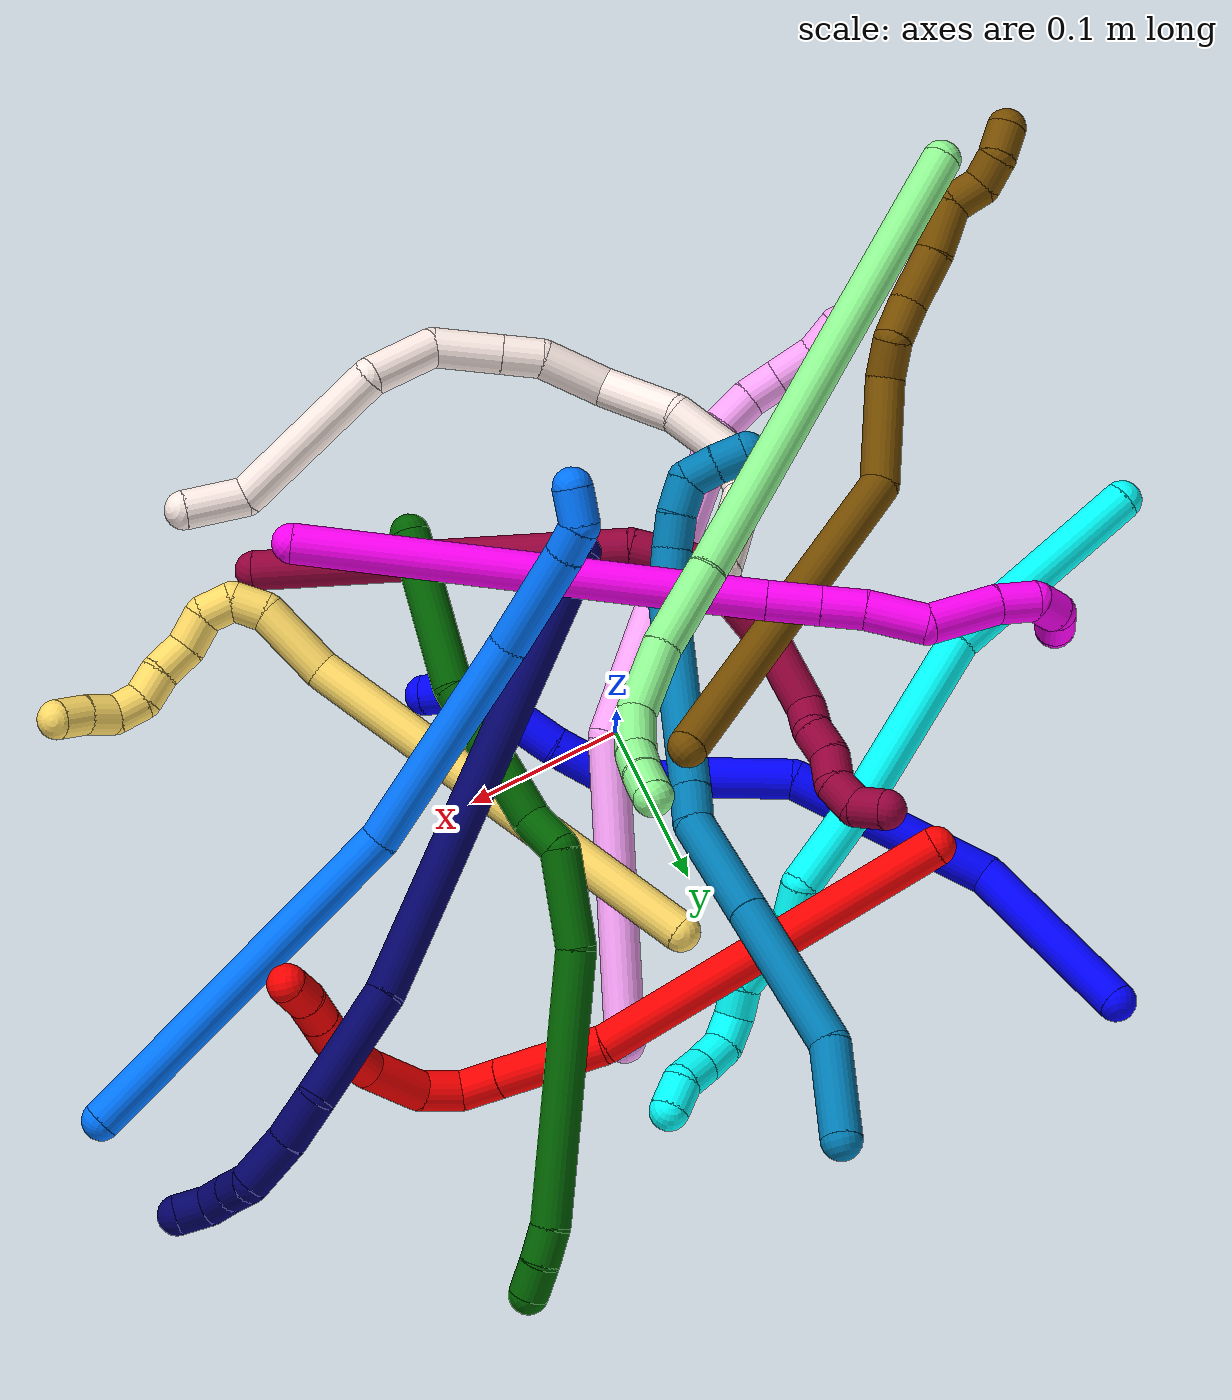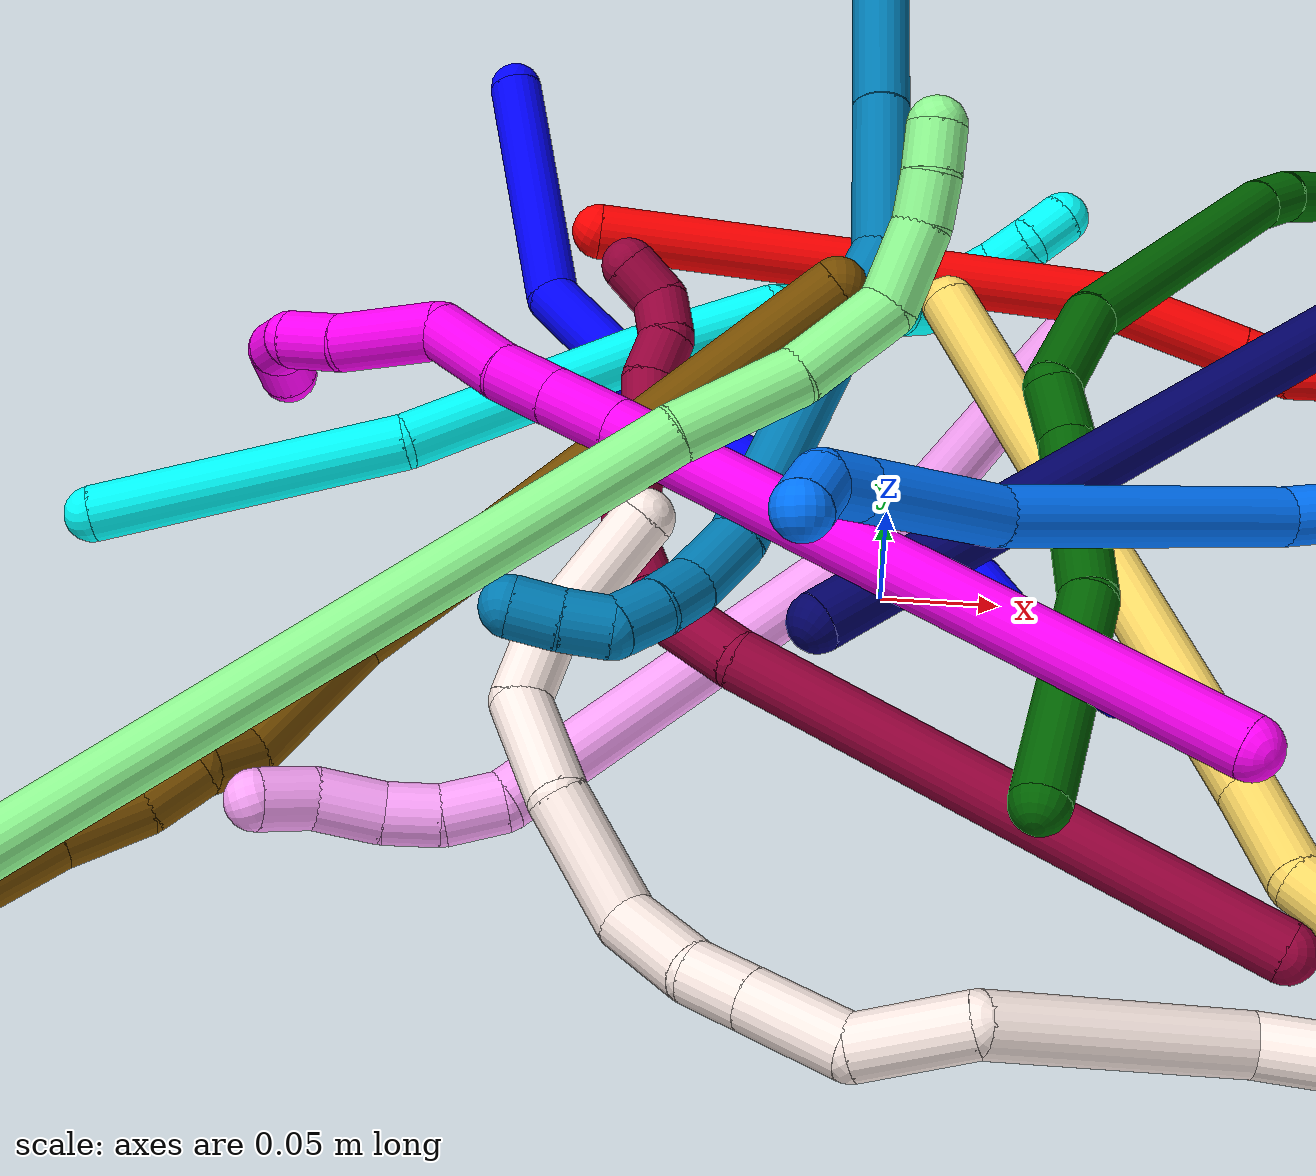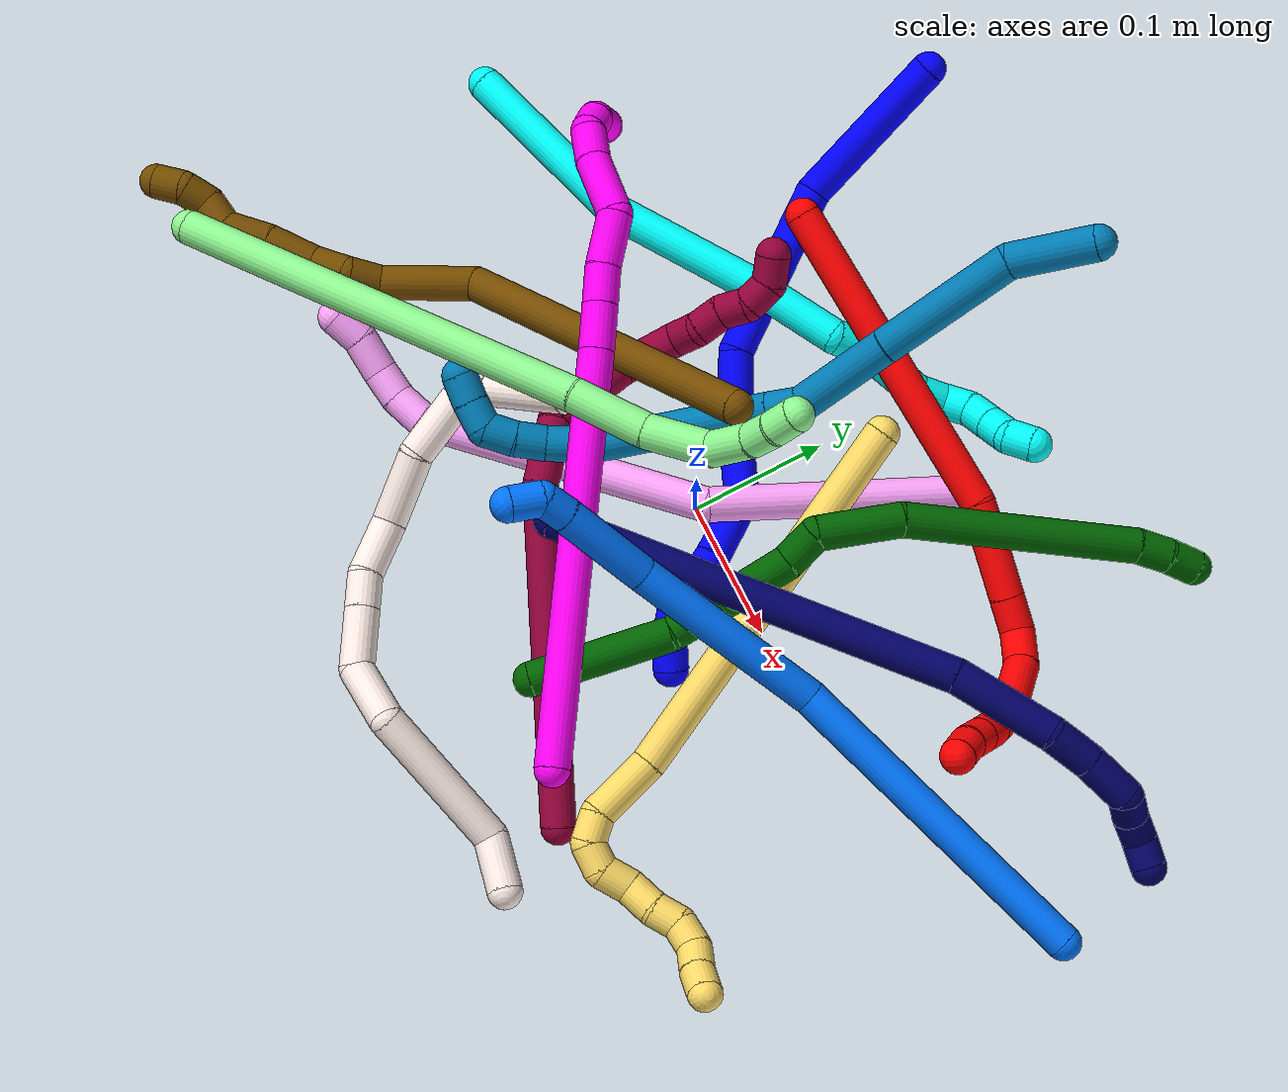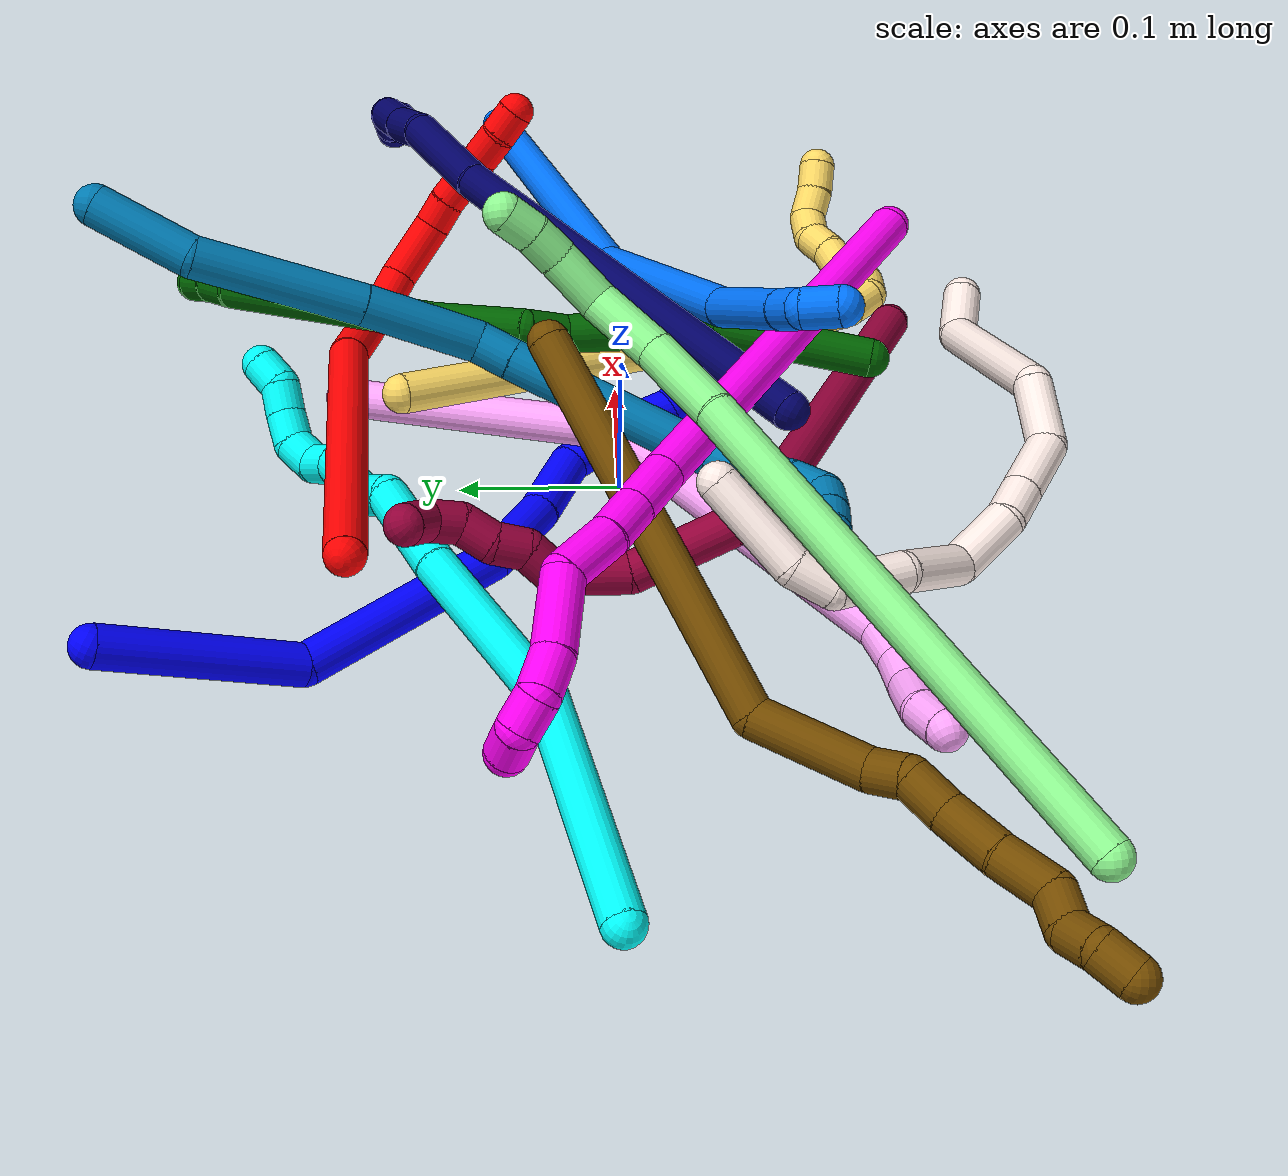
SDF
<sdf version="1.7">
 <world name="default">
  <plugin name="TubeGeneratorPlugin" filename="libtube_generator_plugin.so"/>
  <model name="photoneo_s_sensor">
   <static>1</static>
   <pose>0 0 2 1.57079 1.57079 3.14159</pose>
   <link name="link">
    <inertial><mass>0.1</mass></inertial>
    <sensor name="sensor" type="depth">
     <update_rate>30</update_rate>
     <camera>
      <horizontal_fov>1.22</horizontal_fov>
      <image><width>1920</width><height>1200</height><format>B8G8R8</format></image>
      <clip><near>0.1</near><far>4</far></clip>
      <depth_camera><output>points</output></depth_camera>
     </camera>
     <plugin name="camera_plugin" filename="libgazebo_ros_depth_camera.so">
      <baseline>0.2</baseline>
      <alwaysOn>1</alwaysOn>
      <updateRate>0.0</updateRate>
      <cameraName>camera_ir</cameraName>
      <imageTopicName>/camera/color/image_raw</imageTopicName>
      <cameraInfoTopicName>/camera/color/camera_info</cameraInfoTopicName>
      <depthImageTopicName>/camera/depth/image_raw</depthImageTopicName>
      <depthImageCameraInfoTopicName>/camera/depth/camera_info</depthImageCameraInfoTopicName>
      <pointCloudTopicName>/camera/depth/points</pointCloudTopicName>
      <frameName>fr_optical</frameName>
      <pointCloudCutoff>0.1</pointCloudCutoff>
      <pointCloudCutoffMax>2.0</pointCloudCutoffMax>
      <distortionK1>0</distortionK1>
      <distortionK2>0</distortionK2>
      <distortionK3>0</distortionK3>
      <distortionT1>0</distortionT1>
      <distortionT2>0</distortionT2>
      <CxPrime>0</CxPrime>
      <Cx>0</Cx>
      <Cy>0</Cy>
      <focalLength>0</focalLength>
      <hackBaseline>0</hackBaseline>
     </plugin>
    </sensor>
   </link>
  </model>
  <gravity>0 0 -9.8</gravity>
  <magnetic_field>6e-06 2.3e-05 -4.2e-05</magnetic_field>
  <atmosphere type="adiabatic"/>
  <physics name="default_physics" default="0" type="ode">
   <max_step_size>0.003</max_step_size>
   <real_time_factor>1</real_time_factor>
   <real_time_update_rate>1000</real_time_update_rate>
   <max_contacts>10000</max_contacts>
   <ode>
    <solver>
     <type>quick</type>
     <iters>100</iters>
     <sor>1.3</sor>
     <use_dynamic_moi_rescaling>0</use_dynamic_moi_rescaling>
    </solver>
    <constraints>
     <contact_max_correcting_vel>0</contact_max_correcting_vel>
     <contact_surface_layer>0.001</contact_surface_layer>
     <cfm>0</cfm>
     <erp>0.2</erp>
    </constraints>
   </ode>
  </physics>
  <scene><ambient>0.4 0.4 0.4 1</ambient><background>0.7 0.7 0.7 1</background><shadows>0</shadows></scene>
  <audio><device>default</device></audio>
  <spherical_coordinates>
   <surface_model>EARTH_WGS84</surface_model>
   <latitude_deg>0</latitude_deg>
   <longitude_deg>0</longitude_deg>
   <elevation>0</elevation>
   <heading_deg>0</heading_deg>
  </spherical_coordinates>
  <model name="bin">
   <static>1</static>
   <link name="bottom">
    <collision name="collision-bottom">
     <pose>0 0 -0.01 0 -0 0</pose>
     <geometry><box><size>0.8 0.6 0.02</size></box></geometry>
     <surface>
      <friction><ode><mu>100</mu><mu2>100</mu2></ode></friction>
      <contact><collide_bitmask>65535</collide_bitmask></contact>
     </surface>
    </collision>
   </link>
   <link name="west_wall">
    <collision name="collision-west_wall">
     <pose>-0.41 0 0.1 0 -0 0</pose>
     <geometry><box><size>0.02 0.6 0.2</size></box></geometry>
     <surface>
      <friction><ode><mu>100</mu><mu2>100</mu2></ode></friction>
      <contact><collide_bitmask>65535</collide_bitmask></contact>
     </surface>
    </collision>
   </link>
   <link name="east_wall">
    <collision name="collision-east_wall">
     <pose>0.41 0 0.1 0 -0 0</pose>
     <geometry><box><size>0.02 0.6 0.2</size></box></geometry>
     <surface>
      <friction><ode><mu>100</mu><mu2>100</mu2></ode></friction>
      <contact><collide_bitmask>65535</collide_bitmask></contact>
     </surface>
    </collision>
   </link>
   <link name="south_wall">
    <collision name="collision-south_wall">
     <pose>0 -0.31 0.1 0 -0 0</pose>
     <geometry><box><size>0.8 0.02 0.2</size></box></geometry>
     <surface>
      <friction><ode><mu>100</mu><mu2>100</mu2></ode></friction>
      <contact><collide_bitmask>65535</collide_bitmask></contact>
     </surface>
    </collision>
   </link>
   <link name="north_wall">
    <collision name="collision-north_wall">
     <pose>0 0.31 0.1 0 -0 0</pose>
     <geometry><box><size>0.8 0.02 0.2</size></box></geometry>
     <surface>
      <friction><ode><mu>100</mu><mu2>100</mu2></ode></friction>
      <contact><collide_bitmask>65535</collide_bitmask></contact>
     </surface>
    </collision>
   </link>
  </model>
  <model name="1">
   <static>0</static>
   <link name="1">
    <collision name="collision-cylinder-e_1_1_4">
     <pose>0.019959 -0.017338 -0.05426 2.83232 0.337024 1.65813</pose>
     <geometry><cylinder><radius>0.0125</radius><length>0.120717</length></cylinder></geometry>
     <surface>
      <friction><ode><mu>1.16</mu><mu2>1.16</mu2><slip1>0</slip1><slip2>0</slip2></ode></friction>
      <contact><ode><kp>1e+06</kp><kd>1</kd><max_vel>0</max_vel><min_depth>0.001</min_depth></ode></contact>
     </surface>
    </collision>
    <visual name="visual-cylinder-e_1_1_4">
     <pose>0.019959 -0.017338 -0.05426 2.83232 0.337024 1.65813</pose>
     <geometry><cylinder><radius>0.0125</radius><length>0.120717</length></cylinder></geometry>
     <material><ambient>0 0 1 1</ambient></material>
    </visual>
    <collision name="collision-cylinder-e_2_4_5">
     <pose>0.062798 -0.084125 -0.146135 2.22109 0.352846 0.690405</pose>
     <geometry><cylinder><radius>0.0125</radius><length>0.132418</length></cylinder></geometry>
     <surface>
      <friction><ode><mu>1.16</mu><mu2>1.16</mu2><slip1>0</slip1><slip2>0</slip2></ode></friction>
      <contact><ode><kp>1e+06</kp><kd>1</kd><max_vel>0</max_vel><min_depth>0.001</min_depth></ode></contact>
     </surface>
    </collision>
    <visual name="visual-cylinder-e_2_4_5">
     <pose>0.062798 -0.084125 -0.146135 2.22109 0.352846 0.690405</pose>
     <geometry><cylinder><radius>0.0125</radius><length>0.132418</length></cylinder></geometry>
     <material><ambient>0 0 1 1</ambient></material>
    </visual>
    <collision name="collision-cylinder-e_3_5_6">
     <pose>0.104698 -0.151912 -0.191782 1.98365 0.759797 1.09668</pose>
     <geometry><cylinder><radius>0.0125</radius><length>0.055229</length></cylinder></geometry>
     <surface>
      <friction><ode><mu>1.16</mu><mu2>1.16</mu2><slip1>0</slip1><slip2>0</slip2></ode></friction>
      <contact><ode><kp>1e+06</kp><kd>1</kd><max_vel>0</max_vel><min_depth>0.001</min_depth></ode></contact>
     </surface>
    </collision>
    <visual name="visual-cylinder-e_3_5_6">
     <pose>0.104698 -0.151912 -0.191782 1.98365 0.759797 1.09668</pose>
     <geometry><cylinder><radius>0.0125</radius><length>0.055229</length></cylinder></geometry>
     <material><ambient>0 0 1 1</ambient></material>
    </visual>
    <collision name="collision-cylinder-e_4_6_7">
     <pose>0.141054 -0.188532 -0.204009 1.79633 0.746039 0.913326</pose>
     <geometry><cylinder><radius>0.0125</radius><length>0.051082</length></cylinder></geometry>
     <surface>
      <friction><ode><mu>1.16</mu><mu2>1.16</mu2><slip1>0</slip1><slip2>0</slip2></ode></friction>
      <contact><ode><kp>1e+06</kp><kd>1</kd><max_vel>0</max_vel><min_depth>0.001</min_depth></ode></contact>
     </surface>
    </collision>
    <visual name="visual-cylinder-e_4_6_7">
     <pose>0.141054 -0.188532 -0.204009 1.79633 0.746039 0.913326</pose>
     <geometry><cylinder><radius>0.0125</radius><length>0.051082</length></cylinder></geometry>
     <material><ambient>0 0 1 1</ambient></material>
    </visual>
    <collision name="collision-cylinder-e_5_7_8">
     <pose>0.164236 -0.226201 -0.220756 2.14538 0.247926 0.450449</pose>
     <geometry><cylinder><radius>0.0125</radius><length>0.04765</length></cylinder></geometry>
     <surface>
      <friction><ode><mu>1.16</mu><mu2>1.16</mu2><slip1>0</slip1><slip2>0</slip2></ode></friction>
      <contact><ode><kp>1e+06</kp><kd>1</kd><max_vel>0</max_vel><min_depth>0.001</min_depth></ode></contact>
     </surface>
    </collision>
    <visual name="visual-cylinder-e_5_7_8">
     <pose>0.164236 -0.226201 -0.220756 2.14538 0.247926 0.450449</pose>
     <geometry><cylinder><radius>0.0125</radius><length>0.04765</length></cylinder></geometry>
     <material><ambient>0 0 1 1</ambient></material>
    </visual>
    <collision name="collision-cylinder-e_6_8_9">
     <pose>0.173553 -0.256266 -0.24294 2.30473 0.236818 0.522802</pose>
     <geometry><cylinder><radius>0.0125</radius><length>0.029584</length></cylinder></geometry>
     <surface>
      <friction><ode><mu>1.16</mu><mu2>1.16</mu2><slip1>0</slip1><slip2>0</slip2></ode></friction>
      <contact><ode><kp>1e+06</kp><kd>1</kd><max_vel>0</max_vel><min_depth>0.001</min_depth></ode></contact>
     </surface>
    </collision>
    <visual name="visual-cylinder-e_6_8_9">
     <pose>0.173553 -0.256266 -0.24294 2.30473 0.236818 0.522802</pose>
     <geometry><cylinder><radius>0.0125</radius><length>0.029584</length></cylinder></geometry>
     <material><ambient>0 0 1 1</ambient></material>
    </visual>
    <collision name="collision-cylinder-e_7_9_10">
     <pose>0.176508 -0.276547 -0.256816 1.98696 -0.049046 -0.075279</pose>
     <geometry><cylinder><radius>0.0125</radius><length>0.021025</length></cylinder></geometry>
     <surface>
      <friction><ode><mu>1.16</mu><mu2>1.16</mu2><slip1>0</slip1><slip2>0</slip2></ode></friction>
      <contact><ode><kp>1e+06</kp><kd>1</kd><max_vel>0</max_vel><min_depth>0.001</min_depth></ode></contact>
     </surface>
    </collision>
    <visual name="visual-cylinder-e_7_9_10">
     <pose>0.176508 -0.276547 -0.256816 1.98696 -0.049046 -0.075279</pose>
     <geometry><cylinder><radius>0.0125</radius><length>0.021025</length></cylinder></geometry>
     <material><ambient>0 0 1 1</ambient></material>
    </visual>
    <collision name="collision-cylinder-e_8_10_11">
     <pose>0.181027 -0.295027 -0.264874 1.97657 0.480416 0.711951</pose>
     <geometry><cylinder><radius>0.0125</radius><length>0.021787</length></cylinder></geometry>
     <surface>
      <friction><ode><mu>1.16</mu><mu2>1.16</mu2><slip1>0</slip1><slip2>0</slip2></ode></friction>
      <contact><ode><kp>1e+06</kp><kd>1</kd><max_vel>0</max_vel><min_depth>0.001</min_depth></ode></contact>
     </surface>
    </collision>
    <visual name="visual-cylinder-e_8_10_11">
     <pose>0.181027 -0.295027 -0.264874 1.97657 0.480416 0.711951</pose>
     <geometry><cylinder><radius>0.0125</radius><length>0.021787</length></cylinder></geometry>
     <material><ambient>0 0 1 1</ambient></material>
    </visual>
    <collision name="collision-cylinder-e_9_11_2">
     <pose>0.194608 -0.30855 -0.271928 2.17981 0.985376 1.59932</pose>
     <geometry><cylinder><radius>0.0125</radius><length>0.020508</length></cylinder></geometry>
     <surface>
      <friction><ode><mu>1.16</mu><mu2>1.16</mu2><slip1>0</slip1><slip2>0</slip2></ode></friction>
      <contact><ode><kp>1e+06</kp><kd>1</kd><max_vel>0</max_vel><min_depth>0.001</min_depth></ode></contact>
     </surface>
    </collision>
    <visual name="visual-cylinder-e_9_11_2">
     <pose>0.194608 -0.30855 -0.271928 2.17981 0.985376 1.59932</pose>
     <geometry><cylinder><radius>0.0125</radius><length>0.020508</length></cylinder></geometry>
     <material><ambient>0 0 1 1</ambient></material>
    </visual>
    <collision name="collision-sphere-2">
     <pose>0.203155 -0.313197 -0.275169 0 -0 0</pose>
     <geometry><sphere><radius>0.0125</radius></sphere></geometry>
     <surface>
      <friction><ode><mu>1.16</mu><mu2>1.16</mu2><slip1>0</slip1><slip2>0</slip2></ode></friction>
      <contact><ode><kp>1e+06</kp><kd>1</kd><max_vel>0</max_vel><min_depth>0.001</min_depth></ode></contact>
     </surface>
    </collision>
    <visual name="visual-sphere-2">
     <pose>0.203155 -0.313197 -0.275169 0 -0 0</pose>
     <geometry><sphere><radius>0.0125</radius></sphere></geometry>
     <material><ambient>0 0 1 1</ambient></material>
    </visual>
    <collision name="collision-sphere-11">
     <pose>0.186062 -0.303903 -0.268687 0 -0 0</pose>
     <geometry><sphere><radius>0.0125</radius></sphere></geometry>
     <surface>
      <friction><ode><mu>1.16</mu><mu2>1.16</mu2><slip1>0</slip1><slip2>0</slip2></ode></friction>
      <contact><ode><kp>1e+06</kp><kd>1</kd><max_vel>0</max_vel><min_depth>0.001</min_depth></ode></contact>
     </surface>
    </collision>
    <visual name="visual-sphere-11">
     <pose>0.186062 -0.303903 -0.268687 0 -0 0</pose>
     <geometry><sphere><radius>0.0125</radius></sphere></geometry>
     <material><ambient>0 0 1 1</ambient></material>
    </visual>
    <collision name="collision-sphere-10">
     <pose>0.175993 -0.286151 -0.261061 0 -0 0</pose>
     <geometry><sphere><radius>0.0125</radius></sphere></geometry>
     <surface>
      <friction><ode><mu>1.16</mu><mu2>1.16</mu2><slip1>0</slip1><slip2>0</slip2></ode></friction>
      <contact><ode><kp>1e+06</kp><kd>1</kd><max_vel>0</max_vel><min_depth>0.001</min_depth></ode></contact>
     </surface>
    </collision>
    <visual name="visual-sphere-10">
     <pose>0.175993 -0.286151 -0.261061 0 -0 0</pose>
     <geometry><sphere><radius>0.0125</radius></sphere></geometry>
     <material><ambient>0 0 1 1</ambient></material>
    </visual>
    <collision name="collision-sphere-9">
     <pose>0.177023 -0.266943 -0.252571 0 -0 0</pose>
     <geometry><sphere><radius>0.0125</radius></sphere></geometry>
     <surface>
      <friction><ode><mu>1.16</mu><mu2>1.16</mu2><slip1>0</slip1><slip2>0</slip2></ode></friction>
      <contact><ode><kp>1e+06</kp><kd>1</kd><max_vel>0</max_vel><min_depth>0.001</min_depth></ode></contact>
     </surface>
    </collision>
    <visual name="visual-sphere-9">
     <pose>0.177023 -0.266943 -0.252571 0 -0 0</pose>
     <geometry><sphere><radius>0.0125</radius></sphere></geometry>
     <material><ambient>0 0 1 1</ambient></material>
    </visual>
    <collision name="collision-sphere-4">
     <pose>0.039919 -0.034675 -0.10852 0 -0 0</pose>
     <geometry><sphere><radius>0.0125</radius></sphere></geometry>
     <surface>
      <friction><ode><mu>1.16</mu><mu2>1.16</mu2><slip1>0</slip1><slip2>0</slip2></ode></friction>
      <contact><ode><kp>1e+06</kp><kd>1</kd><max_vel>0</max_vel><min_depth>0.001</min_depth></ode></contact>
     </surface>
    </collision>
    <visual name="visual-sphere-4">
     <pose>0.039919 -0.034675 -0.10852 0 -0 0</pose>
     <geometry><sphere><radius>0.0125</radius></sphere></geometry>
     <material><ambient>0 0 1 1</ambient></material>
    </visual>
    <collision name="collision-sphere-1">
     <geometry><sphere><radius>0.0125</radius></sphere></geometry>
     <surface>
      <friction><ode><mu>1.16</mu><mu2>1.16</mu2><slip1>0</slip1><slip2>0</slip2></ode></friction>
      <contact><ode><kp>1e+06</kp><kd>1</kd><max_vel>0</max_vel><min_depth>0.001</min_depth></ode></contact>
     </surface>
    </collision>
    <visual name="visual-sphere-1">
     <geometry><sphere><radius>0.0125</radius></sphere></geometry>
     <material><ambient>0 0 1 1</ambient></material>
    </visual>
    <collision name="collision-sphere-8">
     <pose>0.170083 -0.245589 -0.233309 0 -0 0</pose>
     <geometry><sphere><radius>0.0125</radius></sphere></geometry>
     <surface>
      <friction><ode><mu>1.16</mu><mu2>1.16</mu2><slip1>0</slip1><slip2>0</slip2></ode></friction>
      <contact><ode><kp>1e+06</kp><kd>1</kd><max_vel>0</max_vel><min_depth>0.001</min_depth></ode></contact>
     </surface>
    </collision>
    <visual name="visual-sphere-8">
     <pose>0.170083 -0.245589 -0.233309 0 -0 0</pose>
     <geometry><sphere><radius>0.0125</radius></sphere></geometry>
     <material><ambient>0 0 1 1</ambient></material>
    </visual>
    <collision name="collision-sphere-5">
     <pose>0.085678 -0.133574 -0.18375 0 -0 0</pose>
     <geometry><sphere><radius>0.0125</radius></sphere></geometry>
     <surface>
      <friction><ode><mu>1.16</mu><mu2>1.16</mu2><slip1>0</slip1><slip2>0</slip2></ode></friction>
      <contact><ode><kp>1e+06</kp><kd>1</kd><max_vel>0</max_vel><min_depth>0.001</min_depth></ode></contact>
     </surface>
    </collision>
    <visual name="visual-sphere-5">
     <pose>0.085678 -0.133574 -0.18375 0 -0 0</pose>
     <geometry><sphere><radius>0.0125</radius></sphere></geometry>
     <material><ambient>0 0 1 1</ambient></material>
    </visual>
    <collision name="collision-sphere-6">
     <pose>0.123718 -0.17025 -0.199815 0 -0 0</pose>
     <geometry><sphere><radius>0.0125</radius></sphere></geometry>
     <surface>
      <friction><ode><mu>1.16</mu><mu2>1.16</mu2><slip1>0</slip1><slip2>0</slip2></ode></friction>
      <contact><ode><kp>1e+06</kp><kd>1</kd><max_vel>0</max_vel><min_depth>0.001</min_depth></ode></contact>
     </surface>
    </collision>
    <visual name="visual-sphere-6">
     <pose>0.123718 -0.17025 -0.199815 0 -0 0</pose>
     <geometry><sphere><radius>0.0125</radius></sphere></geometry>
     <material><ambient>0 0 1 1</ambient></material>
    </visual>
    <collision name="collision-sphere-7">
     <pose>0.15839 -0.206814 -0.208204 0 -0 0</pose>
     <geometry><sphere><radius>0.0125</radius></sphere></geometry>
     <surface>
      <friction><ode><mu>1.16</mu><mu2>1.16</mu2><slip1>0</slip1><slip2>0</slip2></ode></friction>
      <contact><ode><kp>1e+06</kp><kd>1</kd><max_vel>0</max_vel><min_depth>0.001</min_depth></ode></contact>
     </surface>
    </collision>
    <visual name="visual-sphere-7">
     <pose>0.15839 -0.206814 -0.208204 0 -0 0</pose>
     <geometry><sphere><radius>0.0125</radius></sphere></geometry>
     <material><ambient>0 0 1 1</ambient></material>
    </visual>
    <inertial>
     <pose>0.096638 -0.136366 -0.162735 0 -0 0</pose>
     <mass>0.5</mass>
     <inertia><ixx>0.00046</ixx><ixy>0</ixy><ixz>0</ixz><iyy>0.000238</iyy><iyz>0</iyz><izz>6.1e-05</izz></inertia>
    </inertial>
   </link>
   <pose>-0.19469 0.288514 0.060699 -1.00611 0.673209 0.157013</pose>
  </model>
  <model name="2">
   <static>0</static>
   <link name="2">
    <collision name="collision-cylinder-e_1_1_4">
     <pose>0.040226 0.02099 0.108303 -0.19143 0.349651 -0.033913</pose>
     <geometry><cylinder><radius>0.0125</radius><length>0.234846</length></cylinder></geometry>
     <surface>
      <friction><ode><mu>1.16</mu><mu2>1.16</mu2><slip1>0</slip1><slip2>0</slip2></ode></friction>
      <contact><ode><kp>1e+06</kp><kd>1</kd><max_vel>0</max_vel><min_depth>0.001</min_depth></ode></contact>
     </surface>
    </collision>
    <visual name="visual-cylinder-e_1_1_4">
     <pose>0.040226 0.02099 0.108303 -0.19143 0.349651 -0.033913</pose>
     <geometry><cylinder><radius>0.0125</radius><length>0.234846</length></cylinder></geometry>
     <material><ambient>1 0 0 1</ambient></material>
    </visual>
    <collision name="collision-cylinder-e_2_4_5">
     <pose>0.084315 0.044741 0.2509 -0.080357 0.111834 -0.0045</pose>
     <geometry><cylinder><radius>0.0125</radius><length>0.069241</length></cylinder></geometry>
     <surface>
      <friction><ode><mu>1.16</mu><mu2>1.16</mu2><slip1>0</slip1><slip2>0</slip2></ode></friction>
      <contact><ode><kp>1e+06</kp><kd>1</kd><max_vel>0</max_vel><min_depth>0.001</min_depth></ode></contact>
     </surface>
    </collision>
    <visual name="visual-cylinder-e_2_4_5">
     <pose>0.084315 0.044741 0.2509 -0.080357 0.111834 -0.0045</pose>
     <geometry><cylinder><radius>0.0125</radius><length>0.069241</length></cylinder></geometry>
     <material><ambient>1 0 0 1</ambient></material>
    </visual>
    <collision name="collision-cylinder-e_3_5_6">
     <pose>0.08964 0.048334 0.297953 -0.06509 0.113775 -0.003708</pose>
     <geometry><cylinder><radius>0.0125</radius><length>0.025742</length></cylinder></geometry>
     <surface>
      <friction><ode><mu>1.16</mu><mu2>1.16</mu2><slip1>0</slip1><slip2>0</slip2></ode></friction>
      <contact><ode><kp>1e+06</kp><kd>1</kd><max_vel>0</max_vel><min_depth>0.001</min_depth></ode></contact>
     </surface>
    </collision>
    <visual name="visual-cylinder-e_3_5_6">
     <pose>0.08964 0.048334 0.297953 -0.06509 0.113775 -0.003708</pose>
     <geometry><cylinder><radius>0.0125</radius><length>0.025742</length></cylinder></geometry>
     <material><ambient>1 0 0 1</ambient></material>
    </visual>
    <collision name="collision-cylinder-e_4_6_7">
     <pose>0.089208 0.057508 0.321039 -0.679606 -0.14167 0.050156</pose>
     <geometry><cylinder><radius>0.0125</radius><length>0.026816</length></cylinder></geometry>
     <surface>
      <friction><ode><mu>1.16</mu><mu2>1.16</mu2><slip1>0</slip1><slip2>0</slip2></ode></friction>
      <contact><ode><kp>1e+06</kp><kd>1</kd><max_vel>0</max_vel><min_depth>0.001</min_depth></ode></contact>
     </surface>
    </collision>
    <visual name="visual-cylinder-e_4_6_7">
     <pose>0.089208 0.057508 0.321039 -0.679606 -0.14167 0.050156</pose>
     <geometry><cylinder><radius>0.0125</radius><length>0.026816</length></cylinder></geometry>
     <material><ambient>1 0 0 1</ambient></material>
    </visual>
    <collision name="collision-cylinder-e_5_7_8">
     <pose>0.078689 0.083511 0.340055 -1.11343 -0.413029 0.259317</pose>
     <geometry><cylinder><radius>0.0125</radius><length>0.042982</length></cylinder></geometry>
     <surface>
      <friction><ode><mu>1.16</mu><mu2>1.16</mu2><slip1>0</slip1><slip2>0</slip2></ode></friction>
      <contact><ode><kp>1e+06</kp><kd>1</kd><max_vel>0</max_vel><min_depth>0.001</min_depth></ode></contact>
     </surface>
    </collision>
    <visual name="visual-cylinder-e_5_7_8">
     <pose>0.078689 0.083511 0.340055 -1.11343 -0.413029 0.259317</pose>
     <geometry><cylinder><radius>0.0125</radius><length>0.042982</length></cylinder></geometry>
     <material><ambient>1 0 0 1</ambient></material>
    </visual>
    <collision name="collision-cylinder-e_6_8_9">
     <pose>0.065761 0.110147 0.350357 -1.3934 -0.440777 0.37057</pose>
     <geometry><cylinder><radius>0.0125</radius><length>0.020164</length></cylinder></geometry>
     <surface>
      <friction><ode><mu>1.16</mu><mu2>1.16</mu2><slip1>0</slip1><slip2>0</slip2></ode></friction>
      <contact><ode><kp>1e+06</kp><kd>1</kd><max_vel>0</max_vel><min_depth>0.001</min_depth></ode></contact>
     </surface>
    </collision>
    <visual name="visual-cylinder-e_6_8_9">
     <pose>0.065761 0.110147 0.350357 -1.3934 -0.440777 0.37057</pose>
     <geometry><cylinder><radius>0.0125</radius><length>0.020164</length></cylinder></geometry>
     <material><ambient>1 0 0 1</ambient></material>
    </visual>
    <collision name="collision-cylinder-e_7_9_10">
     <pose>0.055994 0.127478 0.353376 -1.40358 -0.572823 0.488009</pose>
     <geometry><cylinder><radius>0.0125</radius><length>0.020167</length></cylinder></geometry>
     <surface>
      <friction><ode><mu>1.16</mu><mu2>1.16</mu2><slip1>0</slip1><slip2>0</slip2></ode></friction>
      <contact><ode><kp>1e+06</kp><kd>1</kd><max_vel>0</max_vel><min_depth>0.001</min_depth></ode></contact>
     </surface>
    </collision>
    <visual name="visual-cylinder-e_7_9_10">
     <pose>0.055994 0.127478 0.353376 -1.40358 -0.572823 0.488009</pose>
     <geometry><cylinder><radius>0.0125</radius><length>0.020167</length></cylinder></geometry>
     <material><ambient>1 0 0 1</ambient></material>
    </visual>
    <collision name="collision-cylinder-e_8_10_11">
     <pose>0.044956 0.144144 0.354418 -1.61514 -0.590266 0.615416</pose>
     <geometry><cylinder><radius>0.0125</radius><length>0.020025</length></cylinder></geometry>
     <surface>
      <friction><ode><mu>1.16</mu><mu2>1.16</mu2><slip1>0</slip1><slip2>0</slip2></ode></friction>
      <contact><ode><kp>1e+06</kp><kd>1</kd><max_vel>0</max_vel><min_depth>0.001</min_depth></ode></contact>
     </surface>
    </collision>
    <visual name="visual-cylinder-e_8_10_11">
     <pose>0.044956 0.144144 0.354418 -1.61514 -0.590266 0.615416</pose>
     <geometry><cylinder><radius>0.0125</radius><length>0.020025</length></cylinder></geometry>
     <material><ambient>1 0 0 1</ambient></material>
    </visual>
    <collision name="collision-cylinder-e_9_11_12">
     <pose>0.033812 0.160754 0.353675 -1.61583 -0.590733 0.616293</pose>
     <geometry><cylinder><radius>0.0125</radius><length>0.020009</length></cylinder></geometry>
     <surface>
      <friction><ode><mu>1.16</mu><mu2>1.16</mu2><slip1>0</slip1><slip2>0</slip2></ode></friction>
      <contact><ode><kp>1e+06</kp><kd>1</kd><max_vel>0</max_vel><min_depth>0.001</min_depth></ode></contact>
     </surface>
    </collision>
    <visual name="visual-cylinder-e_9_11_12">
     <pose>0.033812 0.160754 0.353675 -1.61583 -0.590733 0.616293</pose>
     <geometry><cylinder><radius>0.0125</radius><length>0.020009</length></cylinder></geometry>
     <material><ambient>1 0 0 1</ambient></material>
    </visual>
    <collision name="collision-cylinder-e_10_12_2">
     <pose>0.023206 0.177564 0.354831 -1.39288 -0.527218 0.443939</pose>
     <geometry><cylinder><radius>0.0125</radius><length>0.020008</length></cylinder></geometry>
     <surface>
      <friction><ode><mu>1.16</mu><mu2>1.16</mu2><slip1>0</slip1><slip2>0</slip2></ode></friction>
      <contact><ode><kp>1e+06</kp><kd>1</kd><max_vel>0</max_vel><min_depth>0.001</min_depth></ode></contact>
     </surface>
    </collision>
    <visual name="visual-cylinder-e_10_12_2">
     <pose>0.023206 0.177564 0.354831 -1.39288 -0.527218 0.443939</pose>
     <geometry><cylinder><radius>0.0125</radius><length>0.020008</length></cylinder></geometry>
     <material><ambient>1 0 0 1</ambient></material>
    </visual>
    <collision name="collision-sphere-2">
     <pose>0.018173 0.186073 0.356361 0 -0 0</pose>
     <geometry><sphere><radius>0.0125</radius></sphere></geometry>
     <surface>
      <friction><ode><mu>1.16</mu><mu2>1.16</mu2><slip1>0</slip1><slip2>0</slip2></ode></friction>
      <contact><ode><kp>1e+06</kp><kd>1</kd><max_vel>0</max_vel><min_depth>0.001</min_depth></ode></contact>
     </surface>
    </collision>
    <visual name="visual-sphere-2">
     <pose>0.018173 0.186073 0.356361 0 -0 0</pose>
     <geometry><sphere><radius>0.0125</radius></sphere></geometry>
     <material><ambient>1 0 0 1</ambient></material>
    </visual>
    <collision name="collision-sphere-12">
     <pose>0.028239 0.169055 0.353301 0 -0 0</pose>
     <geometry><sphere><radius>0.0125</radius></sphere></geometry>
     <surface>
      <friction><ode><mu>1.16</mu><mu2>1.16</mu2><slip1>0</slip1><slip2>0</slip2></ode></friction>
      <contact><ode><kp>1e+06</kp><kd>1</kd><max_vel>0</max_vel><min_depth>0.001</min_depth></ode></contact>
     </surface>
    </collision>
    <visual name="visual-sphere-12">
     <pose>0.028239 0.169055 0.353301 0 -0 0</pose>
     <geometry><sphere><radius>0.0125</radius></sphere></geometry>
     <material><ambient>1 0 0 1</ambient></material>
    </visual>
    <collision name="collision-sphere-11">
     <pose>0.039384 0.152454 0.354049 0 -0 0</pose>
     <geometry><sphere><radius>0.0125</radius></sphere></geometry>
     <surface>
      <friction><ode><mu>1.16</mu><mu2>1.16</mu2><slip1>0</slip1><slip2>0</slip2></ode></friction>
      <contact><ode><kp>1e+06</kp><kd>1</kd><max_vel>0</max_vel><min_depth>0.001</min_depth></ode></contact>
     </surface>
    </collision>
    <visual name="visual-sphere-11">
     <pose>0.039384 0.152454 0.354049 0 -0 0</pose>
     <geometry><sphere><radius>0.0125</radius></sphere></geometry>
     <material><ambient>1 0 0 1</ambient></material>
    </visual>
    <collision name="collision-sphere-10">
     <pose>0.050529 0.135834 0.354786 0 -0 0</pose>
     <geometry><sphere><radius>0.0125</radius></sphere></geometry>
     <surface>
      <friction><ode><mu>1.16</mu><mu2>1.16</mu2><slip1>0</slip1><slip2>0</slip2></ode></friction>
      <contact><ode><kp>1e+06</kp><kd>1</kd><max_vel>0</max_vel><min_depth>0.001</min_depth></ode></contact>
     </surface>
    </collision>
    <visual name="visual-sphere-10">
     <pose>0.050529 0.135834 0.354786 0 -0 0</pose>
     <geometry><sphere><radius>0.0125</radius></sphere></geometry>
     <material><ambient>1 0 0 1</ambient></material>
    </visual>
    <collision name="collision-sphere-9">
     <pose>0.06146 0.119122 0.351966 0 -0 0</pose>
     <geometry><sphere><radius>0.0125</radius></sphere></geometry>
     <surface>
      <friction><ode><mu>1.16</mu><mu2>1.16</mu2><slip1>0</slip1><slip2>0</slip2></ode></friction>
      <contact><ode><kp>1e+06</kp><kd>1</kd><max_vel>0</max_vel><min_depth>0.001</min_depth></ode></contact>
     </surface>
    </collision>
    <visual name="visual-sphere-9">
     <pose>0.06146 0.119122 0.351966 0 -0 0</pose>
     <geometry><sphere><radius>0.0125</radius></sphere></geometry>
     <material><ambient>1 0 0 1</ambient></material>
    </visual>
    <collision name="collision-sphere-4">
     <pose>0.080451 0.041979 0.216606 0 -0 0</pose>
     <geometry><sphere><radius>0.0125</radius></sphere></geometry>
     <surface>
      <friction><ode><mu>1.16</mu><mu2>1.16</mu2><slip1>0</slip1><slip2>0</slip2></ode></friction>
      <contact><ode><kp>1e+06</kp><kd>1</kd><max_vel>0</max_vel><min_depth>0.001</min_depth></ode></contact>
     </surface>
    </collision>
    <visual name="visual-sphere-4">
     <pose>0.080451 0.041979 0.216606 0 -0 0</pose>
     <geometry><sphere><radius>0.0125</radius></sphere></geometry>
     <material><ambient>1 0 0 1</ambient></material>
    </visual>
    <collision name="collision-sphere-1">
     <geometry><sphere><radius>0.0125</radius></sphere></geometry>
     <surface>
      <friction><ode><mu>1.16</mu><mu2>1.16</mu2><slip1>0</slip1><slip2>0</slip2></ode></friction>
      <contact><ode><kp>1e+06</kp><kd>1</kd><max_vel>0</max_vel><min_depth>0.001</min_depth></ode></contact>
     </surface>
    </collision>
    <visual name="visual-sphere-1">
     <geometry><sphere><radius>0.0125</radius></sphere></geometry>
     <material><ambient>1 0 0 1</ambient></material>
    </visual>
    <collision name="collision-sphere-8">
     <pose>0.070063 0.101172 0.348747 0 -0 0</pose>
     <geometry><sphere><radius>0.0125</radius></sphere></geometry>
     <surface>
      <friction><ode><mu>1.16</mu><mu2>1.16</mu2><slip1>0</slip1><slip2>0</slip2></ode></friction>
      <contact><ode><kp>1e+06</kp><kd>1</kd><max_vel>0</max_vel><min_depth>0.001</min_depth></ode></contact>
     </surface>
    </collision>
    <visual name="visual-sphere-8">
     <pose>0.070063 0.101172 0.348747 0 -0 0</pose>
     <geometry><sphere><radius>0.0125</radius></sphere></geometry>
     <material><ambient>1 0 0 1</ambient></material>
    </visual>
    <collision name="collision-sphere-5">
     <pose>0.088179 0.047502 0.285193 0 -0 0</pose>
     <geometry><sphere><radius>0.0125</radius></sphere></geometry>
     <surface>
      <friction><ode><mu>1.16</mu><mu2>1.16</mu2><slip1>0</slip1><slip2>0</slip2></ode></friction>
      <contact><ode><kp>1e+06</kp><kd>1</kd><max_vel>0</max_vel><min_depth>0.001</min_depth></ode></contact>
     </surface>
    </collision>
    <visual name="visual-sphere-5">
     <pose>0.088179 0.047502 0.285193 0 -0 0</pose>
     <geometry><sphere><radius>0.0125</radius></sphere></geometry>
     <material><ambient>1 0 0 1</ambient></material>
    </visual>
    <collision name="collision-sphere-6">
     <pose>0.091101 0.049166 0.310714 0 -0 0</pose>
     <geometry><sphere><radius>0.0125</radius></sphere></geometry>
     <surface>
      <friction><ode><mu>1.16</mu><mu2>1.16</mu2><slip1>0</slip1><slip2>0</slip2></ode></friction>
      <contact><ode><kp>1e+06</kp><kd>1</kd><max_vel>0</max_vel><min_depth>0.001</min_depth></ode></contact>
     </surface>
    </collision>
    <visual name="visual-sphere-6">
     <pose>0.091101 0.049166 0.310714 0 -0 0</pose>
     <geometry><sphere><radius>0.0125</radius></sphere></geometry>
     <material><ambient>1 0 0 1</ambient></material>
    </visual>
    <collision name="collision-sphere-7">
     <pose>0.087315 0.065851 0.331363 0 -0 0</pose>
     <geometry><sphere><radius>0.0125</radius></sphere></geometry>
     <surface>
      <friction><ode><mu>1.16</mu><mu2>1.16</mu2><slip1>0</slip1><slip2>0</slip2></ode></friction>
      <contact><ode><kp>1e+06</kp><kd>1</kd><max_vel>0</max_vel><min_depth>0.001</min_depth></ode></contact>
     </surface>
    </collision>
    <visual name="visual-sphere-7">
     <pose>0.087315 0.065851 0.331363 0 -0 0</pose>
     <geometry><sphere><radius>0.0125</radius></sphere></geometry>
     <material><ambient>1 0 0 1</ambient></material>
    </visual>
    <inertial>
     <pose>0.055726 0.057701 0.218333 0 -0 0</pose>
     <mass>0.5</mass>
     <inertia>
      <ixx>0.001042</ixx>
      <ixy>0</ixy>
      <ixz>0</ixz>
      <iyy>0.001097</iyy>
      <iyz>0</iyz>
      <izz>-0.000553</izz>
     </inertia>
    </inertial>
   </link>
   <pose>-0.137973 0.156753 0.071999 1.91797 0.007775 1.28893</pose>
  </model>
  <model name="3">
   <static>0</static>
   <link name="3">
    <collision name="collision-cylinder-e_1_1_4">
     <pose>0.066704 0.017719 -0.013034 -2.20501 1.25226 -1.92094</pose>
     <geometry><cylinder><radius>0.0125</radius><length>0.140475</length></cylinder></geometry>
     <surface>
      <friction><ode><mu>1.16</mu><mu2>1.16</mu2><slip1>0</slip1><slip2>0</slip2></ode></friction>
      <contact><ode><kp>1e+06</kp><kd>1</kd><max_vel>0</max_vel><min_depth>0.001</min_depth></ode></contact>
     </surface>
    </collision>
    <visual name="visual-cylinder-e_1_1_4">
     <pose>0.066704 0.017719 -0.013034 -2.20501 1.25226 -1.92094</pose>
     <geometry><cylinder><radius>0.0125</radius><length>0.140475</length></cylinder></geometry>
     <material><ambient>0.003922 1 0.996078 1</ambient></material>
    </visual>
    <collision name="collision-cylinder-e_2_4_5">
     <pose>0.181167 0.065211 -0.042845 -2.08395 0.949702 -1.44305</pose>
     <geometry><cylinder><radius>0.0125</radius><length>0.117453</length></cylinder></geometry>
     <surface>
      <friction><ode><mu>1.16</mu><mu2>1.16</mu2><slip1>0</slip1><slip2>0</slip2></ode></friction>
      <contact><ode><kp>1e+06</kp><kd>1</kd><max_vel>0</max_vel><min_depth>0.001</min_depth></ode></contact>
     </surface>
    </collision>
    <visual name="visual-cylinder-e_2_4_5">
     <pose>0.181167 0.065211 -0.042845 -2.08395 0.949702 -1.44305</pose>
     <geometry><cylinder><radius>0.0125</radius><length>0.117453</length></cylinder></geometry>
     <material><ambient>0.003922 1 0.996078 1</ambient></material>
    </visual>
    <collision name="collision-cylinder-e_3_5_6">
     <pose>0.256368 0.109083 -0.068868 -2.15119 1.01984 -1.60566</pose>
     <geometry><cylinder><radius>0.0125</radius><length>0.064416</length></cylinder></geometry>
     <surface>
      <friction><ode><mu>1.16</mu><mu2>1.16</mu2><slip1>0</slip1><slip2>0</slip2></ode></friction>
      <contact><ode><kp>1e+06</kp><kd>1</kd><max_vel>0</max_vel><min_depth>0.001</min_depth></ode></contact>
     </surface>
    </collision>
    <visual name="visual-cylinder-e_3_5_6">
     <pose>0.256368 0.109083 -0.068868 -2.15119 1.01984 -1.60566</pose>
     <geometry><cylinder><radius>0.0125</radius><length>0.064416</length></cylinder></geometry>
     <material><ambient>0.003922 1 0.996078 1</ambient></material>
    </visual>
    <collision name="collision-cylinder-e_4_6_7">
     <pose>0.288375 0.129516 -0.086619 -2.5016 0.406531 -1.11284</pose>
     <geometry><cylinder><radius>0.0125</radius><length>0.02309</length></cylinder></geometry>
     <surface>
      <friction><ode><mu>1.16</mu><mu2>1.16</mu2><slip1>0</slip1><slip2>0</slip2></ode></friction>
      <contact><ode><kp>1e+06</kp><kd>1</kd><max_vel>0</max_vel><min_depth>0.001</min_depth></ode></contact>
     </surface>
    </collision>
    <visual name="visual-cylinder-e_4_6_7">
     <pose>0.288375 0.129516 -0.086619 -2.5016 0.406531 -1.11284</pose>
     <geometry><cylinder><radius>0.0125</radius><length>0.02309</length></cylinder></geometry>
     <material><ambient>0.003922 1 0.996078 1</ambient></material>
    </visual>
    <collision name="collision-cylinder-e_5_7_8">
     <pose>0.312362 0.143984 -0.109436 -2.62473 0.867688 -2.10457</pose>
     <geometry><cylinder><radius>0.0125</radius><length>0.05092</length></cylinder></geometry>
     <surface>
      <friction><ode><mu>1.16</mu><mu2>1.16</mu2><slip1>0</slip1><slip2>0</slip2></ode></friction>
      <contact><ode><kp>1e+06</kp><kd>1</kd><max_vel>0</max_vel><min_depth>0.001</min_depth></ode></contact>
     </surface>
    </collision>
    <visual name="visual-cylinder-e_5_7_8">
     <pose>0.312362 0.143984 -0.109436 -2.62473 0.867688 -2.10457</pose>
     <geometry><cylinder><radius>0.0125</radius><length>0.05092</length></cylinder></geometry>
     <material><ambient>0.003922 1 0.996078 1</ambient></material>
    </visual>
    <collision name="collision-cylinder-e_6_8_9">
     <pose>0.336128 0.158191 -0.13156 -2.48084 0.413672 -1.09819</pose>
     <geometry><cylinder><radius>0.0125</radius><length>0.021613</length></cylinder></geometry>
     <surface>
      <friction><ode><mu>1.16</mu><mu2>1.16</mu2><slip1>0</slip1><slip2>0</slip2></ode></friction>
      <contact><ode><kp>1e+06</kp><kd>1</kd><max_vel>0</max_vel><min_depth>0.001</min_depth></ode></contact>
     </surface>
    </collision>
    <visual name="visual-cylinder-e_6_8_9">
     <pose>0.336128 0.158191 -0.13156 -2.48084 0.413672 -1.09819</pose>
     <geometry><cylinder><radius>0.0125</radius><length>0.021613</length></cylinder></geometry>
     <material><ambient>0.003922 1 0.996078 1</ambient></material>
    </visual>
    <collision name="collision-cylinder-e_7_9_10">
     <pose>0.348028 0.171157 -0.141327 -1.84702 0.811951 -1.03408</pose>
     <geometry><cylinder><radius>0.0125</radius><length>0.020825</length></cylinder></geometry>
     <surface>
      <friction><ode><mu>1.16</mu><mu2>1.16</mu2><slip1>0</slip1><slip2>0</slip2></ode></friction>
      <contact><ode><kp>1e+06</kp><kd>1</kd><max_vel>0</max_vel><min_depth>0.001</min_depth></ode></contact>
     </surface>
    </collision>
    <visual name="visual-cylinder-e_7_9_10">
     <pose>0.348028 0.171157 -0.141327 -1.84702 0.811951 -1.03408</pose>
     <geometry><cylinder><radius>0.0125</radius><length>0.020825</length></cylinder></geometry>
     <material><ambient>0.003922 1 0.996078 1</ambient></material>
    </visual>
    <collision name="collision-cylinder-e_8_10_11">
     <pose>0.365252 0.181492 -0.141784 -1.16061 1.20054 -0.84368</pose>
     <geometry><cylinder><radius>0.0125</radius><length>0.020743</length></cylinder></geometry>
     <surface>
      <friction><ode><mu>1.16</mu><mu2>1.16</mu2><slip1>0</slip1><slip2>0</slip2></ode></friction>
      <contact><ode><kp>1e+06</kp><kd>1</kd><max_vel>0</max_vel><min_depth>0.001</min_depth></ode></contact>
     </surface>
    </collision>
    <visual name="visual-cylinder-e_8_10_11">
     <pose>0.365252 0.181492 -0.141784 -1.16061 1.20054 -0.84368</pose>
     <geometry><cylinder><radius>0.0125</radius><length>0.020743</length></cylinder></geometry>
     <material><ambient>0.003922 1 0.996078 1</ambient></material>
    </visual>
    <collision name="collision-cylinder-e_9_11_12">
     <pose>0.383976 0.187902 -0.137193 -0.764596 1.12858 -0.498409</pose>
     <geometry><cylinder><radius>0.0125</radius><length>0.020037</length></cylinder></geometry>
     <surface>
      <friction><ode><mu>1.16</mu><mu2>1.16</mu2><slip1>0</slip1><slip2>0</slip2></ode></friction>
      <contact><ode><kp>1e+06</kp><kd>1</kd><max_vel>0</max_vel><min_depth>0.001</min_depth></ode></contact>
     </surface>
    </collision>
    <visual name="visual-cylinder-e_9_11_12">
     <pose>0.383976 0.187902 -0.137193 -0.764596 1.12858 -0.498409</pose>
     <geometry><cylinder><radius>0.0125</radius><length>0.020037</length></cylinder></geometry>
     <material><ambient>0.003922 1 0.996078 1</ambient></material>
    </visual>
    <collision name="collision-cylinder-e_10_12_2">
     <pose>0.400868 0.197378 -0.134841 -1.68419 0.874564 -0.96489</pose>
     <geometry><cylinder><radius>0.0125</radius><length>0.020427</length></cylinder></geometry>
     <surface>
      <friction><ode><mu>1.16</mu><mu2>1.16</mu2><slip1>0</slip1><slip2>0</slip2></ode></friction>
      <contact><ode><kp>1e+06</kp><kd>1</kd><max_vel>0</max_vel><min_depth>0.001</min_depth></ode></contact>
     </surface>
    </collision>
    <visual name="visual-cylinder-e_10_12_2">
     <pose>0.400868 0.197378 -0.134841 -1.68419 0.874564 -0.96489</pose>
     <geometry><cylinder><radius>0.0125</radius><length>0.020427</length></cylinder></geometry>
     <material><ambient>0.003922 1 0.996078 1</ambient></material>
    </visual>
    <collision name="collision-sphere-2">
     <pose>0.408704 0.203886 -0.135582 0 -0 0</pose>
     <geometry><sphere><radius>0.0125</radius></sphere></geometry>
     <surface>
      <friction><ode><mu>1.16</mu><mu2>1.16</mu2><slip1>0</slip1><slip2>0</slip2></ode></friction>
      <contact><ode><kp>1e+06</kp><kd>1</kd><max_vel>0</max_vel><min_depth>0.001</min_depth></ode></contact>
     </surface>
    </collision>
    <visual name="visual-sphere-2">
     <pose>0.408704 0.203886 -0.135582 0 -0 0</pose>
     <geometry><sphere><radius>0.0125</radius></sphere></geometry>
     <material><ambient>0.003922 1 0.996078 1</ambient></material>
    </visual>
    <collision name="collision-sphere-12">
     <pose>0.393031 0.190869 -0.134099 0 -0 0</pose>
     <geometry><sphere><radius>0.0125</radius></sphere></geometry>
     <surface>
      <friction><ode><mu>1.16</mu><mu2>1.16</mu2><slip1>0</slip1><slip2>0</slip2></ode></friction>
      <contact><ode><kp>1e+06</kp><kd>1</kd><max_vel>0</max_vel><min_depth>0.001</min_depth></ode></contact>
     </surface>
    </collision>
    <visual name="visual-sphere-12">
     <pose>0.393031 0.190869 -0.134099 0 -0 0</pose>
     <geometry><sphere><radius>0.0125</radius></sphere></geometry>
     <material><ambient>0.003922 1 0.996078 1</ambient></material>
    </visual>
    <collision name="collision-sphere-11">
     <pose>0.374921 0.184934 -0.140287 0 -0 0</pose>
     <geometry><sphere><radius>0.0125</radius></sphere></geometry>
     <surface>
      <friction><ode><mu>1.16</mu><mu2>1.16</mu2><slip1>0</slip1><slip2>0</slip2></ode></friction>
      <contact><ode><kp>1e+06</kp><kd>1</kd><max_vel>0</max_vel><min_depth>0.001</min_depth></ode></contact>
     </surface>
    </collision>
    <visual name="visual-sphere-11">
     <pose>0.374921 0.184934 -0.140287 0 -0 0</pose>
     <geometry><sphere><radius>0.0125</radius></sphere></geometry>
     <material><ambient>0.003922 1 0.996078 1</ambient></material>
    </visual>
    <collision name="collision-sphere-10">
     <pose>0.355584 0.17805 -0.143281 0 -0 0</pose>
     <geometry><sphere><radius>0.0125</radius></sphere></geometry>
     <surface>
      <friction><ode><mu>1.16</mu><mu2>1.16</mu2><slip1>0</slip1><slip2>0</slip2></ode></friction>
      <contact><ode><kp>1e+06</kp><kd>1</kd><max_vel>0</max_vel><min_depth>0.001</min_depth></ode></contact>
     </surface>
    </collision>
    <visual name="visual-sphere-10">
     <pose>0.355584 0.17805 -0.143281 0 -0 0</pose>
     <geometry><sphere><radius>0.0125</radius></sphere></geometry>
     <material><ambient>0.003922 1 0.996078 1</ambient></material>
    </visual>
    <collision name="collision-sphere-9">
     <pose>0.340472 0.164264 -0.139373 0 -0 0</pose>
     <geometry><sphere><radius>0.0125</radius></sphere></geometry>
     <surface>
      <friction><ode><mu>1.16</mu><mu2>1.16</mu2><slip1>0</slip1><slip2>0</slip2></ode></friction>
      <contact><ode><kp>1e+06</kp><kd>1</kd><max_vel>0</max_vel><min_depth>0.001</min_depth></ode></contact>
     </surface>
    </collision>
    <visual name="visual-sphere-9">
     <pose>0.340472 0.164264 -0.139373 0 -0 0</pose>
     <geometry><sphere><radius>0.0125</radius></sphere></geometry>
     <material><ambient>0.003922 1 0.996078 1</ambient></material>
    </visual>
    <collision name="collision-sphere-4">
     <pose>0.133408 0.035438 -0.026068 0 -0 0</pose>
     <geometry><sphere><radius>0.0125</radius></sphere></geometry>
     <surface>
      <friction><ode><mu>1.16</mu><mu2>1.16</mu2><slip1>0</slip1><slip2>0</slip2></ode></friction>
      <contact><ode><kp>1e+06</kp><kd>1</kd><max_vel>0</max_vel><min_depth>0.001</min_depth></ode></contact>
     </surface>
    </collision>
    <visual name="visual-sphere-4">
     <pose>0.133408 0.035438 -0.026068 0 -0 0</pose>
     <geometry><sphere><radius>0.0125</radius></sphere></geometry>
     <material><ambient>0.003922 1 0.996078 1</ambient></material>
    </visual>
    <collision name="collision-sphere-1">
     <geometry><sphere><radius>0.0125</radius></sphere></geometry>
     <surface>
      <friction><ode><mu>1.16</mu><mu2>1.16</mu2><slip1>0</slip1><slip2>0</slip2></ode></friction>
      <contact><ode><kp>1e+06</kp><kd>1</kd><max_vel>0</max_vel><min_depth>0.001</min_depth></ode></contact>
     </surface>
    </collision>
    <visual name="visual-sphere-1">
     <geometry><sphere><radius>0.0125</radius></sphere></geometry>
     <material><ambient>0.003922 1 0.996078 1</ambient></material>
    </visual>
    <collision name="collision-sphere-8">
     <pose>0.331784 0.152119 -0.123748 0 -0 0</pose>
     <geometry><sphere><radius>0.0125</radius></sphere></geometry>
     <surface>
      <friction><ode><mu>1.16</mu><mu2>1.16</mu2><slip1>0</slip1><slip2>0</slip2></ode></friction>
      <contact><ode><kp>1e+06</kp><kd>1</kd><max_vel>0</max_vel><min_depth>0.001</min_depth></ode></contact>
     </surface>
    </collision>
    <visual name="visual-sphere-8">
     <pose>0.331784 0.152119 -0.123748 0 -0 0</pose>
     <geometry><sphere><radius>0.0125</radius></sphere></geometry>
     <material><ambient>0.003922 1 0.996078 1</ambient></material>
    </visual>
    <collision name="collision-sphere-5">
     <pose>0.228926 0.094983 -0.059622 0 -0 0</pose>
     <geometry><sphere><radius>0.0125</radius></sphere></geometry>
     <surface>
      <friction><ode><mu>1.16</mu><mu2>1.16</mu2><slip1>0</slip1><slip2>0</slip2></ode></friction>
      <contact><ode><kp>1e+06</kp><kd>1</kd><max_vel>0</max_vel><min_depth>0.001</min_depth></ode></contact>
     </surface>
    </collision>
    <visual name="visual-sphere-5">
     <pose>0.228926 0.094983 -0.059622 0 -0 0</pose>
     <geometry><sphere><radius>0.0125</radius></sphere></geometry>
     <material><ambient>0.003922 1 0.996078 1</ambient></material>
    </visual>
    <collision name="collision-sphere-6">
     <pose>0.28381 0.123183 -0.078114 0 -0 0</pose>
     <geometry><sphere><radius>0.0125</radius></sphere></geometry>
     <surface>
      <friction><ode><mu>1.16</mu><mu2>1.16</mu2><slip1>0</slip1><slip2>0</slip2></ode></friction>
      <contact><ode><kp>1e+06</kp><kd>1</kd><max_vel>0</max_vel><min_depth>0.001</min_depth></ode></contact>
     </surface>
    </collision>
    <visual name="visual-sphere-6">
     <pose>0.28381 0.123183 -0.078114 0 -0 0</pose>
     <geometry><sphere><radius>0.0125</radius></sphere></geometry>
     <material><ambient>0.003922 1 0.996078 1</ambient></material>
    </visual>
    <collision name="collision-sphere-7">
     <pose>0.292941 0.135849 -0.095125 0 -0 0</pose>
     <geometry><sphere><radius>0.0125</radius></sphere></geometry>
     <surface>
      <friction><ode><mu>1.16</mu><mu2>1.16</mu2><slip1>0</slip1><slip2>0</slip2></ode></friction>
      <contact><ode><kp>1e+06</kp><kd>1</kd><max_vel>0</max_vel><min_depth>0.001</min_depth></ode></contact>
     </surface>
    </collision>
    <visual name="visual-sphere-7">
     <pose>0.292941 0.135849 -0.095125 0 -0 0</pose>
     <geometry><sphere><radius>0.0125</radius></sphere></geometry>
     <material><ambient>0.003922 1 0.996078 1</ambient></material>
    </visual>
    <inertial>
     <pose>0.215397 0.092084 -0.066206 0 -0 0</pose>
     <mass>0.5</mass>
     <inertia>
      <ixx>-0.00016</ixx>
      <ixy>0</ixy>
      <ixz>0</ixz>
      <iyy>0.000179</iyy>
      <iyz>0</iyz>
      <izz>-0.000537</izz>
     </inertia>
    </inertial>
   </link>
   <pose>-0.346381 0.009985 0.012336 0.217265 -0.287261 -0.02693</pose>
  </model>
  <model name="4">
   <static>0</static>
   <link name="4">
    <collision name="collision-cylinder-e_1_1_4">
     <pose>-0.060823 -0.049497 0.052245 0.758395 -0.701659 -0.289623</pose>
     <geometry><cylinder><radius>0.0125</radius><length>0.188457</length></cylinder></geometry>
     <surface>
      <friction><ode><mu>1.16</mu><mu2>1.16</mu2><slip1>0</slip1><slip2>0</slip2></ode></friction>
      <contact><ode><kp>1e+06</kp><kd>1</kd><max_vel>0</max_vel><min_depth>0.001</min_depth></ode></contact>
     </surface>
    </collision>
    <visual name="visual-cylinder-e_1_1_4">
     <pose>-0.060823 -0.049497 0.052245 0.758395 -0.701659 -0.289623</pose>
     <geometry><cylinder><radius>0.0125</radius><length>0.188457</length></cylinder></geometry>
     <material><ambient>1 0.65098 0.996078 1</ambient></material>
    </visual>
    <collision name="collision-cylinder-e_2_4_5">
     <pose>-0.165466 -0.126426 0.197555 0.286635 -0.424216 -0.062132</pose>
     <geometry><cylinder><radius>0.0125</radius><length>0.212918</length></cylinder></geometry>
     <surface>
      <friction><ode><mu>1.16</mu><mu2>1.16</mu2><slip1>0</slip1><slip2>0</slip2></ode></friction>
      <contact><ode><kp>1e+06</kp><kd>1</kd><max_vel>0</max_vel><min_depth>0.001</min_depth></ode></contact>
     </surface>
    </collision>
    <visual name="visual-cylinder-e_2_4_5">
     <pose>-0.165466 -0.126426 0.197555 0.286635 -0.424216 -0.062132</pose>
     <geometry><cylinder><radius>0.0125</radius><length>0.212918</length></cylinder></geometry>
     <material><ambient>1 0.65098 0.996078 1</ambient></material>
    </visual>
    <collision name="collision-cylinder-e_3_5_6">
     <pose>-0.20916 -0.15694 0.30281 0.247713 0.00992 0.001235</pose>
     <geometry><cylinder><radius>0.0125</radius><length>0.025151</length></cylinder></geometry>
     <surface>
      <friction><ode><mu>1.16</mu><mu2>1.16</mu2><slip1>0</slip1><slip2>0</slip2></ode></friction>
      <contact><ode><kp>1e+06</kp><kd>1</kd><max_vel>0</max_vel><min_depth>0.001</min_depth></ode></contact>
     </surface>
    </collision>
    <visual name="visual-cylinder-e_3_5_6">
     <pose>-0.20916 -0.15694 0.30281 0.247713 0.00992 0.001235</pose>
     <geometry><cylinder><radius>0.0125</radius><length>0.025151</length></cylinder></geometry>
     <material><ambient>1 0.65098 0.996078 1</ambient></material>
    </visual>
    <collision name="collision-cylinder-e_4_6_7">
     <pose>-0.206139 -0.163713 0.325327 0.343266 0.258202 0.044999</pose>
     <geometry><cylinder><radius>0.0125</radius><length>0.022682</length></cylinder></geometry>
     <surface>
      <friction><ode><mu>1.16</mu><mu2>1.16</mu2><slip1>0</slip1><slip2>0</slip2></ode></friction>
      <contact><ode><kp>1e+06</kp><kd>1</kd><max_vel>0</max_vel><min_depth>0.001</min_depth></ode></contact>
     </surface>
    </collision>
    <visual name="visual-cylinder-e_4_6_7">
     <pose>-0.206139 -0.163713 0.325327 0.343266 0.258202 0.044999</pose>
     <geometry><cylinder><radius>0.0125</radius><length>0.022682</length></cylinder></geometry>
     <material><ambient>1 0.65098 0.996078 1</ambient></material>
    </visual>
    <collision name="collision-cylinder-e_5_7_8">
     <pose>-0.198589 -0.174268 0.3468 0.551887 0.341574 0.097597</pose>
     <geometry><cylinder><radius>0.0125</radius><length>0.027788</length></cylinder></geometry>
     <surface>
      <friction><ode><mu>1.16</mu><mu2>1.16</mu2><slip1>0</slip1><slip2>0</slip2></ode></friction>
      <contact><ode><kp>1e+06</kp><kd>1</kd><max_vel>0</max_vel><min_depth>0.001</min_depth></ode></contact>
     </surface>
    </collision>
    <visual name="visual-cylinder-e_5_7_8">
     <pose>-0.198589 -0.174268 0.3468 0.551887 0.341574 0.097597</pose>
     <geometry><cylinder><radius>0.0125</radius><length>0.027788</length></cylinder></geometry>
     <material><ambient>1 0.65098 0.996078 1</ambient></material>
    </visual>
    <collision name="collision-cylinder-e_6_8_2">
     <pose>-0.193475 -0.187667 0.367401 0.604916 0.039987 0.012479</pose>
     <geometry><cylinder><radius>0.0125</radius><length>0.023003</length></cylinder></geometry>
     <surface>
      <friction><ode><mu>1.16</mu><mu2>1.16</mu2><slip1>0</slip1><slip2>0</slip2></ode></friction>
      <contact><ode><kp>1e+06</kp><kd>1</kd><max_vel>0</max_vel><min_depth>0.001</min_depth></ode></contact>
     </surface>
    </collision>
    <visual name="visual-cylinder-e_6_8_2">
     <pose>-0.193475 -0.187667 0.367401 0.604916 0.039987 0.012479</pose>
     <geometry><cylinder><radius>0.0125</radius><length>0.023003</length></cylinder></geometry>
     <material><ambient>1 0.65098 0.996078 1</ambient></material>
    </visual>
    <collision name="collision-sphere-2">
     <pose>-0.193016 -0.194203 0.376854 0 -0 0</pose>
     <geometry><sphere><radius>0.0125</radius></sphere></geometry>
     <surface>
      <friction><ode><mu>1.16</mu><mu2>1.16</mu2><slip1>0</slip1><slip2>0</slip2></ode></friction>
      <contact><ode><kp>1e+06</kp><kd>1</kd><max_vel>0</max_vel><min_depth>0.001</min_depth></ode></contact>
     </surface>
    </collision>
    <visual name="visual-sphere-2">
     <pose>-0.193016 -0.194203 0.376854 0 -0 0</pose>
     <geometry><sphere><radius>0.0125</radius></sphere></geometry>
     <material><ambient>1 0.65098 0.996078 1</ambient></material>
    </visual>
    <collision name="collision-sphere-4">
     <pose>-0.121646 -0.098995 0.104491 0 -0 0</pose>
     <geometry><sphere><radius>0.0125</radius></sphere></geometry>
     <surface>
      <friction><ode><mu>1.16</mu><mu2>1.16</mu2><slip1>0</slip1><slip2>0</slip2></ode></friction>
      <contact><ode><kp>1e+06</kp><kd>1</kd><max_vel>0</max_vel><min_depth>0.001</min_depth></ode></contact>
     </surface>
    </collision>
    <visual name="visual-sphere-4">
     <pose>-0.121646 -0.098995 0.104491 0 -0 0</pose>
     <geometry><sphere><radius>0.0125</radius></sphere></geometry>
     <material><ambient>1 0.65098 0.996078 1</ambient></material>
    </visual>
    <collision name="collision-sphere-1">
     <geometry><sphere><radius>0.0125</radius></sphere></geometry>
     <surface>
      <friction><ode><mu>1.16</mu><mu2>1.16</mu2><slip1>0</slip1><slip2>0</slip2></ode></friction>
      <contact><ode><kp>1e+06</kp><kd>1</kd><max_vel>0</max_vel><min_depth>0.001</min_depth></ode></contact>
     </surface>
    </collision>
    <visual name="visual-sphere-1">
     <geometry><sphere><radius>0.0125</radius></sphere></geometry>
     <material><ambient>1 0.65098 0.996078 1</ambient></material>
    </visual>
    <collision name="collision-sphere-8">
     <pose>-0.193935 -0.181131 0.357948 0 -0 0</pose>
     <geometry><sphere><radius>0.0125</radius></sphere></geometry>
     <surface>
      <friction><ode><mu>1.16</mu><mu2>1.16</mu2><slip1>0</slip1><slip2>0</slip2></ode></friction>
      <contact><ode><kp>1e+06</kp><kd>1</kd><max_vel>0</max_vel><min_depth>0.001</min_depth></ode></contact>
     </surface>
    </collision>
    <visual name="visual-sphere-8">
     <pose>-0.193935 -0.181131 0.357948 0 -0 0</pose>
     <geometry><sphere><radius>0.0125</radius></sphere></geometry>
     <material><ambient>1 0.65098 0.996078 1</ambient></material>
    </visual>
    <collision name="collision-sphere-5">
     <pose>-0.209285 -0.153856 0.290619 0 -0 0</pose>
     <geometry><sphere><radius>0.0125</radius></sphere></geometry>
     <surface>
      <friction><ode><mu>1.16</mu><mu2>1.16</mu2><slip1>0</slip1><slip2>0</slip2></ode></friction>
      <contact><ode><kp>1e+06</kp><kd>1</kd><max_vel>0</max_vel><min_depth>0.001</min_depth></ode></contact>
     </surface>
    </collision>
    <visual name="visual-sphere-5">
     <pose>-0.209285 -0.153856 0.290619 0 -0 0</pose>
     <geometry><sphere><radius>0.0125</radius></sphere></geometry>
     <material><ambient>1 0.65098 0.996078 1</ambient></material>
    </visual>
    <collision name="collision-sphere-6">
     <pose>-0.209035 -0.160023 0.315001 0 -0 0</pose>
     <geometry><sphere><radius>0.0125</radius></sphere></geometry>
     <surface>
      <friction><ode><mu>1.16</mu><mu2>1.16</mu2><slip1>0</slip1><slip2>0</slip2></ode></friction>
      <contact><ode><kp>1e+06</kp><kd>1</kd><max_vel>0</max_vel><min_depth>0.001</min_depth></ode></contact>
     </surface>
    </collision>
    <visual name="visual-sphere-6">
     <pose>-0.209035 -0.160023 0.315001 0 -0 0</pose>
     <geometry><sphere><radius>0.0125</radius></sphere></geometry>
     <material><ambient>1 0.65098 0.996078 1</ambient></material>
    </visual>
    <collision name="collision-sphere-7">
     <pose>-0.203244 -0.167404 0.335652 0 -0 0</pose>
     <geometry><sphere><radius>0.0125</radius></sphere></geometry>
     <surface>
      <friction><ode><mu>1.16</mu><mu2>1.16</mu2><slip1>0</slip1><slip2>0</slip2></ode></friction>
      <contact><ode><kp>1e+06</kp><kd>1</kd><max_vel>0</max_vel><min_depth>0.001</min_depth></ode></contact>
     </surface>
    </collision>
    <visual name="visual-sphere-7">
     <pose>-0.203244 -0.167404 0.335652 0 -0 0</pose>
     <geometry><sphere><radius>0.0125</radius></sphere></geometry>
     <material><ambient>1 0.65098 0.996078 1</ambient></material>
    </visual>
    <inertial>
     <pose>-0.133197 -0.106133 0.169985 0 -0 0</pose>
     <mass>0.5</mass>
     <inertia>
      <ixx>0.000978</ixx>
      <ixy>0</ixy>
      <ixz>0</ixz>
      <iyy>0.001073</iyy>
      <iyz>0</iyz>
      <izz>0.001237</izz>
     </inertia>
    </inertial>
   </link>
   <pose>0.081232 0.176052 0.012455 -1.87918 -0.270178 1.93599</pose>
  </model>
  <model name="5">
   <static>0</static>
   <link name="5">
    <collision name="collision-cylinder-e_1_1_4">
     <pose>0.052651 -0.127643 -0.024577 1.76102 0.384847 0.463382</pose>
     <geometry><cylinder><radius>0.0125</radius><length>0.280491</length></cylinder></geometry>
     <surface>
      <friction><ode><mu>1.16</mu><mu2>1.16</mu2><slip1>0</slip1><slip2>0</slip2></ode></friction>
      <contact><ode><kp>1e+06</kp><kd>1</kd><max_vel>0</max_vel><min_depth>0.001</min_depth></ode></contact>
     </surface>
    </collision>
    <visual name="visual-cylinder-e_1_1_4">
     <pose>0.052651 -0.127643 -0.024577 1.76102 0.384847 0.463382</pose>
     <geometry><cylinder><radius>0.0125</radius><length>0.280491</length></cylinder></geometry>
     <material><ambient>1 0.858824 0.4 1</ambient></material>
    </visual>
    <collision name="collision-cylinder-e_2_4_5">
     <pose>0.109915 -0.279817 -0.048803 1.55646 0.185872 0.183241</pose>
     <geometry><cylinder><radius>0.0125</radius><length>0.049928</length></cylinder></geometry>
     <surface>
      <friction><ode><mu>1.16</mu><mu2>1.16</mu2><slip1>0</slip1><slip2>0</slip2></ode></friction>
      <contact><ode><kp>1e+06</kp><kd>1</kd><max_vel>0</max_vel><min_depth>0.001</min_depth></ode></contact>
     </surface>
    </collision>
    <visual name="visual-cylinder-e_2_4_5">
     <pose>0.109915 -0.279817 -0.048803 1.55646 0.185872 0.183241</pose>
     <geometry><cylinder><radius>0.0125</radius><length>0.049928</length></cylinder></geometry>
     <material><ambient>1 0.858824 0.4 1</ambient></material>
    </visual>
    <collision name="collision-cylinder-e_3_5_6">
     <pose>0.12112 -0.312833 -0.047812 1.49558 0.659198 0.614447</pose>
     <geometry><cylinder><radius>0.0125</radius><length>0.021526</length></cylinder></geometry>
     <surface>
      <friction><ode><mu>1.16</mu><mu2>1.16</mu2><slip1>0</slip1><slip2>0</slip2></ode></friction>
      <contact><ode><kp>1e+06</kp><kd>1</kd><max_vel>0</max_vel><min_depth>0.001</min_depth></ode></contact>
     </surface>
    </collision>
    <visual name="visual-cylinder-e_3_5_6">
     <pose>0.12112 -0.312833 -0.047812 1.49558 0.659198 0.614447</pose>
     <geometry><cylinder><radius>0.0125</radius><length>0.021526</length></cylinder></geometry>
     <material><ambient>1 0.858824 0.4 1</ambient></material>
    </visual>
    <collision name="collision-cylinder-e_4_6_7">
     <pose>0.137818 -0.322723 -0.046318 1.02442 1.40939 0.891972</pose>
     <geometry><cylinder><radius>0.0125</radius><length>0.020478</length></cylinder></geometry>
     <surface>
      <friction><ode><mu>1.16</mu><mu2>1.16</mu2><slip1>0</slip1><slip2>0</slip2></ode></friction>
      <contact><ode><kp>1e+06</kp><kd>1</kd><max_vel>0</max_vel><min_depth>0.001</min_depth></ode></contact>
     </surface>
    </collision>
    <visual name="visual-cylinder-e_4_6_7">
     <pose>0.137818 -0.322723 -0.046318 1.02442 1.40939 0.891972</pose>
     <geometry><cylinder><radius>0.0125</radius><length>0.020478</length></cylinder></geometry>
     <material><ambient>1 0.858824 0.4 1</ambient></material>
    </visual>
    <collision name="collision-cylinder-e_5_7_8">
     <pose>0.158106 -0.31884 -0.045107 -1.50367 1.09082 -1.03218</pose>
     <geometry><cylinder><radius>0.0125</radius><length>0.022957</length></cylinder></geometry>
     <surface>
      <friction><ode><mu>1.16</mu><mu2>1.16</mu2><slip1>0</slip1><slip2>0</slip2></ode></friction>
      <contact><ode><kp>1e+06</kp><kd>1</kd><max_vel>0</max_vel><min_depth>0.001</min_depth></ode></contact>
     </surface>
    </collision>
    <visual name="visual-cylinder-e_5_7_8">
     <pose>0.158106 -0.31884 -0.045107 -1.50367 1.09082 -1.03218</pose>
     <geometry><cylinder><radius>0.0125</radius><length>0.022957</length></cylinder></geometry>
     <material><ambient>1 0.858824 0.4 1</ambient></material>
    </visual>
    <collision name="collision-cylinder-e_6_8_9">
     <pose>0.178637 -0.311402 -0.040251 -0.445498 1.12167 -0.282649</pose>
     <geometry><cylinder><radius>0.0125</radius><length>0.022977</length></cylinder></geometry>
     <surface>
      <friction><ode><mu>1.16</mu><mu2>1.16</mu2><slip1>0</slip1><slip2>0</slip2></ode></friction>
      <contact><ode><kp>1e+06</kp><kd>1</kd><max_vel>0</max_vel><min_depth>0.001</min_depth></ode></contact>
     </surface>
    </collision>
    <visual name="visual-cylinder-e_6_8_9">
     <pose>0.178637 -0.311402 -0.040251 -0.445498 1.12167 -0.282649</pose>
     <geometry><cylinder><radius>0.0125</radius><length>0.022977</length></cylinder></geometry>
     <material><ambient>1 0.858824 0.4 1</ambient></material>
    </visual>
    <collision name="collision-cylinder-e_7_9_10">
     <pose>0.197716 -0.304983 -0.032921 -0.985854 1.04024 -0.596902</pose>
     <geometry><cylinder><radius>0.0125</radius><length>0.020243</length></cylinder></geometry>
     <surface>
      <friction><ode><mu>1.16</mu><mu2>1.16</mu2><slip1>0</slip1><slip2>0</slip2></ode></friction>
      <contact><ode><kp>1e+06</kp><kd>1</kd><max_vel>0</max_vel><min_depth>0.001</min_depth></ode></contact>
     </surface>
    </collision>
    <visual name="visual-cylinder-e_7_9_10">
     <pose>0.197716 -0.304983 -0.032921 -0.985854 1.04024 -0.596902</pose>
     <geometry><cylinder><radius>0.0125</radius><length>0.020243</length></cylinder></geometry>
     <material><ambient>1 0.858824 0.4 1</ambient></material>
    </visual>
    <collision name="collision-cylinder-e_8_10_11">
     <pose>0.215595 -0.30152 -0.025983 0.193873 1.14139 0.124687</pose>
     <geometry><cylinder><radius>0.0125</radius><length>0.020125</length></cylinder></geometry>
     <surface>
      <friction><ode><mu>1.16</mu><mu2>1.16</mu2><slip1>0</slip1><slip2>0</slip2></ode></friction>
      <contact><ode><kp>1e+06</kp><kd>1</kd><max_vel>0</max_vel><min_depth>0.001</min_depth></ode></contact>
     </surface>
    </collision>
    <visual name="visual-cylinder-e_8_10_11">
     <pose>0.215595 -0.30152 -0.025983 0.193873 1.14139 0.124687</pose>
     <geometry><cylinder><radius>0.0125</radius><length>0.020125</length></cylinder></geometry>
     <material><ambient>1 0.858824 0.4 1</ambient></material>
    </visual>
    <collision name="collision-cylinder-e_9_11_12">
     <pose>0.230882 -0.306998 -0.014871 0.588439 0.630102 0.19687</pose>
     <geometry><cylinder><radius>0.0125</radius><length>0.020833</length></cylinder></geometry>
     <surface>
      <friction><ode><mu>1.16</mu><mu2>1.16</mu2><slip1>0</slip1><slip2>0</slip2></ode></friction>
      <contact><ode><kp>1e+06</kp><kd>1</kd><max_vel>0</max_vel><min_depth>0.001</min_depth></ode></contact>
     </surface>
    </collision>
    <visual name="visual-cylinder-e_9_11_12">
     <pose>0.230882 -0.306998 -0.014871 0.588439 0.630102 0.19687</pose>
     <geometry><cylinder><radius>0.0125</radius><length>0.020833</length></cylinder></geometry>
     <material><ambient>1 0.858824 0.4 1</ambient></material>
    </visual>
    <collision name="collision-cylinder-e_10_12_2">
     <pose>0.243334 -0.314751 -0.000448 0.39351 0.665947 0.137662</pose>
     <geometry><cylinder><radius>0.0125</radius><length>0.020441</length></cylinder></geometry>
     <surface>
      <friction><ode><mu>1.16</mu><mu2>1.16</mu2><slip1>0</slip1><slip2>0</slip2></ode></friction>
      <contact><ode><kp>1e+06</kp><kd>1</kd><max_vel>0</max_vel><min_depth>0.001</min_depth></ode></contact>
     </surface>
    </collision>
    <visual name="visual-cylinder-e_10_12_2">
     <pose>0.243334 -0.314751 -0.000448 0.39351 0.665947 0.137662</pose>
     <geometry><cylinder><radius>0.0125</radius><length>0.020441</length></cylinder></geometry>
     <material><ambient>1 0.858824 0.4 1</ambient></material>
    </visual>
    <collision name="collision-sphere-2">
     <pose>0.249648 -0.317833 0.006974 0 -0 0</pose>
     <geometry><sphere><radius>0.0125</radius></sphere></geometry>
     <surface>
      <friction><ode><mu>1.16</mu><mu2>1.16</mu2><slip1>0</slip1><slip2>0</slip2></ode></friction>
      <contact><ode><kp>1e+06</kp><kd>1</kd><max_vel>0</max_vel><min_depth>0.001</min_depth></ode></contact>
     </surface>
    </collision>
    <visual name="visual-sphere-2">
     <pose>0.249648 -0.317833 0.006974 0 -0 0</pose>
     <geometry><sphere><radius>0.0125</radius></sphere></geometry>
     <material><ambient>1 0.858824 0.4 1</ambient></material>
    </visual>
    <collision name="collision-sphere-12">
     <pose>0.237019 -0.31167 -0.007871 0 -0 0</pose>
     <geometry><sphere><radius>0.0125</radius></sphere></geometry>
     <surface>
      <friction><ode><mu>1.16</mu><mu2>1.16</mu2><slip1>0</slip1><slip2>0</slip2></ode></friction>
      <contact><ode><kp>1e+06</kp><kd>1</kd><max_vel>0</max_vel><min_depth>0.001</min_depth></ode></contact>
     </surface>
    </collision>
    <visual name="visual-sphere-12">
     <pose>0.237019 -0.31167 -0.007871 0 -0 0</pose>
     <geometry><sphere><radius>0.0125</radius></sphere></geometry>
     <material><ambient>1 0.858824 0.4 1</ambient></material>
    </visual>
    <collision name="collision-sphere-11">
     <pose>0.224744 -0.302327 -0.021872 0 -0 0</pose>
     <geometry><sphere><radius>0.0125</radius></sphere></geometry>
     <surface>
      <friction><ode><mu>1.16</mu><mu2>1.16</mu2><slip1>0</slip1><slip2>0</slip2></ode></friction>
      <contact><ode><kp>1e+06</kp><kd>1</kd><max_vel>0</max_vel><min_depth>0.001</min_depth></ode></contact>
     </surface>
    </collision>
    <visual name="visual-sphere-11">
     <pose>0.224744 -0.302327 -0.021872 0 -0 0</pose>
     <geometry><sphere><radius>0.0125</radius></sphere></geometry>
     <material><ambient>1 0.858824 0.4 1</ambient></material>
    </visual>
    <collision name="collision-sphere-10">
     <pose>0.206446 -0.300712 -0.030094 0 -0 0</pose>
     <geometry><sphere><radius>0.0125</radius></sphere></geometry>
     <surface>
      <friction><ode><mu>1.16</mu><mu2>1.16</mu2><slip1>0</slip1><slip2>0</slip2></ode></friction>
      <contact><ode><kp>1e+06</kp><kd>1</kd><max_vel>0</max_vel><min_depth>0.001</min_depth></ode></contact>
     </surface>
    </collision>
    <visual name="visual-sphere-10">
     <pose>0.206446 -0.300712 -0.030094 0 -0 0</pose>
     <geometry><sphere><radius>0.0125</radius></sphere></geometry>
     <material><ambient>1 0.858824 0.4 1</ambient></material>
    </visual>
    <collision name="collision-sphere-9">
     <pose>0.188986 -0.309253 -0.035749 0 -0 0</pose>
     <geometry><sphere><radius>0.0125</radius></sphere></geometry>
     <surface>
      <friction><ode><mu>1.16</mu><mu2>1.16</mu2><slip1>0</slip1><slip2>0</slip2></ode></friction>
      <contact><ode><kp>1e+06</kp><kd>1</kd><max_vel>0</max_vel><min_depth>0.001</min_depth></ode></contact>
     </surface>
    </collision>
    <visual name="visual-sphere-9">
     <pose>0.188986 -0.309253 -0.035749 0 -0 0</pose>
     <geometry><sphere><radius>0.0125</radius></sphere></geometry>
     <material><ambient>1 0.858824 0.4 1</ambient></material>
    </visual>
    <collision name="collision-sphere-4">
     <pose>0.105301 -0.255285 -0.049155 0 -0 0</pose>
     <geometry><sphere><radius>0.0125</radius></sphere></geometry>
     <surface>
      <friction><ode><mu>1.16</mu><mu2>1.16</mu2><slip1>0</slip1><slip2>0</slip2></ode></friction>
      <contact><ode><kp>1e+06</kp><kd>1</kd><max_vel>0</max_vel><min_depth>0.001</min_depth></ode></contact>
     </surface>
    </collision>
    <visual name="visual-sphere-4">
     <pose>0.105301 -0.255285 -0.049155 0 -0 0</pose>
     <geometry><sphere><radius>0.0125</radius></sphere></geometry>
     <material><ambient>1 0.858824 0.4 1</ambient></material>
    </visual>
    <collision name="collision-sphere-1">
     <geometry><sphere><radius>0.0125</radius></sphere></geometry>
     <surface>
      <friction><ode><mu>1.16</mu><mu2>1.16</mu2><slip1>0</slip1><slip2>0</slip2></ode></friction>
      <contact><ode><kp>1e+06</kp><kd>1</kd><max_vel>0</max_vel><min_depth>0.001</min_depth></ode></contact>
     </surface>
    </collision>
    <visual name="visual-sphere-1">
     <geometry><sphere><radius>0.0125</radius></sphere></geometry>
     <material><ambient>1 0.858824 0.4 1</ambient></material>
    </visual>
    <collision name="collision-sphere-8">
     <pose>0.168288 -0.313552 -0.044752 0 -0 0</pose>
     <geometry><sphere><radius>0.0125</radius></sphere></geometry>
     <surface>
      <friction><ode><mu>1.16</mu><mu2>1.16</mu2><slip1>0</slip1><slip2>0</slip2></ode></friction>
      <contact><ode><kp>1e+06</kp><kd>1</kd><max_vel>0</max_vel><min_depth>0.001</min_depth></ode></contact>
     </surface>
    </collision>
    <visual name="visual-sphere-8">
     <pose>0.168288 -0.313552 -0.044752 0 -0 0</pose>
     <geometry><sphere><radius>0.0125</radius></sphere></geometry>
     <material><ambient>1 0.858824 0.4 1</ambient></material>
    </visual>
    <collision name="collision-sphere-5">
     <pose>0.114528 -0.304349 -0.048451 0 -0 0</pose>
     <geometry><sphere><radius>0.0125</radius></sphere></geometry>
     <surface>
      <friction><ode><mu>1.16</mu><mu2>1.16</mu2><slip1>0</slip1><slip2>0</slip2></ode></friction>
      <contact><ode><kp>1e+06</kp><kd>1</kd><max_vel>0</max_vel><min_depth>0.001</min_depth></ode></contact>
     </surface>
    </collision>
    <visual name="visual-sphere-5">
     <pose>0.114528 -0.304349 -0.048451 0 -0 0</pose>
     <geometry><sphere><radius>0.0125</radius></sphere></geometry>
     <material><ambient>1 0.858824 0.4 1</ambient></material>
    </visual>
    <collision name="collision-sphere-6">
     <pose>0.127712 -0.321317 -0.047173 0 -0 0</pose>
     <geometry><sphere><radius>0.0125</radius></sphere></geometry>
     <surface>
      <friction><ode><mu>1.16</mu><mu2>1.16</mu2><slip1>0</slip1><slip2>0</slip2></ode></friction>
      <contact><ode><kp>1e+06</kp><kd>1</kd><max_vel>0</max_vel><min_depth>0.001</min_depth></ode></contact>
     </surface>
    </collision>
    <visual name="visual-sphere-6">
     <pose>0.127712 -0.321317 -0.047173 0 -0 0</pose>
     <geometry><sphere><radius>0.0125</radius></sphere></geometry>
     <material><ambient>1 0.858824 0.4 1</ambient></material>
    </visual>
    <collision name="collision-sphere-7">
     <pose>0.147924 -0.324129 -0.045463 0 -0 0</pose>
     <geometry><sphere><radius>0.0125</radius></sphere></geometry>
     <surface>
      <friction><ode><mu>1.16</mu><mu2>1.16</mu2><slip1>0</slip1><slip2>0</slip2></ode></friction>
      <contact><ode><kp>1e+06</kp><kd>1</kd><max_vel>0</max_vel><min_depth>0.001</min_depth></ode></contact>
     </surface>
    </collision>
    <visual name="visual-sphere-7">
     <pose>0.147924 -0.324129 -0.045463 0 -0 0</pose>
     <geometry><sphere><radius>0.0125</radius></sphere></geometry>
     <material><ambient>1 0.858824 0.4 1</ambient></material>
    </visual>
    <inertial>
     <pose>0.10309 -0.205325 -0.029554 0 -0 0</pose>
     <mass>0.5</mass>
     <inertia><ixx>0.00234</ixx><ixy>0</ixy><ixz>0</ixz><iyy>0.000747</iyy><iyz>0</iyz><izz>0.00099</izz></inertia>
    </inertial>
   </link>
   <pose>0.022887 0.133635 0.059509 -0.111654 0.226474 0.102232</pose>
  </model>
  <model name="6">
   <static>0</static>
   <link name="6">
    <collision name="collision-cylinder-e_1_1_4">
     <pose>0.000884 -0.000791 0.050911 0.015539 0.017361 0.000135</pose>
     <geometry><cylinder><radius>0.0125</radius><length>0.101849</length></cylinder></geometry>
     <surface>
      <friction><ode><mu>1.16</mu><mu2>1.16</mu2><slip1>0</slip1><slip2>0</slip2></ode></friction>
      <contact><ode><kp>1e+06</kp><kd>1</kd><max_vel>0</max_vel><min_depth>0.001</min_depth></ode></contact>
     </surface>
    </collision>
    <visual name="visual-cylinder-e_1_1_4">
     <pose>0.000884 -0.000791 0.050911 0.015539 0.017361 0.000135</pose>
     <geometry><cylinder><radius>0.0125</radius><length>0.101849</length></cylinder></geometry>
     <material><ambient>0 0.392157 0.003922 1</ambient></material>
    </visual>
    <collision name="collision-cylinder-e_2_4_5">
     <pose>-0.007716 0.006055 0.147303 -0.166361 -0.202814 0.016967</pose>
     <geometry><cylinder><radius>0.0125</radius><length>0.094165</length></cylinder></geometry>
     <surface>
      <friction><ode><mu>1.16</mu><mu2>1.16</mu2><slip1>0</slip1><slip2>0</slip2></ode></friction>
      <contact><ode><kp>1e+06</kp><kd>1</kd><max_vel>0</max_vel><min_depth>0.001</min_depth></ode></contact>
     </surface>
    </collision>
    <visual name="visual-cylinder-e_2_4_5">
     <pose>-0.007716 0.006055 0.147303 -0.166361 -0.202814 0.016967</pose>
     <geometry><cylinder><radius>0.0125</radius><length>0.094165</length></cylinder></geometry>
     <material><ambient>0 0.392157 0.003922 1</ambient></material>
    </visual>
    <collision name="collision-cylinder-e_3_5_6">
     <pose>-0.023497 0.011865 0.204966 0.148823 -0.472616 -0.0359</pose>
     <geometry><cylinder><radius>0.0125</radius><length>0.027671</length></cylinder></geometry>
     <surface>
      <friction><ode><mu>1.16</mu><mu2>1.16</mu2><slip1>0</slip1><slip2>0</slip2></ode></friction>
      <contact><ode><kp>1e+06</kp><kd>1</kd><max_vel>0</max_vel><min_depth>0.001</min_depth></ode></contact>
     </surface>
    </collision>
    <visual name="visual-cylinder-e_3_5_6">
     <pose>-0.023497 0.011865 0.204966 0.148823 -0.472616 -0.0359</pose>
     <geometry><cylinder><radius>0.0125</radius><length>0.027671</length></cylinder></geometry>
     <material><ambient>0 0.392157 0.003922 1</ambient></material>
    </visual>
    <collision name="collision-cylinder-e_4_6_7">
     <pose>-0.024116 0.015374 0.246655 -0.178909 0.187196 -0.016839</pose>
     <geometry><cylinder><radius>0.0125</radius><length>0.061037</length></cylinder></geometry>
     <surface>
      <friction><ode><mu>1.16</mu><mu2>1.16</mu2><slip1>0</slip1><slip2>0</slip2></ode></friction>
      <contact><ode><kp>1e+06</kp><kd>1</kd><max_vel>0</max_vel><min_depth>0.001</min_depth></ode></contact>
     </surface>
    </collision>
    <visual name="visual-cylinder-e_4_6_7">
     <pose>-0.024116 0.015374 0.246655 -0.178909 0.187196 -0.016839</pose>
     <geometry><cylinder><radius>0.0125</radius><length>0.061037</length></cylinder></geometry>
     <material><ambient>0 0.392157 0.003922 1</ambient></material>
    </visual>
    <collision name="collision-cylinder-e_5_7_8">
     <pose>0.018847 0.036726 0.350736 -0.211548 0.454656 -0.04911</pose>
     <geometry><cylinder><radius>0.0125</radius><length>0.169798</length></cylinder></geometry>
     <surface>
      <friction><ode><mu>1.16</mu><mu2>1.16</mu2><slip1>0</slip1><slip2>0</slip2></ode></friction>
      <contact><ode><kp>1e+06</kp><kd>1</kd><max_vel>0</max_vel><min_depth>0.001</min_depth></ode></contact>
     </surface>
    </collision>
    <visual name="visual-cylinder-e_5_7_8">
     <pose>0.018847 0.036726 0.350736 -0.211548 0.454656 -0.04911</pose>
     <geometry><cylinder><radius>0.0125</radius><length>0.169798</length></cylinder></geometry>
     <material><ambient>0 0.392157 0.003922 1</ambient></material>
    </visual>
    <collision name="collision-cylinder-e_6_8_9">
     <pose>0.063162 0.054712 0.434375 -0.214038 0.648524 -0.072188</pose>
     <geometry><cylinder><radius>0.0125</radius><length>0.023281</length></cylinder></geometry>
     <surface>
      <friction><ode><mu>1.16</mu><mu2>1.16</mu2><slip1>0</slip1><slip2>0</slip2></ode></friction>
      <contact><ode><kp>1e+06</kp><kd>1</kd><max_vel>0</max_vel><min_depth>0.001</min_depth></ode></contact>
     </surface>
    </collision>
    <visual name="visual-cylinder-e_6_8_9">
     <pose>0.063162 0.054712 0.434375 -0.214038 0.648524 -0.072188</pose>
     <geometry><cylinder><radius>0.0125</radius><length>0.023281</length></cylinder></geometry>
     <material><ambient>0 0.392157 0.003922 1</ambient></material>
    </visual>
    <collision name="collision-cylinder-e_7_9_2">
     <pose>0.077538 0.060225 0.450971 -0.439717 0.723141 -0.168631</pose>
     <geometry><cylinder><radius>0.0125</radius><length>0.022199</length></cylinder></geometry>
     <surface>
      <friction><ode><mu>1.16</mu><mu2>1.16</mu2><slip1>0</slip1><slip2>0</slip2></ode></friction>
      <contact><ode><kp>1e+06</kp><kd>1</kd><max_vel>0</max_vel><min_depth>0.001</min_depth></ode></contact>
     </surface>
    </collision>
    <visual name="visual-cylinder-e_7_9_2">
     <pose>0.077538 0.060225 0.450971 -0.439717 0.723141 -0.168631</pose>
     <geometry><cylinder><radius>0.0125</radius><length>0.022199</length></cylinder></geometry>
     <material><ambient>0 0.392157 0.003922 1</ambient></material>
    </visual>
    <collision name="collision-sphere-2">
     <pose>0.084883 0.063767 0.458501 0 -0 0</pose>
     <geometry><sphere><radius>0.0125</radius></sphere></geometry>
     <surface>
      <friction><ode><mu>1.16</mu><mu2>1.16</mu2><slip1>0</slip1><slip2>0</slip2></ode></friction>
      <contact><ode><kp>1e+06</kp><kd>1</kd><max_vel>0</max_vel><min_depth>0.001</min_depth></ode></contact>
     </surface>
    </collision>
    <visual name="visual-sphere-2">
     <pose>0.084883 0.063767 0.458501 0 -0 0</pose>
     <geometry><sphere><radius>0.0125</radius></sphere></geometry>
     <material><ambient>0 0.392157 0.003922 1</ambient></material>
    </visual>
    <collision name="collision-sphere-9">
     <pose>0.070193 0.056683 0.443441 0 -0 0</pose>
     <geometry><sphere><radius>0.0125</radius></sphere></geometry>
     <surface>
      <friction><ode><mu>1.16</mu><mu2>1.16</mu2><slip1>0</slip1><slip2>0</slip2></ode></friction>
      <contact><ode><kp>1e+06</kp><kd>1</kd><max_vel>0</max_vel><min_depth>0.001</min_depth></ode></contact>
     </surface>
    </collision>
    <visual name="visual-sphere-9">
     <pose>0.070193 0.056683 0.443441 0 -0 0</pose>
     <geometry><sphere><radius>0.0125</radius></sphere></geometry>
     <material><ambient>0 0.392157 0.003922 1</ambient></material>
    </visual>
    <collision name="collision-sphere-4">
     <pose>0.001768 -0.001582 0.101822 0 -0 0</pose>
     <geometry><sphere><radius>0.0125</radius></sphere></geometry>
     <surface>
      <friction><ode><mu>1.16</mu><mu2>1.16</mu2><slip1>0</slip1><slip2>0</slip2></ode></friction>
      <contact><ode><kp>1e+06</kp><kd>1</kd><max_vel>0</max_vel><min_depth>0.001</min_depth></ode></contact>
     </surface>
    </collision>
    <visual name="visual-sphere-4">
     <pose>0.001768 -0.001582 0.101822 0 -0 0</pose>
     <geometry><sphere><radius>0.0125</radius></sphere></geometry>
     <material><ambient>0 0.392157 0.003922 1</ambient></material>
    </visual>
    <collision name="collision-sphere-1">
     <geometry><sphere><radius>0.0125</radius></sphere></geometry>
     <surface>
      <friction><ode><mu>1.16</mu><mu2>1.16</mu2><slip1>0</slip1><slip2>0</slip2></ode></friction>
      <contact><ode><kp>1e+06</kp><kd>1</kd><max_vel>0</max_vel><min_depth>0.001</min_depth></ode></contact>
     </surface>
    </collision>
    <visual name="visual-sphere-1">
     <geometry><sphere><radius>0.0125</radius></sphere></geometry>
     <material><ambient>0 0.392157 0.003922 1</ambient></material>
    </visual>
    <collision name="collision-sphere-8">
     <pose>0.056131 0.052742 0.42531 0 -0 0</pose>
     <geometry><sphere><radius>0.0125</radius></sphere></geometry>
     <surface>
      <friction><ode><mu>1.16</mu><mu2>1.16</mu2><slip1>0</slip1><slip2>0</slip2></ode></friction>
      <contact><ode><kp>1e+06</kp><kd>1</kd><max_vel>0</max_vel><min_depth>0.001</min_depth></ode></contact>
     </surface>
    </collision>
    <visual name="visual-sphere-8">
     <pose>0.056131 0.052742 0.42531 0 -0 0</pose>
     <geometry><sphere><radius>0.0125</radius></sphere></geometry>
     <material><ambient>0 0.392157 0.003922 1</ambient></material>
    </visual>
    <collision name="collision-sphere-5">
     <pose>-0.017199 0.013691 0.192784 0 -0 0</pose>
     <geometry><sphere><radius>0.0125</radius></sphere></geometry>
     <surface>
      <friction><ode><mu>1.16</mu><mu2>1.16</mu2><slip1>0</slip1><slip2>0</slip2></ode></friction>
      <contact><ode><kp>1e+06</kp><kd>1</kd><max_vel>0</max_vel><min_depth>0.001</min_depth></ode></contact>
     </surface>
    </collision>
    <visual name="visual-sphere-5">
     <pose>-0.017199 0.013691 0.192784 0 -0 0</pose>
     <geometry><sphere><radius>0.0125</radius></sphere></geometry>
     <material><ambient>0 0.392157 0.003922 1</ambient></material>
    </visual>
    <collision name="collision-sphere-6">
     <pose>-0.029796 0.010038 0.217149 0 -0 0</pose>
     <geometry><sphere><radius>0.0125</radius></sphere></geometry>
     <surface>
      <friction><ode><mu>1.16</mu><mu2>1.16</mu2><slip1>0</slip1><slip2>0</slip2></ode></friction>
      <contact><ode><kp>1e+06</kp><kd>1</kd><max_vel>0</max_vel><min_depth>0.001</min_depth></ode></contact>
     </surface>
    </collision>
    <visual name="visual-sphere-6">
     <pose>-0.029796 0.010038 0.217149 0 -0 0</pose>
     <geometry><sphere><radius>0.0125</radius></sphere></geometry>
     <material><ambient>0 0.392157 0.003922 1</ambient></material>
    </visual>
    <collision name="collision-sphere-7">
     <pose>-0.018436 0.02071 0.276162 0 -0 0</pose>
     <geometry><sphere><radius>0.0125</radius></sphere></geometry>
     <surface>
      <friction><ode><mu>1.16</mu><mu2>1.16</mu2><slip1>0</slip1><slip2>0</slip2></ode></friction>
      <contact><ode><kp>1e+06</kp><kd>1</kd><max_vel>0</max_vel><min_depth>0.001</min_depth></ode></contact>
     </surface>
    </collision>
    <visual name="visual-sphere-7">
     <pose>-0.018436 0.02071 0.276162 0 -0 0</pose>
     <geometry><sphere><radius>0.0125</radius></sphere></geometry>
     <material><ambient>0 0.392157 0.003922 1</ambient></material>
    </visual>
    <inertial>
     <pose>0.007267 0.021206 0.238921 0 -0 0</pose>
     <mass>0.5</mass>
     <inertia>
      <ixx>0.000551</ixx>
      <ixy>0</ixy>
      <ixz>0</ixz>
      <iyy>0.000586</iyy>
      <iyz>0</iyz>
      <izz>-0.000231</izz>
     </inertia>
    </inertial>
   </link>
   <pose>0.062256 -0.160556 0.052104 -1.45034 0.275838 -0.132232</pose>
  </model>
  <model name="7">
   <static>0</static>
   <link name="7">
    <collision name="collision-cylinder-e_1_1_4">
     <pose>0.01588 0.048446 0.139198 -0.334928 0.107326 -0.01816</pose>
     <geometry><cylinder><radius>0.0125</radius><length>0.296481</length></cylinder></geometry>
     <surface>
      <friction><ode><mu>1.16</mu><mu2>1.16</mu2><slip1>0</slip1><slip2>0</slip2></ode></friction>
      <contact><ode><kp>1e+06</kp><kd>1</kd><max_vel>0</max_vel><min_depth>0.001</min_depth></ode></contact>
     </surface>
    </collision>
    <visual name="visual-cylinder-e_1_1_4">
     <pose>0.01588 0.048446 0.139198 -0.334928 0.107326 -0.01816</pose>
     <geometry><cylinder><radius>0.0125</radius><length>0.296481</length></cylinder></geometry>
     <material><ambient>0.003922 0 0.403922 1</ambient></material>
    </visual>
    <collision name="collision-cylinder-e_2_4_5">
     <pose>0.03837 0.114327 0.310293 -0.50021 0.179891 -0.04607</pose>
     <geometry><cylinder><radius>0.0125</radius><length>0.073895</length></cylinder></geometry>
     <surface>
      <friction><ode><mu>1.16</mu><mu2>1.16</mu2><slip1>0</slip1><slip2>0</slip2></ode></friction>
      <contact><ode><kp>1e+06</kp><kd>1</kd><max_vel>0</max_vel><min_depth>0.001</min_depth></ode></contact>
     </surface>
    </collision>
    <visual name="visual-cylinder-e_2_4_5">
     <pose>0.03837 0.114327 0.310293 -0.50021 0.179891 -0.04607</pose>
     <geometry><cylinder><radius>0.0125</radius><length>0.073895</length></cylinder></geometry>
     <material><ambient>0.003922 0 0.403922 1</ambient></material>
    </visual>
    <collision name="collision-cylinder-e_3_5_6">
     <pose>0.043863 0.142936 0.353922 -0.761083 -0.068903 0.027573</pose>
     <geometry><cylinder><radius>0.0125</radius><length>0.03248</length></cylinder></geometry>
     <surface>
      <friction><ode><mu>1.16</mu><mu2>1.16</mu2><slip1>0</slip1><slip2>0</slip2></ode></friction>
      <contact><ode><kp>1e+06</kp><kd>1</kd><max_vel>0</max_vel><min_depth>0.001</min_depth></ode></contact>
     </surface>
    </collision>
    <visual name="visual-cylinder-e_3_5_6">
     <pose>0.043863 0.142936 0.353922 -0.761083 -0.068903 0.027573</pose>
     <geometry><cylinder><radius>0.0125</radius><length>0.03248</length></cylinder></geometry>
     <material><ambient>0.003922 0 0.403922 1</ambient></material>
    </visual>
    <collision name="collision-cylinder-e_4_6_7">
     <pose>0.043541 0.166935 0.377694 -0.816909 0.045246 -0.019585</pose>
     <geometry><cylinder><radius>0.0125</radius><length>0.035218</length></cylinder></geometry>
     <surface>
      <friction><ode><mu>1.16</mu><mu2>1.16</mu2><slip1>0</slip1><slip2>0</slip2></ode></friction>
      <contact><ode><kp>1e+06</kp><kd>1</kd><max_vel>0</max_vel><min_depth>0.001</min_depth></ode></contact>
     </surface>
    </collision>
    <visual name="visual-cylinder-e_4_6_7">
     <pose>0.043541 0.166935 0.377694 -0.816909 0.045246 -0.019585</pose>
     <geometry><cylinder><radius>0.0125</radius><length>0.035218</length></cylinder></geometry>
     <material><ambient>0.003922 0 0.403922 1</ambient></material>
    </visual>
    <collision name="collision-cylinder-e_5_7_8">
     <pose>0.041557 0.189562 0.390763 -1.46628 -0.274959 0.247919</pose>
     <geometry><cylinder><radius>0.0125</radius><length>0.020483</length></cylinder></geometry>
     <surface>
      <friction><ode><mu>1.16</mu><mu2>1.16</mu2><slip1>0</slip1><slip2>0</slip2></ode></friction>
      <contact><ode><kp>1e+06</kp><kd>1</kd><max_vel>0</max_vel><min_depth>0.001</min_depth></ode></contact>
     </surface>
    </collision>
    <visual name="visual-cylinder-e_5_7_8">
     <pose>0.041557 0.189562 0.390763 -1.46628 -0.274959 0.247919</pose>
     <geometry><cylinder><radius>0.0125</radius><length>0.020483</length></cylinder></geometry>
     <material><ambient>0.003922 0 0.403922 1</ambient></material>
    </visual>
    <collision name="collision-cylinder-e_6_8_9">
     <pose>0.037182 0.209501 0.39438 -1.32074 -0.151202 0.117527</pose>
     <geometry><cylinder><radius>0.0125</radius><length>0.021165</length></cylinder></geometry>
     <surface>
      <friction><ode><mu>1.16</mu><mu2>1.16</mu2><slip1>0</slip1><slip2>0</slip2></ode></friction>
      <contact><ode><kp>1e+06</kp><kd>1</kd><max_vel>0</max_vel><min_depth>0.001</min_depth></ode></contact>
     </surface>
    </collision>
    <visual name="visual-cylinder-e_6_8_9">
     <pose>0.037182 0.209501 0.39438 -1.32074 -0.151202 0.117527</pose>
     <geometry><cylinder><radius>0.0125</radius><length>0.021165</length></cylinder></geometry>
     <material><ambient>0.003922 0 0.403922 1</ambient></material>
    </visual>
    <collision name="collision-cylinder-e_7_9_2">
     <pose>0.040453 0.227858 0.400369 -1.1786 0.500452 -0.338465</pose>
     <geometry><cylinder><radius>0.0125</radius><length>0.020278</length></cylinder></geometry>
     <surface>
      <friction><ode><mu>1.16</mu><mu2>1.16</mu2><slip1>0</slip1><slip2>0</slip2></ode></friction>
      <contact><ode><kp>1e+06</kp><kd>1</kd><max_vel>0</max_vel><min_depth>0.001</min_depth></ode></contact>
     </surface>
    </collision>
    <visual name="visual-cylinder-e_7_9_2">
     <pose>0.040453 0.227858 0.400369 -1.1786 0.500452 -0.338465</pose>
     <geometry><cylinder><radius>0.0125</radius><length>0.020278</length></cylinder></geometry>
     <material><ambient>0.003922 0 0.403922 1</ambient></material>
    </visual>
    <collision name="collision-sphere-2">
     <pose>0.045318 0.236078 0.403769 0 -0 0</pose>
     <geometry><sphere><radius>0.0125</radius></sphere></geometry>
     <surface>
      <friction><ode><mu>1.16</mu><mu2>1.16</mu2><slip1>0</slip1><slip2>0</slip2></ode></friction>
      <contact><ode><kp>1e+06</kp><kd>1</kd><max_vel>0</max_vel><min_depth>0.001</min_depth></ode></contact>
     </surface>
    </collision>
    <visual name="visual-sphere-2">
     <pose>0.045318 0.236078 0.403769 0 -0 0</pose>
     <geometry><sphere><radius>0.0125</radius></sphere></geometry>
     <material><ambient>0.003922 0 0.403922 1</ambient></material>
    </visual>
    <collision name="collision-sphere-9">
     <pose>0.035588 0.219637 0.396969 0 -0 0</pose>
     <geometry><sphere><radius>0.0125</radius></sphere></geometry>
     <surface>
      <friction><ode><mu>1.16</mu><mu2>1.16</mu2><slip1>0</slip1><slip2>0</slip2></ode></friction>
      <contact><ode><kp>1e+06</kp><kd>1</kd><max_vel>0</max_vel><min_depth>0.001</min_depth></ode></contact>
     </surface>
    </collision>
    <visual name="visual-sphere-9">
     <pose>0.035588 0.219637 0.396969 0 -0 0</pose>
     <geometry><sphere><radius>0.0125</radius></sphere></geometry>
     <material><ambient>0.003922 0 0.403922 1</ambient></material>
    </visual>
    <collision name="collision-sphere-4">
     <pose>0.031759 0.096893 0.278396 0 -0 0</pose>
     <geometry><sphere><radius>0.0125</radius></sphere></geometry>
     <surface>
      <friction><ode><mu>1.16</mu><mu2>1.16</mu2><slip1>0</slip1><slip2>0</slip2></ode></friction>
      <contact><ode><kp>1e+06</kp><kd>1</kd><max_vel>0</max_vel><min_depth>0.001</min_depth></ode></contact>
     </surface>
    </collision>
    <visual name="visual-sphere-4">
     <pose>0.031759 0.096893 0.278396 0 -0 0</pose>
     <geometry><sphere><radius>0.0125</radius></sphere></geometry>
     <material><ambient>0.003922 0 0.403922 1</ambient></material>
    </visual>
    <collision name="collision-sphere-1">
     <geometry><sphere><radius>0.0125</radius></sphere></geometry>
     <surface>
      <friction><ode><mu>1.16</mu><mu2>1.16</mu2><slip1>0</slip1><slip2>0</slip2></ode></friction>
      <contact><ode><kp>1e+06</kp><kd>1</kd><max_vel>0</max_vel><min_depth>0.001</min_depth></ode></contact>
     </surface>
    </collision>
    <visual name="visual-sphere-1">
     <geometry><sphere><radius>0.0125</radius></sphere></geometry>
     <material><ambient>0.003922 0 0.403922 1</ambient></material>
    </visual>
    <collision name="collision-sphere-8">
     <pose>0.038776 0.199365 0.391791 0 -0 0</pose>
     <geometry><sphere><radius>0.0125</radius></sphere></geometry>
     <surface>
      <friction><ode><mu>1.16</mu><mu2>1.16</mu2><slip1>0</slip1><slip2>0</slip2></ode></friction>
      <contact><ode><kp>1e+06</kp><kd>1</kd><max_vel>0</max_vel><min_depth>0.001</min_depth></ode></contact>
     </surface>
    </collision>
    <visual name="visual-sphere-8">
     <pose>0.038776 0.199365 0.391791 0 -0 0</pose>
     <geometry><sphere><radius>0.0125</radius></sphere></geometry>
     <material><ambient>0.003922 0 0.403922 1</ambient></material>
    </visual>
    <collision name="collision-sphere-5">
     <pose>0.044981 0.131762 0.342191 0 -0 0</pose>
     <geometry><sphere><radius>0.0125</radius></sphere></geometry>
     <surface>
      <friction><ode><mu>1.16</mu><mu2>1.16</mu2><slip1>0</slip1><slip2>0</slip2></ode></friction>
      <contact><ode><kp>1e+06</kp><kd>1</kd><max_vel>0</max_vel><min_depth>0.001</min_depth></ode></contact>
     </surface>
    </collision>
    <visual name="visual-sphere-5">
     <pose>0.044981 0.131762 0.342191 0 -0 0</pose>
     <geometry><sphere><radius>0.0125</radius></sphere></geometry>
     <material><ambient>0.003922 0 0.403922 1</ambient></material>
    </visual>
    <collision name="collision-sphere-6">
     <pose>0.042744 0.15411 0.365653 0 -0 0</pose>
     <geometry><sphere><radius>0.0125</radius></sphere></geometry>
     <surface>
      <friction><ode><mu>1.16</mu><mu2>1.16</mu2><slip1>0</slip1><slip2>0</slip2></ode></friction>
      <contact><ode><kp>1e+06</kp><kd>1</kd><max_vel>0</max_vel><min_depth>0.001</min_depth></ode></contact>
     </surface>
    </collision>
    <visual name="visual-sphere-6">
     <pose>0.042744 0.15411 0.365653 0 -0 0</pose>
     <geometry><sphere><radius>0.0125</radius></sphere></geometry>
     <material><ambient>0.003922 0 0.403922 1</ambient></material>
    </visual>
    <collision name="collision-sphere-7">
     <pose>0.044337 0.179759 0.389735 0 -0 0</pose>
     <geometry><sphere><radius>0.0125</radius></sphere></geometry>
     <surface>
      <friction><ode><mu>1.16</mu><mu2>1.16</mu2><slip1>0</slip1><slip2>0</slip2></ode></friction>
      <contact><ode><kp>1e+06</kp><kd>1</kd><max_vel>0</max_vel><min_depth>0.001</min_depth></ode></contact>
     </surface>
    </collision>
    <visual name="visual-sphere-7">
     <pose>0.044337 0.179759 0.389735 0 -0 0</pose>
     <geometry><sphere><radius>0.0125</radius></sphere></geometry>
     <material><ambient>0.003922 0 0.403922 1</ambient></material>
    </visual>
    <inertial>
     <pose>0.02592 0.092541 0.226931 0 -0 0</pose>
     <mass>0.5</mass>
     <inertia>
      <ixx>0.002182</ixx>
      <ixy>0</ixy>
      <ixz>0</ixz>
      <iyy>0.002081</iyy>
      <iyz>0</iyz>
      <izz>-0.00095</izz>
     </inertia>
    </inertial>
   </link>
   <pose>-0.024865 -0.099165 0.079651 -1.24587 -0.846374 -0.788147</pose>
  </model>
  <model name="8">
   <static>0</static>
   <link name="8">
    <collision name="collision-cylinder-e_1_1_4">
     <pose>-0.108845 0.035469 0.030251 -0.86463 -1.16614 0.59087</pose>
     <geometry><cylinder><radius>0.0125</radius><length>0.236815</length></cylinder></geometry>
     <surface>
      <friction><ode><mu>1.16</mu><mu2>1.16</mu2><slip1>0</slip1><slip2>0</slip2></ode></friction>
      <contact><ode><kp>1e+06</kp><kd>1</kd><max_vel>0</max_vel><min_depth>0.001</min_depth></ode></contact>
     </surface>
    </collision>
    <visual name="visual-cylinder-e_1_1_4">
     <pose>-0.108845 0.035469 0.030251 -0.86463 -1.16614 0.59087</pose>
     <geometry><cylinder><radius>0.0125</radius><length>0.236815</length></cylinder></geometry>
     <material><ambient>0.584314 0 0.227451 1</ambient></material>
    </visual>
    <collision name="collision-cylinder-e_2_4_5">
     <pose>-0.240216 0.079653 0.058869 -1.75599 -1.19579 1.37422</pose>
     <geometry><cylinder><radius>0.0125</radius><length>0.048418</length></cylinder></geometry>
     <surface>
      <friction><ode><mu>1.16</mu><mu2>1.16</mu2><slip1>0</slip1><slip2>0</slip2></ode></friction>
      <contact><ode><kp>1e+06</kp><kd>1</kd><max_vel>0</max_vel><min_depth>0.001</min_depth></ode></contact>
     </surface>
    </collision>
    <visual name="visual-cylinder-e_2_4_5">
     <pose>-0.240216 0.079653 0.058869 -1.75599 -1.19579 1.37422</pose>
     <geometry><cylinder><radius>0.0125</radius><length>0.048418</length></cylinder></geometry>
     <material><ambient>0.584314 0 0.227451 1</ambient></material>
    </visual>
    <collision name="collision-cylinder-e_3_5_6">
     <pose>-0.283245 0.102229 0.036137 -2.56037 -0.682105 1.74116</pose>
     <geometry><cylinder><radius>0.0125</radius><length>0.065044</length></cylinder></geometry>
     <surface>
      <friction><ode><mu>1.16</mu><mu2>1.16</mu2><slip1>0</slip1><slip2>0</slip2></ode></friction>
      <contact><ode><kp>1e+06</kp><kd>1</kd><max_vel>0</max_vel><min_depth>0.001</min_depth></ode></contact>
     </surface>
    </collision>
    <visual name="visual-cylinder-e_3_5_6">
     <pose>-0.283245 0.102229 0.036137 -2.56037 -0.682105 1.74116</pose>
     <geometry><cylinder><radius>0.0125</radius><length>0.065044</length></cylinder></geometry>
     <material><ambient>0.584314 0 0.227451 1</ambient></material>
    </visual>
    <collision name="collision-cylinder-e_4_6_7">
     <pose>-0.312094 0.132503 0.00311 -2.1992 -0.390285 0.740179</pose>
     <geometry><cylinder><radius>0.0125</radius><length>0.043877</length></cylinder></geometry>
     <surface>
      <friction><ode><mu>1.16</mu><mu2>1.16</mu2><slip1>0</slip1><slip2>0</slip2></ode></friction>
      <contact><ode><kp>1e+06</kp><kd>1</kd><max_vel>0</max_vel><min_depth>0.001</min_depth></ode></contact>
     </surface>
    </collision>
    <visual name="visual-cylinder-e_4_6_7">
     <pose>-0.312094 0.132503 0.00311 -2.1992 -0.390285 0.740179</pose>
     <geometry><cylinder><radius>0.0125</radius><length>0.043877</length></cylinder></geometry>
     <material><ambient>0.584314 0 0.227451 1</ambient></material>
    </visual>
    <collision name="collision-cylinder-e_5_7_8">
     <pose>-0.319552 0.160194 -0.008849 -1.57361 0.078593 -0.078814</pose>
     <geometry><cylinder><radius>0.0125</radius><length>0.022626</length></cylinder></geometry>
     <surface>
      <friction><ode><mu>1.16</mu><mu2>1.16</mu2><slip1>0</slip1><slip2>0</slip2></ode></friction>
      <contact><ode><kp>1e+06</kp><kd>1</kd><max_vel>0</max_vel><min_depth>0.001</min_depth></ode></contact>
     </surface>
    </collision>
    <visual name="visual-cylinder-e_5_7_8">
     <pose>-0.319552 0.160194 -0.008849 -1.57361 0.078593 -0.078814</pose>
     <geometry><cylinder><radius>0.0125</radius><length>0.022626</length></cylinder></geometry>
     <material><ambient>0.584314 0 0.227451 1</ambient></material>
    </visual>
    <collision name="collision-cylinder-e_6_8_9">
     <pose>-0.322143 0.180769 -0.011586 -1.85403 -0.344955 0.456206</pose>
     <geometry><cylinder><radius>0.0125</radius><length>0.020577</length></cylinder></geometry>
     <surface>
      <friction><ode><mu>1.16</mu><mu2>1.16</mu2><slip1>0</slip1><slip2>0</slip2></ode></friction>
      <contact><ode><kp>1e+06</kp><kd>1</kd><max_vel>0</max_vel><min_depth>0.001</min_depth></ode></contact>
     </surface>
    </collision>
    <visual name="visual-cylinder-e_6_8_9">
     <pose>-0.322143 0.180769 -0.011586 -1.85403 -0.344955 0.456206</pose>
     <geometry><cylinder><radius>0.0125</radius><length>0.020577</length></cylinder></geometry>
     <material><ambient>0.584314 0 0.227451 1</ambient></material>
    </visual>
    <collision name="collision-cylinder-e_7_9_10">
     <pose>-0.324909 0.200189 -0.01717 -1.84779 0.067643 -0.089529</pose>
     <geometry><cylinder><radius>0.0125</radius><length>0.021098</length></cylinder></geometry>
     <surface>
      <friction><ode><mu>1.16</mu><mu2>1.16</mu2><slip1>0</slip1><slip2>0</slip2></ode></friction>
      <contact><ode><kp>1e+06</kp><kd>1</kd><max_vel>0</max_vel><min_depth>0.001</min_depth></ode></contact>
     </surface>
    </collision>
    <visual name="visual-cylinder-e_7_9_10">
     <pose>-0.324909 0.200189 -0.01717 -1.84779 0.067643 -0.089529</pose>
     <geometry><cylinder><radius>0.0125</radius><length>0.021098</length></cylinder></geometry>
     <material><ambient>0.584314 0 0.227451 1</ambient></material>
    </visual>
    <collision name="collision-cylinder-e_8_10_11">
     <pose>-0.328966 0.219108 -0.022147 -1.80503 -0.485405 0.607793</pose>
     <geometry><cylinder><radius>0.0125</radius><length>0.020445</length></cylinder></geometry>
     <surface>
      <friction><ode><mu>1.16</mu><mu2>1.16</mu2><slip1>0</slip1><slip2>0</slip2></ode></friction>
      <contact><ode><kp>1e+06</kp><kd>1</kd><max_vel>0</max_vel><min_depth>0.001</min_depth></ode></contact>
     </surface>
    </collision>
    <visual name="visual-cylinder-e_8_10_11">
     <pose>-0.328966 0.219108 -0.022147 -1.80503 -0.485405 0.607793</pose>
     <geometry><cylinder><radius>0.0125</radius><length>0.020445</length></cylinder></geometry>
     <material><ambient>0.584314 0 0.227451 1</ambient></material>
    </visual>
    <collision name="collision-cylinder-e_9_11_2">
     <pose>-0.341238 0.234404 -0.020674 -1.06849 -0.791058 0.484355</pose>
     <geometry><cylinder><radius>0.0125</radius><length>0.0211</length></cylinder></geometry>
     <surface>
      <friction><ode><mu>1.16</mu><mu2>1.16</mu2><slip1>0</slip1><slip2>0</slip2></ode></friction>
      <contact><ode><kp>1e+06</kp><kd>1</kd><max_vel>0</max_vel><min_depth>0.001</min_depth></ode></contact>
     </surface>
    </collision>
    <visual name="visual-cylinder-e_9_11_2">
     <pose>-0.341238 0.234404 -0.020674 -1.06849 -0.791058 0.484355</pose>
     <geometry><cylinder><radius>0.0125</radius><length>0.0211</length></cylinder></geometry>
     <material><ambient>0.584314 0 0.227451 1</ambient></material>
    </visual>
    <collision name="collision-sphere-2">
     <pose>-0.34874 0.240906 -0.017103 0 -0 0</pose>
     <geometry><sphere><radius>0.0125</radius></sphere></geometry>
     <surface>
      <friction><ode><mu>1.16</mu><mu2>1.16</mu2><slip1>0</slip1><slip2>0</slip2></ode></friction>
      <contact><ode><kp>1e+06</kp><kd>1</kd><max_vel>0</max_vel><min_depth>0.001</min_depth></ode></contact>
     </surface>
    </collision>
    <visual name="visual-sphere-2">
     <pose>-0.34874 0.240906 -0.017103 0 -0 0</pose>
     <geometry><sphere><radius>0.0125</radius></sphere></geometry>
     <material><ambient>0.584314 0 0.227451 1</ambient></material>
    </visual>
    <collision name="collision-sphere-11">
     <pose>-0.333736 0.227903 -0.024246 0 -0 0</pose>
     <geometry><sphere><radius>0.0125</radius></sphere></geometry>
     <surface>
      <friction><ode><mu>1.16</mu><mu2>1.16</mu2><slip1>0</slip1><slip2>0</slip2></ode></friction>
      <contact><ode><kp>1e+06</kp><kd>1</kd><max_vel>0</max_vel><min_depth>0.001</min_depth></ode></contact>
     </surface>
    </collision>
    <visual name="visual-sphere-11">
     <pose>-0.333736 0.227903 -0.024246 0 -0 0</pose>
     <geometry><sphere><radius>0.0125</radius></sphere></geometry>
     <material><ambient>0.584314 0 0.227451 1</ambient></material>
    </visual>
    <collision name="collision-sphere-10">
     <pose>-0.324196 0.210313 -0.020048 0 -0 0</pose>
     <geometry><sphere><radius>0.0125</radius></sphere></geometry>
     <surface>
      <friction><ode><mu>1.16</mu><mu2>1.16</mu2><slip1>0</slip1><slip2>0</slip2></ode></friction>
      <contact><ode><kp>1e+06</kp><kd>1</kd><max_vel>0</max_vel><min_depth>0.001</min_depth></ode></contact>
     </surface>
    </collision>
    <visual name="visual-sphere-10">
     <pose>-0.324196 0.210313 -0.020048 0 -0 0</pose>
     <geometry><sphere><radius>0.0125</radius></sphere></geometry>
     <material><ambient>0.584314 0 0.227451 1</ambient></material>
    </visual>
    <collision name="collision-sphere-9">
     <pose>-0.325622 0.190065 -0.014292 0 -0 0</pose>
     <geometry><sphere><radius>0.0125</radius></sphere></geometry>
     <surface>
      <friction><ode><mu>1.16</mu><mu2>1.16</mu2><slip1>0</slip1><slip2>0</slip2></ode></friction>
      <contact><ode><kp>1e+06</kp><kd>1</kd><max_vel>0</max_vel><min_depth>0.001</min_depth></ode></contact>
     </surface>
    </collision>
    <visual name="visual-sphere-9">
     <pose>-0.325622 0.190065 -0.014292 0 -0 0</pose>
     <geometry><sphere><radius>0.0125</radius></sphere></geometry>
     <material><ambient>0.584314 0 0.227451 1</ambient></material>
    </visual>
    <collision name="collision-sphere-4">
     <pose>-0.217689 0.070938 0.060502 0 -0 0</pose>
     <geometry><sphere><radius>0.0125</radius></sphere></geometry>
     <surface>
      <friction><ode><mu>1.16</mu><mu2>1.16</mu2><slip1>0</slip1><slip2>0</slip2></ode></friction>
      <contact><ode><kp>1e+06</kp><kd>1</kd><max_vel>0</max_vel><min_depth>0.001</min_depth></ode></contact>
     </surface>
    </collision>
    <visual name="visual-sphere-4">
     <pose>-0.217689 0.070938 0.060502 0 -0 0</pose>
     <geometry><sphere><radius>0.0125</radius></sphere></geometry>
     <material><ambient>0.584314 0 0.227451 1</ambient></material>
    </visual>
    <collision name="collision-sphere-1">
     <geometry><sphere><radius>0.0125</radius></sphere></geometry>
     <surface>
      <friction><ode><mu>1.16</mu><mu2>1.16</mu2><slip1>0</slip1><slip2>0</slip2></ode></friction>
      <contact><ode><kp>1e+06</kp><kd>1</kd><max_vel>0</max_vel><min_depth>0.001</min_depth></ode></contact>
     </surface>
    </collision>
    <visual name="visual-sphere-1">
     <geometry><sphere><radius>0.0125</radius></sphere></geometry>
     <material><ambient>0.584314 0 0.227451 1</ambient></material>
    </visual>
    <collision name="collision-sphere-8">
     <pose>-0.318664 0.171472 -0.00888 0 -0 0</pose>
     <geometry><sphere><radius>0.0125</radius></sphere></geometry>
     <surface>
      <friction><ode><mu>1.16</mu><mu2>1.16</mu2><slip1>0</slip1><slip2>0</slip2></ode></friction>
      <contact><ode><kp>1e+06</kp><kd>1</kd><max_vel>0</max_vel><min_depth>0.001</min_depth></ode></contact>
     </surface>
    </collision>
    <visual name="visual-sphere-8">
     <pose>-0.318664 0.171472 -0.00888 0 -0 0</pose>
     <geometry><sphere><radius>0.0125</radius></sphere></geometry>
     <material><ambient>0.584314 0 0.227451 1</ambient></material>
    </visual>
    <collision name="collision-sphere-5">
     <pose>-0.262742 0.088369 0.057236 0 -0 0</pose>
     <geometry><sphere><radius>0.0125</radius></sphere></geometry>
     <surface>
      <friction><ode><mu>1.16</mu><mu2>1.16</mu2><slip1>0</slip1><slip2>0</slip2></ode></friction>
      <contact><ode><kp>1e+06</kp><kd>1</kd><max_vel>0</max_vel><min_depth>0.001</min_depth></ode></contact>
     </surface>
    </collision>
    <visual name="visual-sphere-5">
     <pose>-0.262742 0.088369 0.057236 0 -0 0</pose>
     <geometry><sphere><radius>0.0125</radius></sphere></geometry>
     <material><ambient>0.584314 0 0.227451 1</ambient></material>
    </visual>
    <collision name="collision-sphere-6">
     <pose>-0.303747 0.11609 0.015037 0 -0 0</pose>
     <geometry><sphere><radius>0.0125</radius></sphere></geometry>
     <surface>
      <friction><ode><mu>1.16</mu><mu2>1.16</mu2><slip1>0</slip1><slip2>0</slip2></ode></friction>
      <contact><ode><kp>1e+06</kp><kd>1</kd><max_vel>0</max_vel><min_depth>0.001</min_depth></ode></contact>
     </surface>
    </collision>
    <visual name="visual-sphere-6">
     <pose>-0.303747 0.11609 0.015037 0 -0 0</pose>
     <geometry><sphere><radius>0.0125</radius></sphere></geometry>
     <material><ambient>0.584314 0 0.227451 1</ambient></material>
    </visual>
    <collision name="collision-sphere-7">
     <pose>-0.320441 0.148916 -0.008817 0 -0 0</pose>
     <geometry><sphere><radius>0.0125</radius></sphere></geometry>
     <surface>
      <friction><ode><mu>1.16</mu><mu2>1.16</mu2><slip1>0</slip1><slip2>0</slip2></ode></friction>
      <contact><ode><kp>1e+06</kp><kd>1</kd><max_vel>0</max_vel><min_depth>0.001</min_depth></ode></contact>
     </surface>
    </collision>
    <visual name="visual-sphere-7">
     <pose>-0.320441 0.148916 -0.008817 0 -0 0</pose>
     <geometry><sphere><radius>0.0125</radius></sphere></geometry>
     <material><ambient>0.584314 0 0.227451 1</ambient></material>
    </visual>
    <inertial>
     <pose>-0.208327 0.091426 0.021622 0 -0 0</pose>
     <mass>0.5</mass>
     <inertia>
      <ixx>0.000623</ixx>
      <ixy>0</ixy>
      <ixz>0</ixz>
      <iyy>0.001351</iyy>
      <iyz>0</iyz>
      <izz>0.000694</izz>
     </inertia>
    </inertial>
   </link>
   <pose>0.156955 -0.18961 0.011477 0.759247 -0.238817 -0.384522</pose>
  </model>
  <model name="9">
   <static>0</static>
   <link name="9">
    <collision name="collision-cylinder-e_1_1_4">
     <pose>-0.008595 -0.007652 -0.028363 2.87809 -0.284638 -1.64886</pose>
     <geometry><cylinder><radius>0.0125</radius><length>0.061217</length></cylinder></geometry>
     <surface>
      <friction><ode><mu>1.16</mu><mu2>1.16</mu2><slip1>0</slip1><slip2>0</slip2></ode></friction>
      <contact><ode><kp>1e+06</kp><kd>1</kd><max_vel>0</max_vel><min_depth>0.001</min_depth></ode></contact>
     </surface>
    </collision>
    <visual name="visual-cylinder-e_1_1_4">
     <pose>-0.008595 -0.007652 -0.028363 2.87809 -0.284638 -1.64886</pose>
     <geometry><cylinder><radius>0.0125</radius><length>0.061217</length></cylinder></geometry>
     <material><ambient>0 0.490196 0.709804 1</ambient></material>
    </visual>
    <collision name="collision-cylinder-e_2_4_5">
     <pose>-0.039012 -0.009665 -0.101736 -3.01697 -0.448384 2.60742</pose>
     <geometry><cylinder><radius>0.0125</radius><length>0.100675</length></cylinder></geometry>
     <surface>
      <friction><ode><mu>1.16</mu><mu2>1.16</mu2><slip1>0</slip1><slip2>0</slip2></ode></friction>
      <contact><ode><kp>1e+06</kp><kd>1</kd><max_vel>0</max_vel><min_depth>0.001</min_depth></ode></contact>
     </surface>
    </collision>
    <visual name="visual-cylinder-e_2_4_5">
     <pose>-0.039012 -0.009665 -0.101736 -3.01697 -0.448384 2.60742</pose>
     <geometry><cylinder><radius>0.0125</radius><length>0.100675</length></cylinder></geometry>
     <material><ambient>0 0.490196 0.709804 1</ambient></material>
    </visual>
    <collision name="collision-cylinder-e_3_5_6">
     <pose>-0.077526 -0.000706 -0.177925 -3.03551 -0.489195 2.72243</pose>
     <geometry><cylinder><radius>0.0125</radius><length>0.071044</length></cylinder></geometry>
     <surface>
      <friction><ode><mu>1.16</mu><mu2>1.16</mu2><slip1>0</slip1><slip2>0</slip2></ode></friction>
      <contact><ode><kp>1e+06</kp><kd>1</kd><max_vel>0</max_vel><min_depth>0.001</min_depth></ode></contact>
     </surface>
    </collision>
    <visual name="visual-cylinder-e_3_5_6">
     <pose>-0.077526 -0.000706 -0.177925 -3.03551 -0.489195 2.72243</pose>
     <geometry><cylinder><radius>0.0125</radius><length>0.071044</length></cylinder></geometry>
     <material><ambient>0 0.490196 0.709804 1</ambient></material>
    </visual>
    <collision name="collision-cylinder-e_4_6_7">
     <pose>-0.09703 -0.000391 -0.219747 2.86639 -0.248933 -1.4695</pose>
     <geometry><cylinder><radius>0.0125</radius><length>0.022822</length></cylinder></geometry>
     <surface>
      <friction><ode><mu>1.16</mu><mu2>1.16</mu2><slip1>0</slip1><slip2>0</slip2></ode></friction>
      <contact><ode><kp>1e+06</kp><kd>1</kd><max_vel>0</max_vel><min_depth>0.001</min_depth></ode></contact>
     </surface>
    </collision>
    <visual name="visual-cylinder-e_4_6_7">
     <pose>-0.09703 -0.000391 -0.219747 2.86639 -0.248933 -1.4695</pose>
     <geometry><cylinder><radius>0.0125</radius><length>0.022822</length></cylinder></geometry>
     <material><ambient>0 0.490196 0.709804 1</ambient></material>
    </visual>
    <collision name="collision-cylinder-e_5_7_8">
     <pose>-0.115859 -0.018165 -0.290638 2.9012 -0.252697 -1.62122</pose>
     <geometry><cylinder><radius>0.0125</radius><length>0.128132</length></cylinder></geometry>
     <surface>
      <friction><ode><mu>1.16</mu><mu2>1.16</mu2><slip1>0</slip1><slip2>0</slip2></ode></friction>
      <contact><ode><kp>1e+06</kp><kd>1</kd><max_vel>0</max_vel><min_depth>0.001</min_depth></ode></contact>
     </surface>
    </collision>
    <visual name="visual-cylinder-e_5_7_8">
     <pose>-0.115859 -0.018165 -0.290638 2.9012 -0.252697 -1.62122</pose>
     <geometry><cylinder><radius>0.0125</radius><length>0.128132</length></cylinder></geometry>
     <material><ambient>0 0.490196 0.709804 1</ambient></material>
    </visual>
    <collision name="collision-cylinder-e_6_8_9">
     <pose>-0.130461 -0.037774 -0.366115 2.83385 0.088331 0.555167</pose>
     <geometry><cylinder><radius>0.0125</radius><length>0.032085</length></cylinder></geometry>
     <surface>
      <friction><ode><mu>1.16</mu><mu2>1.16</mu2><slip1>0</slip1><slip2>0</slip2></ode></friction>
      <contact><ode><kp>1e+06</kp><kd>1</kd><max_vel>0</max_vel><min_depth>0.001</min_depth></ode></contact>
     </surface>
    </collision>
    <visual name="visual-cylinder-e_6_8_9">
     <pose>-0.130461 -0.037774 -0.366115 2.83385 0.088331 0.555167</pose>
     <geometry><cylinder><radius>0.0125</radius><length>0.032085</length></cylinder></geometry>
     <material><ambient>0 0.490196 0.709804 1</ambient></material>
    </visual>
    <collision name="collision-cylinder-e_7_9_10">
     <pose>-0.125807 -0.045771 -0.391312 2.83489 0.300363 1.54959</pose>
     <geometry><cylinder><radius>0.0125</radius><length>0.021891</length></cylinder></geometry>
     <surface>
      <friction><ode><mu>1.16</mu><mu2>1.16</mu2><slip1>0</slip1><slip2>0</slip2></ode></friction>
      <contact><ode><kp>1e+06</kp><kd>1</kd><max_vel>0</max_vel><min_depth>0.001</min_depth></ode></contact>
     </surface>
    </collision>
    <visual name="visual-cylinder-e_7_9_10">
     <pose>-0.125807 -0.045771 -0.391312 2.83489 0.300363 1.54959</pose>
     <geometry><cylinder><radius>0.0125</radius><length>0.021891</length></cylinder></geometry>
     <material><ambient>0 0.490196 0.709804 1</ambient></material>
    </visual>
    <collision name="collision-cylinder-e_8_10_11">
     <pose>-0.119304 -0.05393 -0.410419 2.64079 0.303653 1.07819</pose>
     <geometry><cylinder><radius>0.0125</radius><length>0.021836</length></cylinder></geometry>
     <surface>
      <friction><ode><mu>1.16</mu><mu2>1.16</mu2><slip1>0</slip1><slip2>0</slip2></ode></friction>
      <contact><ode><kp>1e+06</kp><kd>1</kd><max_vel>0</max_vel><min_depth>0.001</min_depth></ode></contact>
     </surface>
    </collision>
    <visual name="visual-cylinder-e_8_10_11">
     <pose>-0.119304 -0.05393 -0.410419 2.64079 0.303653 1.07819</pose>
     <geometry><cylinder><radius>0.0125</radius><length>0.021836</length></cylinder></geometry>
     <material><ambient>0 0.490196 0.709804 1</ambient></material>
    </visual>
    <collision name="collision-cylinder-e_9_11_12">
     <pose>-0.111519 -0.06773 -0.421726 1.81239 0.462741 0.584175</pose>
     <geometry><cylinder><radius>0.0125</radius><length>0.020251</length></cylinder></geometry>
     <surface>
      <friction><ode><mu>1.16</mu><mu2>1.16</mu2><slip1>0</slip1><slip2>0</slip2></ode></friction>
      <contact><ode><kp>1e+06</kp><kd>1</kd><max_vel>0</max_vel><min_depth>0.001</min_depth></ode></contact>
     </surface>
    </collision>
    <visual name="visual-cylinder-e_9_11_12">
     <pose>-0.111519 -0.06773 -0.421726 1.81239 0.462741 0.584175</pose>
     <geometry><cylinder><radius>0.0125</radius><length>0.020251</length></cylinder></geometry>
     <material><ambient>0 0.490196 0.709804 1</ambient></material>
    </visual>
    <collision name="collision-cylinder-e_10_12_2">
     <pose>-0.102116 -0.085202 -0.425063 1.70485 0.508906 0.578362</pose>
     <geometry><cylinder><radius>0.0125</radius><length>0.020046</length></cylinder></geometry>
     <surface>
      <friction><ode><mu>1.16</mu><mu2>1.16</mu2><slip1>0</slip1><slip2>0</slip2></ode></friction>
      <contact><ode><kp>1e+06</kp><kd>1</kd><max_vel>0</max_vel><min_depth>0.001</min_depth></ode></contact>
     </surface>
    </collision>
    <visual name="visual-cylinder-e_10_12_2">
     <pose>-0.102116 -0.085202 -0.425063 1.70485 0.508906 0.578362</pose>
     <geometry><cylinder><radius>0.0125</radius><length>0.020046</length></cylinder></geometry>
     <material><ambient>0 0.490196 0.709804 1</ambient></material>
    </visual>
    <collision name="collision-sphere-2">
     <pose>-0.097232 -0.093877 -0.426233 0 -0 0</pose>
     <geometry><sphere><radius>0.0125</radius></sphere></geometry>
     <surface>
      <friction><ode><mu>1.16</mu><mu2>1.16</mu2><slip1>0</slip1><slip2>0</slip2></ode></friction>
      <contact><ode><kp>1e+06</kp><kd>1</kd><max_vel>0</max_vel><min_depth>0.001</min_depth></ode></contact>
     </surface>
    </collision>
    <visual name="visual-sphere-2">
     <pose>-0.097232 -0.093877 -0.426233 0 -0 0</pose>
     <geometry><sphere><radius>0.0125</radius></sphere></geometry>
     <material><ambient>0 0.490196 0.709804 1</ambient></material>
    </visual>
    <collision name="collision-sphere-12">
     <pose>-0.106999 -0.076528 -0.423894 0 -0 0</pose>
     <geometry><sphere><radius>0.0125</radius></sphere></geometry>
     <surface>
      <friction><ode><mu>1.16</mu><mu2>1.16</mu2><slip1>0</slip1><slip2>0</slip2></ode></friction>
      <contact><ode><kp>1e+06</kp><kd>1</kd><max_vel>0</max_vel><min_depth>0.001</min_depth></ode></contact>
     </surface>
    </collision>
    <visual name="visual-sphere-12">
     <pose>-0.106999 -0.076528 -0.423894 0 -0 0</pose>
     <geometry><sphere><radius>0.0125</radius></sphere></geometry>
     <material><ambient>0 0.490196 0.709804 1</ambient></material>
    </visual>
    <collision name="collision-sphere-11">
     <pose>-0.11604 -0.058933 -0.419558 0 -0 0</pose>
     <geometry><sphere><radius>0.0125</radius></sphere></geometry>
     <surface>
      <friction><ode><mu>1.16</mu><mu2>1.16</mu2><slip1>0</slip1><slip2>0</slip2></ode></friction>
      <contact><ode><kp>1e+06</kp><kd>1</kd><max_vel>0</max_vel><min_depth>0.001</min_depth></ode></contact>
     </surface>
    </collision>
    <visual name="visual-sphere-11">
     <pose>-0.11604 -0.058933 -0.419558 0 -0 0</pose>
     <geometry><sphere><radius>0.0125</radius></sphere></geometry>
     <material><ambient>0 0.490196 0.709804 1</ambient></material>
    </visual>
    <collision name="collision-sphere-10">
     <pose>-0.122569 -0.048928 -0.401279 0 -0 0</pose>
     <geometry><sphere><radius>0.0125</radius></sphere></geometry>
     <surface>
      <friction><ode><mu>1.16</mu><mu2>1.16</mu2><slip1>0</slip1><slip2>0</slip2></ode></friction>
      <contact><ode><kp>1e+06</kp><kd>1</kd><max_vel>0</max_vel><min_depth>0.001</min_depth></ode></contact>
     </surface>
    </collision>
    <visual name="visual-sphere-10">
     <pose>-0.122569 -0.048928 -0.401279 0 -0 0</pose>
     <geometry><sphere><radius>0.0125</radius></sphere></geometry>
     <material><ambient>0 0.490196 0.709804 1</ambient></material>
    </visual>
    <collision name="collision-sphere-9">
     <pose>-0.129046 -0.042615 -0.381344 0 -0 0</pose>
     <geometry><sphere><radius>0.0125</radius></sphere></geometry>
     <surface>
      <friction><ode><mu>1.16</mu><mu2>1.16</mu2><slip1>0</slip1><slip2>0</slip2></ode></friction>
      <contact><ode><kp>1e+06</kp><kd>1</kd><max_vel>0</max_vel><min_depth>0.001</min_depth></ode></contact>
     </surface>
    </collision>
    <visual name="visual-sphere-9">
     <pose>-0.129046 -0.042615 -0.381344 0 -0 0</pose>
     <geometry><sphere><radius>0.0125</radius></sphere></geometry>
     <material><ambient>0 0.490196 0.709804 1</ambient></material>
    </visual>
    <collision name="collision-sphere-4">
     <pose>-0.01719 -0.015303 -0.056726 0 -0 0</pose>
     <geometry><sphere><radius>0.0125</radius></sphere></geometry>
     <surface>
      <friction><ode><mu>1.16</mu><mu2>1.16</mu2><slip1>0</slip1><slip2>0</slip2></ode></friction>
      <contact><ode><kp>1e+06</kp><kd>1</kd><max_vel>0</max_vel><min_depth>0.001</min_depth></ode></contact>
     </surface>
    </collision>
    <visual name="visual-sphere-4">
     <pose>-0.01719 -0.015303 -0.056726 0 -0 0</pose>
     <geometry><sphere><radius>0.0125</radius></sphere></geometry>
     <material><ambient>0 0.490196 0.709804 1</ambient></material>
    </visual>
    <collision name="collision-sphere-1">
     <geometry><sphere><radius>0.0125</radius></sphere></geometry>
     <surface>
      <friction><ode><mu>1.16</mu><mu2>1.16</mu2><slip1>0</slip1><slip2>0</slip2></ode></friction>
      <contact><ode><kp>1e+06</kp><kd>1</kd><max_vel>0</max_vel><min_depth>0.001</min_depth></ode></contact>
     </surface>
    </collision>
    <visual name="visual-sphere-1">
     <geometry><sphere><radius>0.0125</radius></sphere></geometry>
     <material><ambient>0 0.490196 0.709804 1</ambient></material>
    </visual>
    <collision name="collision-sphere-8">
     <pose>-0.131876 -0.032933 -0.350886 0 -0 0</pose>
     <geometry><sphere><radius>0.0125</radius></sphere></geometry>
     <surface>
      <friction><ode><mu>1.16</mu><mu2>1.16</mu2><slip1>0</slip1><slip2>0</slip2></ode></friction>
      <contact><ode><kp>1e+06</kp><kd>1</kd><max_vel>0</max_vel><min_depth>0.001</min_depth></ode></contact>
     </surface>
    </collision>
    <visual name="visual-sphere-8">
     <pose>-0.131876 -0.032933 -0.350886 0 -0 0</pose>
     <geometry><sphere><radius>0.0125</radius></sphere></geometry>
     <material><ambient>0 0.490196 0.709804 1</ambient></material>
    </visual>
    <collision name="collision-sphere-5">
     <pose>-0.060834 -0.004026 -0.146745 0 -0 0</pose>
     <geometry><sphere><radius>0.0125</radius></sphere></geometry>
     <surface>
      <friction><ode><mu>1.16</mu><mu2>1.16</mu2><slip1>0</slip1><slip2>0</slip2></ode></friction>
      <contact><ode><kp>1e+06</kp><kd>1</kd><max_vel>0</max_vel><min_depth>0.001</min_depth></ode></contact>
     </surface>
    </collision>
    <visual name="visual-sphere-5">
     <pose>-0.060834 -0.004026 -0.146745 0 -0 0</pose>
     <geometry><sphere><radius>0.0125</radius></sphere></geometry>
     <material><ambient>0 0.490196 0.709804 1</ambient></material>
    </visual>
    <collision name="collision-sphere-6">
     <pose>-0.094218 0.002614 -0.209104 0 -0 0</pose>
     <geometry><sphere><radius>0.0125</radius></sphere></geometry>
     <surface>
      <friction><ode><mu>1.16</mu><mu2>1.16</mu2><slip1>0</slip1><slip2>0</slip2></ode></friction>
      <contact><ode><kp>1e+06</kp><kd>1</kd><max_vel>0</max_vel><min_depth>0.001</min_depth></ode></contact>
     </surface>
    </collision>
    <visual name="visual-sphere-6">
     <pose>-0.094218 0.002614 -0.209104 0 -0 0</pose>
     <geometry><sphere><radius>0.0125</radius></sphere></geometry>
     <material><ambient>0 0.490196 0.709804 1</ambient></material>
    </visual>
    <collision name="collision-sphere-7">
     <pose>-0.099841 -0.003396 -0.23039 0 -0 0</pose>
     <geometry><sphere><radius>0.0125</radius></sphere></geometry>
     <surface>
      <friction><ode><mu>1.16</mu><mu2>1.16</mu2><slip1>0</slip1><slip2>0</slip2></ode></friction>
      <contact><ode><kp>1e+06</kp><kd>1</kd><max_vel>0</max_vel><min_depth>0.001</min_depth></ode></contact>
     </surface>
    </collision>
    <visual name="visual-sphere-7">
     <pose>-0.099841 -0.003396 -0.23039 0 -0 0</pose>
     <geometry><sphere><radius>0.0125</radius></sphere></geometry>
     <material><ambient>0 0.490196 0.709804 1</ambient></material>
    </visual>
    <inertial>
     <pose>-0.081743 -0.020598 -0.226421 0 -0 0</pose>
     <mass>0.5</mass>
     <inertia>
      <ixx>-0.000244</ixx>
      <ixy>0</ixy>
      <ixz>0</ixz>
      <iyy>-1.7e-05</iyy>
      <iyz>0</iyz>
      <izz>0.000109</izz>
     </inertia>
    </inertial>
   </link>
   <pose>0.002128 0.295202 0.211508 1.55325 -1.248 2.95052</pose>
  </model>
  <model name="10">
   <static>0</static>
   <link name="10">
    <collision name="collision-cylinder-e_1_1_4">
     <pose>-0.06371 0.024862 -0.127002 -2.94828 -0.457468 2.35233</pose>
     <geometry><cylinder><radius>0.0125</radius><length>0.288491</length></cylinder></geometry>
     <surface>
      <friction><ode><mu>1.16</mu><mu2>1.16</mu2><slip1>0</slip1><slip2>0</slip2></ode></friction>
      <contact><ode><kp>1e+06</kp><kd>1</kd><max_vel>0</max_vel><min_depth>0.001</min_depth></ode></contact>
     </surface>
    </collision>
    <visual name="visual-cylinder-e_1_1_4">
     <pose>-0.06371 0.024862 -0.127002 -2.94828 -0.457468 2.35233</pose>
     <geometry><cylinder><radius>0.0125</radius><length>0.288491</length></cylinder></geometry>
     <material><ambient>1 0 0.964706 1</ambient></material>
    </visual>
    <collision name="collision-cylinder-e_2_4_5">
     <pose>-0.13503 0.05241 -0.268451 -2.95776 -0.477864 2.41806</pose>
     <geometry><cylinder><radius>0.0125</radius><length>0.033094</length></cylinder></geometry>
     <surface>
      <friction><ode><mu>1.16</mu><mu2>1.16</mu2><slip1>0</slip1><slip2>0</slip2></ode></friction>
      <contact><ode><kp>1e+06</kp><kd>1</kd><max_vel>0</max_vel><min_depth>0.001</min_depth></ode></contact>
     </surface>
    </collision>
    <visual name="visual-cylinder-e_2_4_5">
     <pose>-0.13503 0.05241 -0.268451 -2.95776 -0.477864 2.41806</pose>
     <geometry><cylinder><radius>0.0125</radius><length>0.033094</length></cylinder></geometry>
     <material><ambient>1 0 0.964706 1</ambient></material>
    </visual>
    <collision name="collision-cylinder-e_3_5_6">
     <pose>-0.148989 0.057384 -0.294704 -2.9502 -0.48573 2.40235</pose>
     <geometry><cylinder><radius>0.0125</radius><length>0.0272</length></cylinder></geometry>
     <surface>
      <friction><ode><mu>1.16</mu><mu2>1.16</mu2><slip1>0</slip1><slip2>0</slip2></ode></friction>
      <contact><ode><kp>1e+06</kp><kd>1</kd><max_vel>0</max_vel><min_depth>0.001</min_depth></ode></contact>
     </surface>
    </collision>
    <visual name="visual-cylinder-e_3_5_6">
     <pose>-0.148989 0.057384 -0.294704 -2.9502 -0.48573 2.40235</pose>
     <geometry><cylinder><radius>0.0125</radius><length>0.0272</length></cylinder></geometry>
     <material><ambient>1 0 0.964706 1</ambient></material>
    </visual>
    <collision name="collision-cylinder-e_4_6_7">
     <pose>-0.161972 0.064224 -0.324002 -2.887 -0.351777 1.89333</pose>
     <geometry><cylinder><radius>0.0125</radius><length>0.038503</length></cylinder></geometry>
     <surface>
      <friction><ode><mu>1.16</mu><mu2>1.16</mu2><slip1>0</slip1><slip2>0</slip2></ode></friction>
      <contact><ode><kp>1e+06</kp><kd>1</kd><max_vel>0</max_vel><min_depth>0.001</min_depth></ode></contact>
     </surface>
    </collision>
    <visual name="visual-cylinder-e_4_6_7">
     <pose>-0.161972 0.064224 -0.324002 -2.887 -0.351777 1.89333</pose>
     <geometry><cylinder><radius>0.0125</radius><length>0.038503</length></cylinder></geometry>
     <material><ambient>1 0 0.964706 1</ambient></material>
    </visual>
    <collision name="collision-cylinder-e_5_7_8">
     <pose>-0.183795 0.062069 -0.358264 2.76123 -0.699216 -2.16996</pose>
     <geometry><cylinder><radius>0.0125</radius><length>0.047203</length></cylinder></geometry>
     <surface>
      <friction><ode><mu>1.16</mu><mu2>1.16</mu2><slip1>0</slip1><slip2>0</slip2></ode></friction>
      <contact><ode><kp>1e+06</kp><kd>1</kd><max_vel>0</max_vel><min_depth>0.001</min_depth></ode></contact>
     </surface>
    </collision>
    <visual name="visual-cylinder-e_5_7_8">
     <pose>-0.183795 0.062069 -0.358264 2.76123 -0.699216 -2.16996</pose>
     <geometry><cylinder><radius>0.0125</radius><length>0.047203</length></cylinder></geometry>
     <material><ambient>1 0 0.964706 1</ambient></material>
    </visual>
    <collision name="collision-cylinder-e_6_8_9">
     <pose>-0.205969 0.053578 -0.385492 2.97251 -0.582244 -2.59035</pose>
     <geometry><cylinder><radius>0.0125</radius><length>0.025401</length></cylinder></geometry>
     <surface>
      <friction><ode><mu>1.16</mu><mu2>1.16</mu2><slip1>0</slip1><slip2>0</slip2></ode></friction>
      <contact><ode><kp>1e+06</kp><kd>1</kd><max_vel>0</max_vel><min_depth>0.001</min_depth></ode></contact>
     </surface>
    </collision>
    <visual name="visual-cylinder-e_6_8_9">
     <pose>-0.205969 0.053578 -0.385492 2.97251 -0.582244 -2.59035</pose>
     <geometry><cylinder><radius>0.0125</radius><length>0.025401</length></cylinder></geometry>
     <material><ambient>1 0 0.964706 1</ambient></material>
    </visual>
    <collision name="collision-cylinder-e_7_9_10">
     <pose>-0.212633 0.047464 -0.404964 2.69393 0.032048 0.140559</pose>
     <geometry><cylinder><radius>0.0125</radius><length>0.020012</length></cylinder></geometry>
     <surface>
      <friction><ode><mu>1.16</mu><mu2>1.16</mu2><slip1>0</slip1><slip2>0</slip2></ode></friction>
      <contact><ode><kp>1e+06</kp><kd>1</kd><max_vel>0</max_vel><min_depth>0.001</min_depth></ode></contact>
     </surface>
    </collision>
    <visual name="visual-cylinder-e_7_9_10">
     <pose>-0.212633 0.047464 -0.404964 2.69393 0.032048 0.140559</pose>
     <geometry><cylinder><radius>0.0125</radius><length>0.020012</length></cylinder></geometry>
     <material><ambient>1 0 0.964706 1</ambient></material>
    </visual>
    <collision name="collision-cylinder-e_8_10_2">
     <pose>-0.207199 0.036051 -0.418942 2.18185 0.533926 0.967665</pose>
     <geometry><cylinder><radius>0.0125</radius><length>0.020097</length></cylinder></geometry>
     <surface>
      <friction><ode><mu>1.16</mu><mu2>1.16</mu2><slip1>0</slip1><slip2>0</slip2></ode></friction>
      <contact><ode><kp>1e+06</kp><kd>1</kd><max_vel>0</max_vel><min_depth>0.001</min_depth></ode></contact>
     </surface>
    </collision>
    <visual name="visual-cylinder-e_8_10_2">
     <pose>-0.207199 0.036051 -0.418942 2.18185 0.533926 0.967665</pose>
     <geometry><cylinder><radius>0.0125</radius><length>0.020097</length></cylinder></geometry>
     <material><ambient>1 0 0.964706 1</ambient></material>
    </visual>
    <collision name="collision-sphere-2">
     <pose>-0.202085 0.028966 -0.423905 0 -0 0</pose>
     <geometry><sphere><radius>0.0125</radius></sphere></geometry>
     <surface>
      <friction><ode><mu>1.16</mu><mu2>1.16</mu2><slip1>0</slip1><slip2>0</slip2></ode></friction>
      <contact><ode><kp>1e+06</kp><kd>1</kd><max_vel>0</max_vel><min_depth>0.001</min_depth></ode></contact>
     </surface>
    </collision>
    <visual name="visual-sphere-2">
     <pose>-0.202085 0.028966 -0.423905 0 -0 0</pose>
     <geometry><sphere><radius>0.0125</radius></sphere></geometry>
     <material><ambient>1 0 0.964706 1</ambient></material>
    </visual>
    <collision name="collision-sphere-10">
     <pose>-0.212312 0.043135 -0.41398 0 -0 0</pose>
     <geometry><sphere><radius>0.0125</radius></sphere></geometry>
     <surface>
      <friction><ode><mu>1.16</mu><mu2>1.16</mu2><slip1>0</slip1><slip2>0</slip2></ode></friction>
      <contact><ode><kp>1e+06</kp><kd>1</kd><max_vel>0</max_vel><min_depth>0.001</min_depth></ode></contact>
     </surface>
    </collision>
    <visual name="visual-sphere-10">
     <pose>-0.212312 0.043135 -0.41398 0 -0 0</pose>
     <geometry><sphere><radius>0.0125</radius></sphere></geometry>
     <material><ambient>1 0 0.964706 1</ambient></material>
    </visual>
    <collision name="collision-sphere-9">
     <pose>-0.212953 0.051793 -0.395949 0 -0 0</pose>
     <geometry><sphere><radius>0.0125</radius></sphere></geometry>
     <surface>
      <friction><ode><mu>1.16</mu><mu2>1.16</mu2><slip1>0</slip1><slip2>0</slip2></ode></friction>
      <contact><ode><kp>1e+06</kp><kd>1</kd><max_vel>0</max_vel><min_depth>0.001</min_depth></ode></contact>
     </surface>
    </collision>
    <visual name="visual-sphere-9">
     <pose>-0.212953 0.051793 -0.395949 0 -0 0</pose>
     <geometry><sphere><radius>0.0125</radius></sphere></geometry>
     <material><ambient>1 0 0.964706 1</ambient></material>
    </visual>
    <collision name="collision-sphere-4">
     <pose>-0.12742 0.049724 -0.254005 0 -0 0</pose>
     <geometry><sphere><radius>0.0125</radius></sphere></geometry>
     <surface>
      <friction><ode><mu>1.16</mu><mu2>1.16</mu2><slip1>0</slip1><slip2>0</slip2></ode></friction>
      <contact><ode><kp>1e+06</kp><kd>1</kd><max_vel>0</max_vel><min_depth>0.001</min_depth></ode></contact>
     </surface>
    </collision>
    <visual name="visual-sphere-4">
     <pose>-0.12742 0.049724 -0.254005 0 -0 0</pose>
     <geometry><sphere><radius>0.0125</radius></sphere></geometry>
     <material><ambient>1 0 0.964706 1</ambient></material>
    </visual>
    <collision name="collision-sphere-1">
     <geometry><sphere><radius>0.0125</radius></sphere></geometry>
     <surface>
      <friction><ode><mu>1.16</mu><mu2>1.16</mu2><slip1>0</slip1><slip2>0</slip2></ode></friction>
      <contact><ode><kp>1e+06</kp><kd>1</kd><max_vel>0</max_vel><min_depth>0.001</min_depth></ode></contact>
     </surface>
    </collision>
    <visual name="visual-sphere-1">
     <geometry><sphere><radius>0.0125</radius></sphere></geometry>
     <material><ambient>1 0 0.964706 1</ambient></material>
    </visual>
    <collision name="collision-sphere-8">
     <pose>-0.198985 0.055363 -0.375036 0 -0 0</pose>
     <geometry><sphere><radius>0.0125</radius></sphere></geometry>
     <surface>
      <friction><ode><mu>1.16</mu><mu2>1.16</mu2><slip1>0</slip1><slip2>0</slip2></ode></friction>
      <contact><ode><kp>1e+06</kp><kd>1</kd><max_vel>0</max_vel><min_depth>0.001</min_depth></ode></contact>
     </surface>
    </collision>
    <visual name="visual-sphere-8">
     <pose>-0.198985 0.055363 -0.375036 0 -0 0</pose>
     <geometry><sphere><radius>0.0125</radius></sphere></geometry>
     <material><ambient>1 0 0.964706 1</ambient></material>
    </visual>
    <collision name="collision-sphere-5">
     <pose>-0.14264 0.055096 -0.282897 0 -0 0</pose>
     <geometry><sphere><radius>0.0125</radius></sphere></geometry>
     <surface>
      <friction><ode><mu>1.16</mu><mu2>1.16</mu2><slip1>0</slip1><slip2>0</slip2></ode></friction>
      <contact><ode><kp>1e+06</kp><kd>1</kd><max_vel>0</max_vel><min_depth>0.001</min_depth></ode></contact>
     </surface>
    </collision>
    <visual name="visual-sphere-5">
     <pose>-0.14264 0.055096 -0.282897 0 -0 0</pose>
     <geometry><sphere><radius>0.0125</radius></sphere></geometry>
     <material><ambient>1 0 0.964706 1</ambient></material>
    </visual>
    <collision name="collision-sphere-6">
     <pose>-0.155338 0.059672 -0.306512 0 -0 0</pose>
     <geometry><sphere><radius>0.0125</radius></sphere></geometry>
     <surface>
      <friction><ode><mu>1.16</mu><mu2>1.16</mu2><slip1>0</slip1><slip2>0</slip2></ode></friction>
      <contact><ode><kp>1e+06</kp><kd>1</kd><max_vel>0</max_vel><min_depth>0.001</min_depth></ode></contact>
     </surface>
    </collision>
    <visual name="visual-sphere-6">
     <pose>-0.155338 0.059672 -0.306512 0 -0 0</pose>
     <geometry><sphere><radius>0.0125</radius></sphere></geometry>
     <material><ambient>1 0 0.964706 1</ambient></material>
    </visual>
    <collision name="collision-sphere-7">
     <pose>-0.168605 0.068775 -0.341491 0 -0 0</pose>
     <geometry><sphere><radius>0.0125</radius></sphere></geometry>
     <surface>
      <friction><ode><mu>1.16</mu><mu2>1.16</mu2><slip1>0</slip1><slip2>0</slip2></ode></friction>
      <contact><ode><kp>1e+06</kp><kd>1</kd><max_vel>0</max_vel><min_depth>0.001</min_depth></ode></contact>
     </surface>
    </collision>
    <visual name="visual-sphere-7">
     <pose>-0.168605 0.068775 -0.341491 0 -0 0</pose>
     <geometry><sphere><radius>0.0125</radius></sphere></geometry>
     <material><ambient>1 0 0.964706 1</ambient></material>
    </visual>
    <inertial>
     <pose>-0.110928 0.037811 -0.218481 0 -0 0</pose>
     <mass>0.5</mass>
     <inertia>
      <ixx>-1.3e-05</ixx>
      <ixy>0</ixy>
      <ixz>0</ixz>
      <iyy>0.002815</iyy>
      <iyz>0</iyz>
      <izz>0.000524</izz>
     </inertia>
    </inertial>
   </link>
   <pose>0.131181 -0.177436 0.106902 1.21484 0.296341 0.508568</pose>
  </model>
  <model name="11">
   <static>0</static>
   <link name="11">
    <collision name="collision-cylinder-e_1_1_4">
     <pose>-0.011826 0.00649 -0.014698 -2.7258 -0.634512 1.99951</pose>
     <geometry><cylinder><radius>0.0125</radius><length>0.0399</length></cylinder></geometry>
     <surface>
      <friction><ode><mu>1.16</mu><mu2>1.16</mu2><slip1>0</slip1><slip2>0</slip2></ode></friction>
      <contact><ode><kp>1e+06</kp><kd>1</kd><max_vel>0</max_vel><min_depth>0.001</min_depth></ode></contact>
     </surface>
    </collision>
    <visual name="visual-cylinder-e_1_1_4">
     <pose>-0.011826 0.00649 -0.014698 -2.7258 -0.634512 1.99951</pose>
     <geometry><cylinder><radius>0.0125</radius><length>0.0399</length></cylinder></geometry>
     <material><ambient>1 0.933333 0.909804 1</ambient></material>
    </visual>
    <collision name="collision-cylinder-e_2_4_5">
     <pose>-0.076485 0.020973 -0.042343 -2.58844 -1.29038 2.42031</pose>
     <geometry><cylinder><radius>0.0125</radius><length>0.109961</length></cylinder></geometry>
     <surface>
      <friction><ode><mu>1.16</mu><mu2>1.16</mu2><slip1>0</slip1><slip2>0</slip2></ode></friction>
      <contact><ode><kp>1e+06</kp><kd>1</kd><max_vel>0</max_vel><min_depth>0.001</min_depth></ode></contact>
     </surface>
    </collision>
    <visual name="visual-cylinder-e_2_4_5">
     <pose>-0.076485 0.020973 -0.042343 -2.58844 -1.29038 2.42031</pose>
     <geometry><cylinder><radius>0.0125</radius><length>0.109961</length></cylinder></geometry>
     <material><ambient>1 0.933333 0.909804 1</ambient></material>
    </visual>
    <collision name="collision-cylinder-e_3_5_6">
     <pose>-0.143452 0.02892 -0.073485 3.13902 -0.660447 -3.13408</pose>
     <geometry><cylinder><radius>0.0125</radius><length>0.046079</length></cylinder></geometry>
     <surface>
      <friction><ode><mu>1.16</mu><mu2>1.16</mu2><slip1>0</slip1><slip2>0</slip2></ode></friction>
      <contact><ode><kp>1e+06</kp><kd>1</kd><max_vel>0</max_vel><min_depth>0.001</min_depth></ode></contact>
     </surface>
    </collision>
    <visual name="visual-cylinder-e_3_5_6">
     <pose>-0.143452 0.02892 -0.073485 3.13902 -0.660447 -3.13408</pose>
     <geometry><cylinder><radius>0.0125</radius><length>0.046079</length></cylinder></geometry>
     <material><ambient>1 0.933333 0.909804 1</ambient></material>
    </visual>
    <collision name="collision-cylinder-e_4_6_7">
     <pose>-0.165778 0.041084 -0.107459 -2.48304 -0.389586 1.04722</pose>
     <geometry><cylinder><radius>0.0125</radius><length>0.043136</length></cylinder></geometry>
     <surface>
      <friction><ode><mu>1.16</mu><mu2>1.16</mu2><slip1>0</slip1><slip2>0</slip2></ode></friction>
      <contact><ode><kp>1e+06</kp><kd>1</kd><max_vel>0</max_vel><min_depth>0.001</min_depth></ode></contact>
     </surface>
    </collision>
    <visual name="visual-cylinder-e_4_6_7">
     <pose>-0.165778 0.041084 -0.107459 -2.48304 -0.389586 1.04722</pose>
     <geometry><cylinder><radius>0.0125</radius><length>0.043136</length></cylinder></geometry>
     <material><ambient>1 0.933333 0.909804 1</ambient></material>
    </visual>
    <collision name="collision-cylinder-e_5_7_8">
     <pose>-0.17882 0.060505 -0.13264 -2.48731 -0.388489 1.05078</pose>
     <geometry><cylinder><radius>0.0125</radius><length>0.025605</length></cylinder></geometry>
     <surface>
      <friction><ode><mu>1.16</mu><mu2>1.16</mu2><slip1>0</slip1><slip2>0</slip2></ode></friction>
      <contact><ode><kp>1e+06</kp><kd>1</kd><max_vel>0</max_vel><min_depth>0.001</min_depth></ode></contact>
     </surface>
    </collision>
    <visual name="visual-cylinder-e_5_7_8">
     <pose>-0.17882 0.060505 -0.13264 -2.48731 -0.388489 1.05078</pose>
     <geometry><cylinder><radius>0.0125</radius><length>0.025605</length></cylinder></geometry>
     <material><ambient>1 0.933333 0.909804 1</ambient></material>
    </visual>
    <collision name="collision-cylinder-e_6_8_9">
     <pose>-0.184833 0.081533 -0.158924 -2.45569 -0.053281 0.148982</pose>
     <geometry><cylinder><radius>0.0125</radius><length>0.043693</length></cylinder></geometry>
     <surface>
      <friction><ode><mu>1.16</mu><mu2>1.16</mu2><slip1>0</slip1><slip2>0</slip2></ode></friction>
      <contact><ode><kp>1e+06</kp><kd>1</kd><max_vel>0</max_vel><min_depth>0.001</min_depth></ode></contact>
     </surface>
    </collision>
    <visual name="visual-cylinder-e_6_8_9">
     <pose>-0.184833 0.081533 -0.158924 -2.45569 -0.053281 0.148982</pose>
     <geometry><cylinder><radius>0.0125</radius><length>0.043693</length></cylinder></geometry>
     <material><ambient>1 0.933333 0.909804 1</ambient></material>
    </visual>
    <collision name="collision-cylinder-e_7_9_10">
     <pose>-0.194036 0.120522 -0.181346 -1.78744 -0.302361 0.374596</pose>
     <geometry><cylinder><radius>0.0125</radius><length>0.053998</length></cylinder></geometry>
     <surface>
      <friction><ode><mu>1.16</mu><mu2>1.16</mu2><slip1>0</slip1><slip2>0</slip2></ode></friction>
      <contact><ode><kp>1e+06</kp><kd>1</kd><max_vel>0</max_vel><min_depth>0.001</min_depth></ode></contact>
     </surface>
    </collision>
    <visual name="visual-cylinder-e_7_9_10">
     <pose>-0.194036 0.120522 -0.181346 -1.78744 -0.302361 0.374596</pose>
     <geometry><cylinder><radius>0.0125</radius><length>0.053998</length></cylinder></geometry>
     <material><ambient>1 0.933333 0.909804 1</ambient></material>
    </visual>
    <collision name="collision-cylinder-e_8_10_11">
     <pose>-0.201664 0.167908 -0.196236 -1.96916 0.017074 -0.02571</pose>
     <geometry><cylinder><radius>0.0125</radius><length>0.048208</length></cylinder></geometry>
     <surface>
      <friction><ode><mu>1.16</mu><mu2>1.16</mu2><slip1>0</slip1><slip2>0</slip2></ode></friction>
      <contact><ode><kp>1e+06</kp><kd>1</kd><max_vel>0</max_vel><min_depth>0.001</min_depth></ode></contact>
     </surface>
    </collision>
    <visual name="visual-cylinder-e_8_10_11">
     <pose>-0.201664 0.167908 -0.196236 -1.96916 0.017074 -0.02571</pose>
     <geometry><cylinder><radius>0.0125</radius><length>0.048208</length></cylinder></geometry>
     <material><ambient>1 0.933333 0.909804 1</ambient></material>
    </visual>
    <collision name="collision-cylinder-e_9_11_12">
     <pose>-0.195766 0.201844 -0.202517 -1.31487 0.425179 -0.330243</pose>
     <geometry><cylinder><radius>0.0125</radius><length>0.026603</length></cylinder></geometry>
     <surface>
      <friction><ode><mu>1.16</mu><mu2>1.16</mu2><slip1>0</slip1><slip2>0</slip2></ode></friction>
      <contact><ode><kp>1e+06</kp><kd>1</kd><max_vel>0</max_vel><min_depth>0.001</min_depth></ode></contact>
     </surface>
    </collision>
    <visual name="visual-cylinder-e_9_11_12">
     <pose>-0.195766 0.201844 -0.202517 -1.31487 0.425179 -0.330243</pose>
     <geometry><cylinder><radius>0.0125</radius><length>0.026603</length></cylinder></geometry>
     <material><ambient>1 0.933333 0.909804 1</ambient></material>
    </visual>
    <collision name="collision-cylinder-e_10_12_2">
     <pose>-0.174246 0.234412 -0.182279 -0.881747 0.535767 -0.257592</pose>
     <geometry><cylinder><radius>0.0125</radius><length>0.062814</length></cylinder></geometry>
     <surface>
      <friction><ode><mu>1.16</mu><mu2>1.16</mu2><slip1>0</slip1><slip2>0</slip2></ode></friction>
      <contact><ode><kp>1e+06</kp><kd>1</kd><max_vel>0</max_vel><min_depth>0.001</min_depth></ode></contact>
     </surface>
    </collision>
    <visual name="visual-cylinder-e_10_12_2">
     <pose>-0.174246 0.234412 -0.182279 -0.881747 0.535767 -0.257592</pose>
     <geometry><cylinder><radius>0.0125</radius><length>0.062814</length></cylinder></geometry>
     <material><ambient>1 0.933333 0.909804 1</ambient></material>
    </visual>
    <collision name="collision-sphere-2">
     <pose>-0.158212 0.255256 -0.165108 0 -0 0</pose>
     <geometry><sphere><radius>0.0125</radius></sphere></geometry>
     <surface>
      <friction><ode><mu>1.16</mu><mu2>1.16</mu2><slip1>0</slip1><slip2>0</slip2></ode></friction>
      <contact><ode><kp>1e+06</kp><kd>1</kd><max_vel>0</max_vel><min_depth>0.001</min_depth></ode></contact>
     </surface>
    </collision>
    <visual name="visual-sphere-2">
     <pose>-0.158212 0.255256 -0.165108 0 -0 0</pose>
     <geometry><sphere><radius>0.0125</radius></sphere></geometry>
     <material><ambient>1 0.933333 0.909804 1</ambient></material>
    </visual>
    <collision name="collision-sphere-12">
     <pose>-0.190279 0.213567 -0.19945 0 -0 0</pose>
     <geometry><sphere><radius>0.0125</radius></sphere></geometry>
     <surface>
      <friction><ode><mu>1.16</mu><mu2>1.16</mu2><slip1>0</slip1><slip2>0</slip2></ode></friction>
      <contact><ode><kp>1e+06</kp><kd>1</kd><max_vel>0</max_vel><min_depth>0.001</min_depth></ode></contact>
     </surface>
    </collision>
    <visual name="visual-sphere-12">
     <pose>-0.190279 0.213567 -0.19945 0 -0 0</pose>
     <geometry><sphere><radius>0.0125</radius></sphere></geometry>
     <material><ambient>1 0.933333 0.909804 1</ambient></material>
    </visual>
    <collision name="collision-sphere-11">
     <pose>-0.201252 0.190122 -0.205584 0 -0 0</pose>
     <geometry><sphere><radius>0.0125</radius></sphere></geometry>
     <surface>
      <friction><ode><mu>1.16</mu><mu2>1.16</mu2><slip1>0</slip1><slip2>0</slip2></ode></friction>
      <contact><ode><kp>1e+06</kp><kd>1</kd><max_vel>0</max_vel><min_depth>0.001</min_depth></ode></contact>
     </surface>
    </collision>
    <visual name="visual-sphere-11">
     <pose>-0.201252 0.190122 -0.205584 0 -0 0</pose>
     <geometry><sphere><radius>0.0125</radius></sphere></geometry>
     <material><ambient>1 0.933333 0.909804 1</ambient></material>
    </visual>
    <collision name="collision-sphere-10">
     <pose>-0.202075 0.145694 -0.186887 0 -0 0</pose>
     <geometry><sphere><radius>0.0125</radius></sphere></geometry>
     <surface>
      <friction><ode><mu>1.16</mu><mu2>1.16</mu2><slip1>0</slip1><slip2>0</slip2></ode></friction>
      <contact><ode><kp>1e+06</kp><kd>1</kd><max_vel>0</max_vel><min_depth>0.001</min_depth></ode></contact>
     </surface>
    </collision>
    <visual name="visual-sphere-10">
     <pose>-0.202075 0.145694 -0.186887 0 -0 0</pose>
     <geometry><sphere><radius>0.0125</radius></sphere></geometry>
     <material><ambient>1 0.933333 0.909804 1</ambient></material>
    </visual>
    <collision name="collision-sphere-9">
     <pose>-0.185996 0.095351 -0.175806 0 -0 0</pose>
     <geometry><sphere><radius>0.0125</radius></sphere></geometry>
     <surface>
      <friction><ode><mu>1.16</mu><mu2>1.16</mu2><slip1>0</slip1><slip2>0</slip2></ode></friction>
      <contact><ode><kp>1e+06</kp><kd>1</kd><max_vel>0</max_vel><min_depth>0.001</min_depth></ode></contact>
     </surface>
    </collision>
    <visual name="visual-sphere-9">
     <pose>-0.185996 0.095351 -0.175806 0 -0 0</pose>
     <geometry><sphere><radius>0.0125</radius></sphere></geometry>
     <material><ambient>1 0.933333 0.909804 1</ambient></material>
    </visual>
    <collision name="collision-sphere-4">
     <pose>-0.023652 0.012979 -0.029396 0 -0 0</pose>
     <geometry><sphere><radius>0.0125</radius></sphere></geometry>
     <surface>
      <friction><ode><mu>1.16</mu><mu2>1.16</mu2><slip1>0</slip1><slip2>0</slip2></ode></friction>
      <contact><ode><kp>1e+06</kp><kd>1</kd><max_vel>0</max_vel><min_depth>0.001</min_depth></ode></contact>
     </surface>
    </collision>
    <visual name="visual-sphere-4">
     <pose>-0.023652 0.012979 -0.029396 0 -0 0</pose>
     <geometry><sphere><radius>0.0125</radius></sphere></geometry>
     <material><ambient>1 0.933333 0.909804 1</ambient></material>
    </visual>
    <collision name="collision-sphere-1">
     <geometry><sphere><radius>0.0125</radius></sphere></geometry>
     <surface>
      <friction><ode><mu>1.16</mu><mu2>1.16</mu2><slip1>0</slip1><slip2>0</slip2></ode></friction>
      <contact><ode><kp>1e+06</kp><kd>1</kd><max_vel>0</max_vel><min_depth>0.001</min_depth></ode></contact>
     </surface>
    </collision>
    <visual name="visual-sphere-1">
     <geometry><sphere><radius>0.0125</radius></sphere></geometry>
     <material><ambient>1 0.933333 0.909804 1</ambient></material>
    </visual>
    <collision name="collision-sphere-8">
     <pose>-0.183669 0.067716 -0.142042 0 -0 0</pose>
     <geometry><sphere><radius>0.0125</radius></sphere></geometry>
     <surface>
      <friction><ode><mu>1.16</mu><mu2>1.16</mu2><slip1>0</slip1><slip2>0</slip2></ode></friction>
      <contact><ode><kp>1e+06</kp><kd>1</kd><max_vel>0</max_vel><min_depth>0.001</min_depth></ode></contact>
     </surface>
    </collision>
    <visual name="visual-sphere-8">
     <pose>-0.183669 0.067716 -0.142042 0 -0 0</pose>
     <geometry><sphere><radius>0.0125</radius></sphere></geometry>
     <material><ambient>1 0.933333 0.909804 1</ambient></material>
    </visual>
    <collision name="collision-sphere-5">
     <pose>-0.129318 0.028967 -0.05529 0 -0 0</pose>
     <geometry><sphere><radius>0.0125</radius></sphere></geometry>
     <surface>
      <friction><ode><mu>1.16</mu><mu2>1.16</mu2><slip1>0</slip1><slip2>0</slip2></ode></friction>
      <contact><ode><kp>1e+06</kp><kd>1</kd><max_vel>0</max_vel><min_depth>0.001</min_depth></ode></contact>
     </surface>
    </collision>
    <visual name="visual-sphere-5">
     <pose>-0.129318 0.028967 -0.05529 0 -0 0</pose>
     <geometry><sphere><radius>0.0125</radius></sphere></geometry>
     <material><ambient>1 0.933333 0.909804 1</ambient></material>
    </visual>
    <collision name="collision-sphere-6">
     <pose>-0.157586 0.028873 -0.091679 0 -0 0</pose>
     <geometry><sphere><radius>0.0125</radius></sphere></geometry>
     <surface>
      <friction><ode><mu>1.16</mu><mu2>1.16</mu2><slip1>0</slip1><slip2>0</slip2></ode></friction>
      <contact><ode><kp>1e+06</kp><kd>1</kd><max_vel>0</max_vel><min_depth>0.001</min_depth></ode></contact>
     </surface>
    </collision>
    <visual name="visual-sphere-6">
     <pose>-0.157586 0.028873 -0.091679 0 -0 0</pose>
     <geometry><sphere><radius>0.0125</radius></sphere></geometry>
     <material><ambient>1 0.933333 0.909804 1</ambient></material>
    </visual>
    <collision name="collision-sphere-7">
     <pose>-0.17397 0.053294 -0.123239 0 -0 0</pose>
     <geometry><sphere><radius>0.0125</radius></sphere></geometry>
     <surface>
      <friction><ode><mu>1.16</mu><mu2>1.16</mu2><slip1>0</slip1><slip2>0</slip2></ode></friction>
      <contact><ode><kp>1e+06</kp><kd>1</kd><max_vel>0</max_vel><min_depth>0.001</min_depth></ode></contact>
     </surface>
    </collision>
    <visual name="visual-sphere-7">
     <pose>-0.17397 0.053294 -0.123239 0 -0 0</pose>
     <geometry><sphere><radius>0.0125</radius></sphere></geometry>
     <material><ambient>1 0.933333 0.909804 1</ambient></material>
    </visual>
    <inertial>
     <pose>-0.143302 0.090957 -0.119388 0 -0 0</pose>
     <mass>0.5</mass>
     <inertia><ixx>4.8e-05</ixx><ixy>0</ixy><ixz>0</ixz><iyy>0.000184</iyy><iyz>0</iyz><izz>3.1e-05</izz></inertia>
    </inertial>
   </link>
   <pose>0.179824 -0.242464 0.017058 0.565593 0.45837 0.526933</pose>
  </model>
  <model name="12">
   <static>0</static>
   <link name="12">
    <collision name="collision-cylinder-e_1_1_4">
     <pose>-0.062215 -0.094148 0.048401 1.09593 -0.53133 -0.329124</pose>
     <geometry><cylinder><radius>0.0125</radius><length>0.245578</length></cylinder></geometry>
     <surface>
      <friction><ode><mu>1.16</mu><mu2>1.16</mu2><slip1>0</slip1><slip2>0</slip2></ode></friction>
      <contact><ode><kp>1e+06</kp><kd>1</kd><max_vel>0</max_vel><min_depth>0.001</min_depth></ode></contact>
     </surface>
    </collision>
    <visual name="visual-cylinder-e_1_1_4">
     <pose>-0.062215 -0.094148 0.048401 1.09593 -0.53133 -0.329124</pose>
     <geometry><cylinder><radius>0.0125</radius><length>0.245578</length></cylinder></geometry>
     <material><ambient>0.466667 0.301961 0 1</ambient></material>
    </visual>
    <collision name="collision-cylinder-e_2_4_5">
     <pose>-0.144376 -0.197464 0.123726 0.328222 -0.611605 -0.104467</pose>
     <geometry><cylinder><radius>0.0125</radius><length>0.069477</length></cylinder></geometry>
     <surface>
      <friction><ode><mu>1.16</mu><mu2>1.16</mu2><slip1>0</slip1><slip2>0</slip2></ode></friction>
      <contact><ode><kp>1e+06</kp><kd>1</kd><max_vel>0</max_vel><min_depth>0.001</min_depth></ode></contact>
     </surface>
    </collision>
    <visual name="visual-cylinder-e_2_4_5">
     <pose>-0.144376 -0.197464 0.123726 0.328222 -0.611605 -0.104467</pose>
     <geometry><cylinder><radius>0.0125</radius><length>0.069477</length></cylinder></geometry>
     <material><ambient>0.466667 0.301961 0 1</ambient></material>
    </visual>
    <collision name="collision-cylinder-e_3_5_6">
     <pose>-0.17476 -0.205655 0.157463 -0.142451 -0.987768 0.076786</pose>
     <geometry><cylinder><radius>0.0125</radius><length>0.025008</length></cylinder></geometry>
     <surface>
      <friction><ode><mu>1.16</mu><mu2>1.16</mu2><slip1>0</slip1><slip2>0</slip2></ode></friction>
      <contact><ode><kp>1e+06</kp><kd>1</kd><max_vel>0</max_vel><min_depth>0.001</min_depth></ode></contact>
     </surface>
    </collision>
    <visual name="visual-cylinder-e_3_5_6">
     <pose>-0.17476 -0.205655 0.157463 -0.142451 -0.987768 0.076786</pose>
     <geometry><cylinder><radius>0.0125</radius><length>0.025008</length></cylinder></geometry>
     <material><ambient>0.466667 0.301961 0 1</ambient></material>
    </visual>
    <collision name="collision-cylinder-e_4_6_7">
     <pose>-0.193841 -0.211416 0.171454 0.753978 -0.720423 -0.296065</pose>
     <geometry><cylinder><radius>0.0125</radius><length>0.026199</length></cylinder></geometry>
     <surface>
      <friction><ode><mu>1.16</mu><mu2>1.16</mu2><slip1>0</slip1><slip2>0</slip2></ode></friction>
      <contact><ode><kp>1e+06</kp><kd>1</kd><max_vel>0</max_vel><min_depth>0.001</min_depth></ode></contact>
     </surface>
    </collision>
    <visual name="visual-cylinder-e_4_6_7">
     <pose>-0.193841 -0.211416 0.171454 0.753978 -0.720423 -0.296065</pose>
     <geometry><cylinder><radius>0.0125</radius><length>0.026199</length></cylinder></geometry>
     <material><ambient>0.466667 0.301961 0 1</ambient></material>
    </visual>
    <collision name="collision-cylinder-e_5_7_8">
     <pose>-0.217486 -0.224655 0.18672 0.676816 -0.965725 -0.364915</pose>
     <geometry><cylinder><radius>0.0125</radius><length>0.036485</length></cylinder></geometry>
     <surface>
      <friction><ode><mu>1.16</mu><mu2>1.16</mu2><slip1>0</slip1><slip2>0</slip2></ode></friction>
      <contact><ode><kp>1e+06</kp><kd>1</kd><max_vel>0</max_vel><min_depth>0.001</min_depth></ode></contact>
     </surface>
    </collision>
    <visual name="visual-cylinder-e_5_7_8">
     <pose>-0.217486 -0.224655 0.18672 0.676816 -0.965725 -0.364915</pose>
     <geometry><cylinder><radius>0.0125</radius><length>0.036485</length></cylinder></geometry>
     <material><ambient>0.466667 0.301961 0 1</ambient></material>
    </visual>
    <collision name="collision-cylinder-e_6_8_9">
     <pose>-0.244971 -0.236598 0.2042 0.525455 -0.854985 -0.243841</pose>
     <geometry><cylinder><radius>0.0125</radius><length>0.033081</length></cylinder></geometry>
     <surface>
      <friction><ode><mu>1.16</mu><mu2>1.16</mu2><slip1>0</slip1><slip2>0</slip2></ode></friction>
      <contact><ode><kp>1e+06</kp><kd>1</kd><max_vel>0</max_vel><min_depth>0.001</min_depth></ode></contact>
     </surface>
    </collision>
    <visual name="visual-cylinder-e_6_8_9">
     <pose>-0.244971 -0.236598 0.2042 0.525455 -0.854985 -0.243841</pose>
     <geometry><cylinder><radius>0.0125</radius><length>0.033081</length></cylinder></geometry>
     <material><ambient>0.466667 0.301961 0 1</ambient></material>
    </visual>
    <collision name="collision-cylinder-e_7_9_10">
     <pose>-0.266856 -0.248585 0.213282 1.61774 -0.9625 -1.00155</pose>
     <geometry><cylinder><radius>0.0125</radius><length>0.02292</length></cylinder></geometry>
     <surface>
      <friction><ode><mu>1.16</mu><mu2>1.16</mu2><slip1>0</slip1><slip2>0</slip2></ode></friction>
      <contact><ode><kp>1e+06</kp><kd>1</kd><max_vel>0</max_vel><min_depth>0.001</min_depth></ode></contact>
     </surface>
    </collision>
    <visual name="visual-cylinder-e_7_9_10">
     <pose>-0.266856 -0.248585 0.213282 1.61774 -0.9625 -1.00155</pose>
     <geometry><cylinder><radius>0.0125</radius><length>0.02292</length></cylinder></geometry>
     <material><ambient>0.466667 0.301961 0 1</ambient></material>
    </visual>
    <collision name="collision-cylinder-e_8_10_11">
     <pose>-0.285754 -0.25624 0.216221 0.330203 -1.22394 -0.232827</pose>
     <geometry><cylinder><radius>0.0125</radius><length>0.02019</length></cylinder></geometry>
     <surface>
      <friction><ode><mu>1.16</mu><mu2>1.16</mu2><slip1>0</slip1><slip2>0</slip2></ode></friction>
      <contact><ode><kp>1e+06</kp><kd>1</kd><max_vel>0</max_vel><min_depth>0.001</min_depth></ode></contact>
     </surface>
    </collision>
    <visual name="visual-cylinder-e_8_10_11">
     <pose>-0.285754 -0.25624 0.216221 0.330203 -1.22394 -0.232827</pose>
     <geometry><cylinder><radius>0.0125</radius><length>0.02019</length></cylinder></geometry>
     <material><ambient>0.466667 0.301961 0 1</ambient></material>
    </visual>
    <collision name="collision-cylinder-e_9_11_2">
     <pose>-0.302232 -0.262004 0.22583 0.631307 -0.725138 -0.246507</pose>
     <geometry><cylinder><radius>0.0125</radius><length>0.021061</length></cylinder></geometry>
     <surface>
      <friction><ode><mu>1.16</mu><mu2>1.16</mu2><slip1>0</slip1><slip2>0</slip2></ode></friction>
      <contact><ode><kp>1e+06</kp><kd>1</kd><max_vel>0</max_vel><min_depth>0.001</min_depth></ode></contact>
     </surface>
    </collision>
    <visual name="visual-cylinder-e_9_11_2">
     <pose>-0.302232 -0.262004 0.22583 0.631307 -0.725138 -0.246507</pose>
     <geometry><cylinder><radius>0.0125</radius><length>0.021061</length></cylinder></geometry>
     <material><ambient>0.466667 0.301961 0 1</ambient></material>
    </visual>
    <collision name="collision-sphere-2">
     <pose>-0.309217 -0.266655 0.232192 0 -0 0</pose>
     <geometry><sphere><radius>0.0125</radius></sphere></geometry>
     <surface>
      <friction><ode><mu>1.16</mu><mu2>1.16</mu2><slip1>0</slip1><slip2>0</slip2></ode></friction>
      <contact><ode><kp>1e+06</kp><kd>1</kd><max_vel>0</max_vel><min_depth>0.001</min_depth></ode></contact>
     </surface>
    </collision>
    <visual name="visual-sphere-2">
     <pose>-0.309217 -0.266655 0.232192 0 -0 0</pose>
     <geometry><sphere><radius>0.0125</radius></sphere></geometry>
     <material><ambient>0.466667 0.301961 0 1</ambient></material>
    </visual>
    <collision name="collision-sphere-11">
     <pose>-0.295248 -0.257352 0.219468 0 -0 0</pose>
     <geometry><sphere><radius>0.0125</radius></sphere></geometry>
     <surface>
      <friction><ode><mu>1.16</mu><mu2>1.16</mu2><slip1>0</slip1><slip2>0</slip2></ode></friction>
      <contact><ode><kp>1e+06</kp><kd>1</kd><max_vel>0</max_vel><min_depth>0.001</min_depth></ode></contact>
     </surface>
    </collision>
    <visual name="visual-sphere-11">
     <pose>-0.295248 -0.257352 0.219468 0 -0 0</pose>
     <geometry><sphere><radius>0.0125</radius></sphere></geometry>
     <material><ambient>0.466667 0.301961 0 1</ambient></material>
    </visual>
    <collision name="collision-sphere-10">
     <pose>-0.276261 -0.255127 0.212975 0 -0 0</pose>
     <geometry><sphere><radius>0.0125</radius></sphere></geometry>
     <surface>
      <friction><ode><mu>1.16</mu><mu2>1.16</mu2><slip1>0</slip1><slip2>0</slip2></ode></friction>
      <contact><ode><kp>1e+06</kp><kd>1</kd><max_vel>0</max_vel><min_depth>0.001</min_depth></ode></contact>
     </surface>
    </collision>
    <visual name="visual-sphere-10">
     <pose>-0.276261 -0.255127 0.212975 0 -0 0</pose>
     <geometry><sphere><radius>0.0125</radius></sphere></geometry>
     <material><ambient>0.466667 0.301961 0 1</ambient></material>
    </visual>
    <collision name="collision-sphere-9">
     <pose>-0.257452 -0.242043 0.21359 0 -0 0</pose>
     <geometry><sphere><radius>0.0125</radius></sphere></geometry>
     <surface>
      <friction><ode><mu>1.16</mu><mu2>1.16</mu2><slip1>0</slip1><slip2>0</slip2></ode></friction>
      <contact><ode><kp>1e+06</kp><kd>1</kd><max_vel>0</max_vel><min_depth>0.001</min_depth></ode></contact>
     </surface>
    </collision>
    <visual name="visual-sphere-9">
     <pose>-0.257452 -0.242043 0.21359 0 -0 0</pose>
     <geometry><sphere><radius>0.0125</radius></sphere></geometry>
     <material><ambient>0.466667 0.301961 0 1</ambient></material>
    </visual>
    <collision name="collision-sphere-4">
     <pose>-0.12443 -0.188295 0.096803 0 -0 0</pose>
     <geometry><sphere><radius>0.0125</radius></sphere></geometry>
     <surface>
      <friction><ode><mu>1.16</mu><mu2>1.16</mu2><slip1>0</slip1><slip2>0</slip2></ode></friction>
      <contact><ode><kp>1e+06</kp><kd>1</kd><max_vel>0</max_vel><min_depth>0.001</min_depth></ode></contact>
     </surface>
    </collision>
    <visual name="visual-sphere-4">
     <pose>-0.12443 -0.188295 0.096803 0 -0 0</pose>
     <geometry><sphere><radius>0.0125</radius></sphere></geometry>
     <material><ambient>0.466667 0.301961 0 1</ambient></material>
    </visual>
    <collision name="collision-sphere-1">
     <geometry><sphere><radius>0.0125</radius></sphere></geometry>
     <surface>
      <friction><ode><mu>1.16</mu><mu2>1.16</mu2><slip1>0</slip1><slip2>0</slip2></ode></friction>
      <contact><ode><kp>1e+06</kp><kd>1</kd><max_vel>0</max_vel><min_depth>0.001</min_depth></ode></contact>
     </surface>
    </collision>
    <visual name="visual-sphere-1">
     <geometry><sphere><radius>0.0125</radius></sphere></geometry>
     <material><ambient>0.466667 0.301961 0 1</ambient></material>
    </visual>
    <collision name="collision-sphere-8">
     <pose>-0.23249 -0.231154 0.194809 0 -0 0</pose>
     <geometry><sphere><radius>0.0125</radius></sphere></geometry>
     <surface>
      <friction><ode><mu>1.16</mu><mu2>1.16</mu2><slip1>0</slip1><slip2>0</slip2></ode></friction>
      <contact><ode><kp>1e+06</kp><kd>1</kd><max_vel>0</max_vel><min_depth>0.001</min_depth></ode></contact>
     </surface>
    </collision>
    <visual name="visual-sphere-8">
     <pose>-0.23249 -0.231154 0.194809 0 -0 0</pose>
     <geometry><sphere><radius>0.0125</radius></sphere></geometry>
     <material><ambient>0.466667 0.301961 0 1</ambient></material>
    </visual>
    <collision name="collision-sphere-5">
     <pose>-0.164322 -0.206632 0.150649 0 -0 0</pose>
     <geometry><sphere><radius>0.0125</radius></sphere></geometry>
     <surface>
      <friction><ode><mu>1.16</mu><mu2>1.16</mu2><slip1>0</slip1><slip2>0</slip2></ode></friction>
      <contact><ode><kp>1e+06</kp><kd>1</kd><max_vel>0</max_vel><min_depth>0.001</min_depth></ode></contact>
     </surface>
    </collision>
    <visual name="visual-sphere-5">
     <pose>-0.164322 -0.206632 0.150649 0 -0 0</pose>
     <geometry><sphere><radius>0.0125</radius></sphere></geometry>
     <material><ambient>0.466667 0.301961 0 1</ambient></material>
    </visual>
    <collision name="collision-sphere-6">
     <pose>-0.185199 -0.204677 0.164278 0 -0 0</pose>
     <geometry><sphere><radius>0.0125</radius></sphere></geometry>
     <surface>
      <friction><ode><mu>1.16</mu><mu2>1.16</mu2><slip1>0</slip1><slip2>0</slip2></ode></friction>
      <contact><ode><kp>1e+06</kp><kd>1</kd><max_vel>0</max_vel><min_depth>0.001</min_depth></ode></contact>
     </surface>
    </collision>
    <visual name="visual-sphere-6">
     <pose>-0.185199 -0.204677 0.164278 0 -0 0</pose>
     <geometry><sphere><radius>0.0125</radius></sphere></geometry>
     <material><ambient>0.466667 0.301961 0 1</ambient></material>
    </visual>
    <collision name="collision-sphere-7">
     <pose>-0.202483 -0.218156 0.178631 0 -0 0</pose>
     <geometry><sphere><radius>0.0125</radius></sphere></geometry>
     <surface>
      <friction><ode><mu>1.16</mu><mu2>1.16</mu2><slip1>0</slip1><slip2>0</slip2></ode></friction>
      <contact><ode><kp>1e+06</kp><kd>1</kd><max_vel>0</max_vel><min_depth>0.001</min_depth></ode></contact>
     </surface>
    </collision>
    <visual name="visual-sphere-7">
     <pose>-0.202483 -0.218156 0.178631 0 -0 0</pose>
     <geometry><sphere><radius>0.0125</radius></sphere></geometry>
     <material><ambient>0.466667 0.301961 0 1</ambient></material>
    </visual>
    <inertial>
     <pose>-0.138097 -0.159869 0.11298 0 -0 0</pose>
     <mass>0.5</mass>
     <inertia>
      <ixx>0.000674</ixx>
      <ixy>0</ixy>
      <ixz>0</ixz>
      <iyy>0.000393</iyy>
      <iyz>0</iyz>
      <izz>0.001649</izz>
     </inertia>
    </inertial>
   </link>
   <pose>-0.026143 0.042854 0.133753 1.80211 0.525446 0.279801</pose>
  </model>
  <model name="13">
   <static>0</static>
   <link name="13">
    <collision name="collision-cylinder-e_1_1_4">
     <pose>0.037101 0.098698 -0.120312 -2.45457 0.234046 -0.635079</pose>
     <geometry><cylinder><radius>0.0125</radius><length>0.319955</length></cylinder></geometry>
     <surface>
      <friction><ode><mu>1.16</mu><mu2>1.16</mu2><slip1>0</slip1><slip2>0</slip2></ode></friction>
      <contact><ode><kp>1e+06</kp><kd>1</kd><max_vel>0</max_vel><min_depth>0.001</min_depth></ode></contact>
     </surface>
    </collision>
    <visual name="visual-cylinder-e_1_1_4">
     <pose>0.037101 0.098698 -0.120312 -2.45457 0.234046 -0.635079</pose>
     <geometry><cylinder><radius>0.0125</radius><length>0.319955</length></cylinder></geometry>
     <material><ambient>0.564706 0.984314 0.572549 1</ambient></material>
    </visual>
    <collision name="collision-cylinder-e_2_4_5">
     <pose>0.079337 0.217072 -0.259789 -2.34303 0.18482 -0.432405</pose>
     <geometry><cylinder><radius>0.0125</radius><length>0.055886</length></cylinder></geometry>
     <surface>
      <friction><ode><mu>1.16</mu><mu2>1.16</mu2><slip1>0</slip1><slip2>0</slip2></ode></friction>
      <contact><ode><kp>1e+06</kp><kd>1</kd><max_vel>0</max_vel><min_depth>0.001</min_depth></ode></contact>
     </surface>
    </collision>
    <visual name="visual-cylinder-e_2_4_5">
     <pose>0.079337 0.217072 -0.259789 -2.34303 0.18482 -0.432405</pose>
     <geometry><cylinder><radius>0.0125</radius><length>0.055886</length></cylinder></geometry>
     <material><ambient>0.564706 0.984314 0.572549 1</ambient></material>
    </visual>
    <collision name="collision-cylinder-e_3_5_6">
     <pose>0.092996 0.25156 -0.295567 -2.41342 0.365717 -0.903592</pose>
     <geometry><cylinder><radius>0.0125</radius><length>0.047667</length></cylinder></geometry>
     <surface>
      <friction><ode><mu>1.16</mu><mu2>1.16</mu2><slip1>0</slip1><slip2>0</slip2></ode></friction>
      <contact><ode><kp>1e+06</kp><kd>1</kd><max_vel>0</max_vel><min_depth>0.001</min_depth></ode></contact>
     </surface>
    </collision>
    <visual name="visual-cylinder-e_3_5_6">
     <pose>0.092996 0.25156 -0.295567 -2.41342 0.365717 -0.903592</pose>
     <geometry><cylinder><radius>0.0125</radius><length>0.047667</length></cylinder></geometry>
     <material><ambient>0.564706 0.984314 0.572549 1</ambient></material>
    </visual>
    <collision name="collision-cylinder-e_4_6_7">
     <pose>0.112726 0.268603 -0.325679 -2.97783 0.686293 -2.69005</pose>
     <geometry><cylinder><radius>0.0125</radius><length>0.035373</length></cylinder></geometry>
     <surface>
      <friction><ode><mu>1.16</mu><mu2>1.16</mu2><slip1>0</slip1><slip2>0</slip2></ode></friction>
      <contact><ode><kp>1e+06</kp><kd>1</kd><max_vel>0</max_vel><min_depth>0.001</min_depth></ode></contact>
     </surface>
    </collision>
    <visual name="visual-cylinder-e_4_6_7">
     <pose>0.112726 0.268603 -0.325679 -2.97783 0.686293 -2.69005</pose>
     <geometry><cylinder><radius>0.0125</radius><length>0.035373</length></cylinder></geometry>
     <material><ambient>0.564706 0.984314 0.572549 1</ambient></material>
    </visual>
    <collision name="collision-cylinder-e_5_7_8">
     <pose>0.131555 0.270511 -0.346286 3.09623 0.819664 3.03725</pose>
     <geometry><cylinder><radius>0.0125</radius><length>0.020852</length></cylinder></geometry>
     <surface>
      <friction><ode><mu>1.16</mu><mu2>1.16</mu2><slip1>0</slip1><slip2>0</slip2></ode></friction>
      <contact><ode><kp>1e+06</kp><kd>1</kd><max_vel>0</max_vel><min_depth>0.001</min_depth></ode></contact>
     </surface>
    </collision>
    <visual name="visual-cylinder-e_5_7_8">
     <pose>0.131555 0.270511 -0.346286 3.09623 0.819664 3.03725</pose>
     <geometry><cylinder><radius>0.0125</radius><length>0.020852</length></cylinder></geometry>
     <material><ambient>0.564706 0.984314 0.572549 1</ambient></material>
    </visual>
    <collision name="collision-cylinder-e_6_8_2">
     <pose>0.147488 0.270381 -0.359187 -3.10838 0.961955 -3.07796</pose>
     <geometry><cylinder><radius>0.0125</radius><length>0.020267</length></cylinder></geometry>
     <surface>
      <friction><ode><mu>1.16</mu><mu2>1.16</mu2><slip1>0</slip1><slip2>0</slip2></ode></friction>
      <contact><ode><kp>1e+06</kp><kd>1</kd><max_vel>0</max_vel><min_depth>0.001</min_depth></ode></contact>
     </surface>
    </collision>
    <visual name="visual-cylinder-e_6_8_2">
     <pose>0.147488 0.270381 -0.359187 -3.10838 0.961955 -3.07796</pose>
     <geometry><cylinder><radius>0.0125</radius><length>0.020267</length></cylinder></geometry>
     <material><ambient>0.564706 0.984314 0.572549 1</ambient></material>
    </visual>
    <collision name="collision-sphere-2">
     <pose>0.155801 0.270573 -0.364979 0 -0 0</pose>
     <geometry><sphere><radius>0.0125</radius></sphere></geometry>
     <surface>
      <friction><ode><mu>1.16</mu><mu2>1.16</mu2><slip1>0</slip1><slip2>0</slip2></ode></friction>
      <contact><ode><kp>1e+06</kp><kd>1</kd><max_vel>0</max_vel><min_depth>0.001</min_depth></ode></contact>
     </surface>
    </collision>
    <visual name="visual-sphere-2">
     <pose>0.155801 0.270573 -0.364979 0 -0 0</pose>
     <geometry><sphere><radius>0.0125</radius></sphere></geometry>
     <material><ambient>0.564706 0.984314 0.572549 1</ambient></material>
    </visual>
    <collision name="collision-sphere-4">
     <pose>0.074202 0.197396 -0.240625 0 -0 0</pose>
     <geometry><sphere><radius>0.0125</radius></sphere></geometry>
     <surface>
      <friction><ode><mu>1.16</mu><mu2>1.16</mu2><slip1>0</slip1><slip2>0</slip2></ode></friction>
      <contact><ode><kp>1e+06</kp><kd>1</kd><max_vel>0</max_vel><min_depth>0.001</min_depth></ode></contact>
     </surface>
    </collision>
    <visual name="visual-sphere-4">
     <pose>0.074202 0.197396 -0.240625 0 -0 0</pose>
     <geometry><sphere><radius>0.0125</radius></sphere></geometry>
     <material><ambient>0.564706 0.984314 0.572549 1</ambient></material>
    </visual>
    <collision name="collision-sphere-1">
     <geometry><sphere><radius>0.0125</radius></sphere></geometry>
     <surface>
      <friction><ode><mu>1.16</mu><mu2>1.16</mu2><slip1>0</slip1><slip2>0</slip2></ode></friction>
      <contact><ode><kp>1e+06</kp><kd>1</kd><max_vel>0</max_vel><min_depth>0.001</min_depth></ode></contact>
     </surface>
    </collision>
    <visual name="visual-sphere-1">
     <geometry><sphere><radius>0.0125</radius></sphere></geometry>
     <material><ambient>0.564706 0.984314 0.572549 1</ambient></material>
    </visual>
    <collision name="collision-sphere-8">
     <pose>0.139175 0.270188 -0.353394 0 -0 0</pose>
     <geometry><sphere><radius>0.0125</radius></sphere></geometry>
     <surface>
      <friction><ode><mu>1.16</mu><mu2>1.16</mu2><slip1>0</slip1><slip2>0</slip2></ode></friction>
      <contact><ode><kp>1e+06</kp><kd>1</kd><max_vel>0</max_vel><min_depth>0.001</min_depth></ode></contact>
     </surface>
    </collision>
    <visual name="visual-sphere-8">
     <pose>0.139175 0.270188 -0.353394 0 -0 0</pose>
     <geometry><sphere><radius>0.0125</radius></sphere></geometry>
     <material><ambient>0.564706 0.984314 0.572549 1</ambient></material>
    </visual>
    <collision name="collision-sphere-5">
     <pose>0.084472 0.236748 -0.278954 0 -0 0</pose>
     <geometry><sphere><radius>0.0125</radius></sphere></geometry>
     <surface>
      <friction><ode><mu>1.16</mu><mu2>1.16</mu2><slip1>0</slip1><slip2>0</slip2></ode></friction>
      <contact><ode><kp>1e+06</kp><kd>1</kd><max_vel>0</max_vel><min_depth>0.001</min_depth></ode></contact>
     </surface>
    </collision>
    <visual name="visual-sphere-5">
     <pose>0.084472 0.236748 -0.278954 0 -0 0</pose>
     <geometry><sphere><radius>0.0125</radius></sphere></geometry>
     <material><ambient>0.564706 0.984314 0.572549 1</ambient></material>
    </visual>
    <collision name="collision-sphere-6">
     <pose>0.101519 0.266372 -0.312179 0 -0 0</pose>
     <geometry><sphere><radius>0.0125</radius></sphere></geometry>
     <surface>
      <friction><ode><mu>1.16</mu><mu2>1.16</mu2><slip1>0</slip1><slip2>0</slip2></ode></friction>
      <contact><ode><kp>1e+06</kp><kd>1</kd><max_vel>0</max_vel><min_depth>0.001</min_depth></ode></contact>
     </surface>
    </collision>
    <visual name="visual-sphere-6">
     <pose>0.101519 0.266372 -0.312179 0 -0 0</pose>
     <geometry><sphere><radius>0.0125</radius></sphere></geometry>
     <material><ambient>0.564706 0.984314 0.572549 1</ambient></material>
    </visual>
    <collision name="collision-sphere-7">
     <pose>0.123934 0.270834 -0.339178 0 -0 0</pose>
     <geometry><sphere><radius>0.0125</radius></sphere></geometry>
     <surface>
      <friction><ode><mu>1.16</mu><mu2>1.16</mu2><slip1>0</slip1><slip2>0</slip2></ode></friction>
      <contact><ode><kp>1e+06</kp><kd>1</kd><max_vel>0</max_vel><min_depth>0.001</min_depth></ode></contact>
     </surface>
    </collision>
    <visual name="visual-sphere-7">
     <pose>0.123934 0.270834 -0.339178 0 -0 0</pose>
     <geometry><sphere><radius>0.0125</radius></sphere></geometry>
     <material><ambient>0.564706 0.984314 0.572549 1</ambient></material>
    </visual>
    <inertial>
     <pose>0.060914 0.152646 -0.186245 0 -0 0</pose>
     <mass>0.5</mass>
     <inertia>
      <ixx>0.000576</ixx>
      <ixy>0</ixy>
      <ixz>0</ixz>
      <iyy>-0.00305</iyy>
      <iyz>0</iyz>
      <izz>-0.002388</izz>
     </inertia>
    </inertial>
   </link>
   <pose>-0.337851 -0.227341 0.046094 -2.46357 -0.268514 2.00728</pose>
  </model>
  <model name="14">
   <static>0</static>
   <link name="14">
    <collision name="collision-cylinder-e_1_1_4">
     <pose>-0.104401 -0.05837 -0.011017 1.75735 -1.05351 -1.2236</pose>
     <geometry><cylinder><radius>0.0125</radius><length>0.240234</length></cylinder></geometry>
     <surface>
      <friction><ode><mu>1.16</mu><mu2>1.16</mu2><slip1>0</slip1><slip2>0</slip2></ode></friction>
      <contact><ode><kp>1e+06</kp><kd>1</kd><max_vel>0</max_vel><min_depth>0.001</min_depth></ode></contact>
     </surface>
    </collision>
    <visual name="visual-cylinder-e_1_1_4">
     <pose>-0.104401 -0.05837 -0.011017 1.75735 -1.05351 -1.2236</pose>
     <geometry><cylinder><radius>0.0125</radius><length>0.240234</length></cylinder></geometry>
     <material><ambient>0 0.462745 1 1</ambient></material>
    </visual>
    <collision name="collision-cylinder-e_2_4_5">
     <pose>-0.259607 -0.169019 -0.024605 1.61994 -0.770482 -0.805326</pose>
     <geometry><cylinder><radius>0.0125</radius><length>0.145887</length></cylinder></geometry>
     <surface>
      <friction><ode><mu>1.16</mu><mu2>1.16</mu2><slip1>0</slip1><slip2>0</slip2></ode></friction>
      <contact><ode><kp>1e+06</kp><kd>1</kd><max_vel>0</max_vel><min_depth>0.001</min_depth></ode></contact>
     </surface>
    </collision>
    <visual name="visual-cylinder-e_2_4_5">
     <pose>-0.259607 -0.169019 -0.024605 1.61994 -0.770482 -0.805326</pose>
     <geometry><cylinder><radius>0.0125</radius><length>0.145887</length></cylinder></geometry>
     <material><ambient>0 0.462745 1 1</ambient></material>
    </visual>
    <collision name="collision-cylinder-e_3_5_6">
     <pose>-0.331117 -0.249065 -0.023831 1.45091 -0.637316 -0.569204</pose>
     <geometry><cylinder><radius>0.0125</radius><length>0.069596</length></cylinder></geometry>
     <surface>
      <friction><ode><mu>1.16</mu><mu2>1.16</mu2><slip1>0</slip1><slip2>0</slip2></ode></friction>
      <contact><ode><kp>1e+06</kp><kd>1</kd><max_vel>0</max_vel><min_depth>0.001</min_depth></ode></contact>
     </surface>
    </collision>
    <visual name="visual-cylinder-e_3_5_6">
     <pose>-0.331117 -0.249065 -0.023831 1.45091 -0.637316 -0.569204</pose>
     <geometry><cylinder><radius>0.0125</radius><length>0.069596</length></cylinder></geometry>
     <material><ambient>0 0.462745 1 1</ambient></material>
    </visual>
    <collision name="collision-cylinder-e_4_6_7">
     <pose>-0.357525 -0.285524 -0.019651 1.47503 -0.578422 -0.52806</pose>
     <geometry><cylinder><radius>0.0125</radius><length>0.020859</length></cylinder></geometry>
     <surface>
      <friction><ode><mu>1.16</mu><mu2>1.16</mu2><slip1>0</slip1><slip2>0</slip2></ode></friction>
      <contact><ode><kp>1e+06</kp><kd>1</kd><max_vel>0</max_vel><min_depth>0.001</min_depth></ode></contact>
     </surface>
    </collision>
    <visual name="visual-cylinder-e_4_6_7">
     <pose>-0.357525 -0.285524 -0.019651 1.47503 -0.578422 -0.52806</pose>
     <geometry><cylinder><radius>0.0125</radius><length>0.020859</length></cylinder></geometry>
     <material><ambient>0 0.462745 1 1</ambient></material>
    </visual>
    <collision name="collision-cylinder-e_5_7_2">
     <pose>-0.364561 -0.304225 -0.024751 2.10602 -0.114213 -0.200053</pose>
     <geometry><cylinder><radius>0.0125</radius><length>0.023424</length></cylinder></geometry>
     <surface>
      <friction><ode><mu>1.16</mu><mu2>1.16</mu2><slip1>0</slip1><slip2>0</slip2></ode></friction>
      <contact><ode><kp>1e+06</kp><kd>1</kd><max_vel>0</max_vel><min_depth>0.001</min_depth></ode></contact>
     </surface>
    </collision>
    <visual name="visual-cylinder-e_5_7_2">
     <pose>-0.364561 -0.304225 -0.024751 2.10602 -0.114213 -0.200053</pose>
     <geometry><cylinder><radius>0.0125</radius><length>0.023424</length></cylinder></geometry>
     <material><ambient>0 0.462745 1 1</ambient></material>
    </visual>
    <collision name="collision-sphere-2">
     <pose>-0.365896 -0.314234 -0.030686 0 -0 0</pose>
     <geometry><sphere><radius>0.0125</radius></sphere></geometry>
     <surface>
      <friction><ode><mu>1.16</mu><mu2>1.16</mu2><slip1>0</slip1><slip2>0</slip2></ode></friction>
      <contact><ode><kp>1e+06</kp><kd>1</kd><max_vel>0</max_vel><min_depth>0.001</min_depth></ode></contact>
     </surface>
    </collision>
    <visual name="visual-sphere-2">
     <pose>-0.365896 -0.314234 -0.030686 0 -0 0</pose>
     <geometry><sphere><radius>0.0125</radius></sphere></geometry>
     <material><ambient>0 0.462745 1 1</ambient></material>
    </visual>
    <collision name="collision-sphere-7">
     <pose>-0.363226 -0.294216 -0.018816 0 -0 0</pose>
     <geometry><sphere><radius>0.0125</radius></sphere></geometry>
     <surface>
      <friction><ode><mu>1.16</mu><mu2>1.16</mu2><slip1>0</slip1><slip2>0</slip2></ode></friction>
      <contact><ode><kp>1e+06</kp><kd>1</kd><max_vel>0</max_vel><min_depth>0.001</min_depth></ode></contact>
     </surface>
    </collision>
    <visual name="visual-sphere-7">
     <pose>-0.363226 -0.294216 -0.018816 0 -0 0</pose>
     <geometry><sphere><radius>0.0125</radius></sphere></geometry>
     <material><ambient>0 0.462745 1 1</ambient></material>
    </visual>
    <collision name="collision-sphere-6">
     <pose>-0.351823 -0.276831 -0.020486 0 -0 0</pose>
     <geometry><sphere><radius>0.0125</radius></sphere></geometry>
     <surface>
      <friction><ode><mu>1.16</mu><mu2>1.16</mu2><slip1>0</slip1><slip2>0</slip2></ode></friction>
      <contact><ode><kp>1e+06</kp><kd>1</kd><max_vel>0</max_vel><min_depth>0.001</min_depth></ode></contact>
     </surface>
    </collision>
    <visual name="visual-sphere-6">
     <pose>-0.351823 -0.276831 -0.020486 0 -0 0</pose>
     <geometry><sphere><radius>0.0125</radius></sphere></geometry>
     <material><ambient>0 0.462745 1 1</ambient></material>
    </visual>
    <collision name="collision-sphere-5">
     <pose>-0.31041 -0.221298 -0.027176 0 -0 0</pose>
     <geometry><sphere><radius>0.0125</radius></sphere></geometry>
     <surface>
      <friction><ode><mu>1.16</mu><mu2>1.16</mu2><slip1>0</slip1><slip2>0</slip2></ode></friction>
      <contact><ode><kp>1e+06</kp><kd>1</kd><max_vel>0</max_vel><min_depth>0.001</min_depth></ode></contact>
     </surface>
    </collision>
    <visual name="visual-sphere-5">
     <pose>-0.31041 -0.221298 -0.027176 0 -0 0</pose>
     <geometry><sphere><radius>0.0125</radius></sphere></geometry>
     <material><ambient>0 0.462745 1 1</ambient></material>
    </visual>
    <collision name="collision-sphere-1">
     <geometry><sphere><radius>0.0125</radius></sphere></geometry>
     <surface>
      <friction><ode><mu>1.16</mu><mu2>1.16</mu2><slip1>0</slip1><slip2>0</slip2></ode></friction>
      <contact><ode><kp>1e+06</kp><kd>1</kd><max_vel>0</max_vel><min_depth>0.001</min_depth></ode></contact>
     </surface>
    </collision>
    <visual name="visual-sphere-1">
     <geometry><sphere><radius>0.0125</radius></sphere></geometry>
     <material><ambient>0 0.462745 1 1</ambient></material>
    </visual>
    <collision name="collision-sphere-4">
     <pose>-0.208803 -0.11674 -0.022034 0 -0 0</pose>
     <geometry><sphere><radius>0.0125</radius></sphere></geometry>
     <surface>
      <friction><ode><mu>1.16</mu><mu2>1.16</mu2><slip1>0</slip1><slip2>0</slip2></ode></friction>
      <contact><ode><kp>1e+06</kp><kd>1</kd><max_vel>0</max_vel><min_depth>0.001</min_depth></ode></contact>
     </surface>
    </collision>
    <visual name="visual-sphere-4">
     <pose>-0.208803 -0.11674 -0.022034 0 -0 0</pose>
     <geometry><sphere><radius>0.0125</radius></sphere></geometry>
     <material><ambient>0 0.462745 1 1</ambient></material>
    </visual>
    <inertial>
     <pose>-0.203991 -0.138192 -0.017769 0 -0 0</pose>
     <mass>0.5</mass>
     <inertia>
      <ixx>-0.00037</ixx>
      <ixy>0</ixy>
      <ixz>0</ixz>
      <iyy>0.000281</iyy>
      <iyz>0</iyz>
      <izz>0.001997</izz>
     </inertia>
    </inertial>
   </link>
   <pose>0.38851 0.078764 0.034489 -0.801478 -0.206929 -0.091589</pose>
  </model>
 </world>
</sdf>
